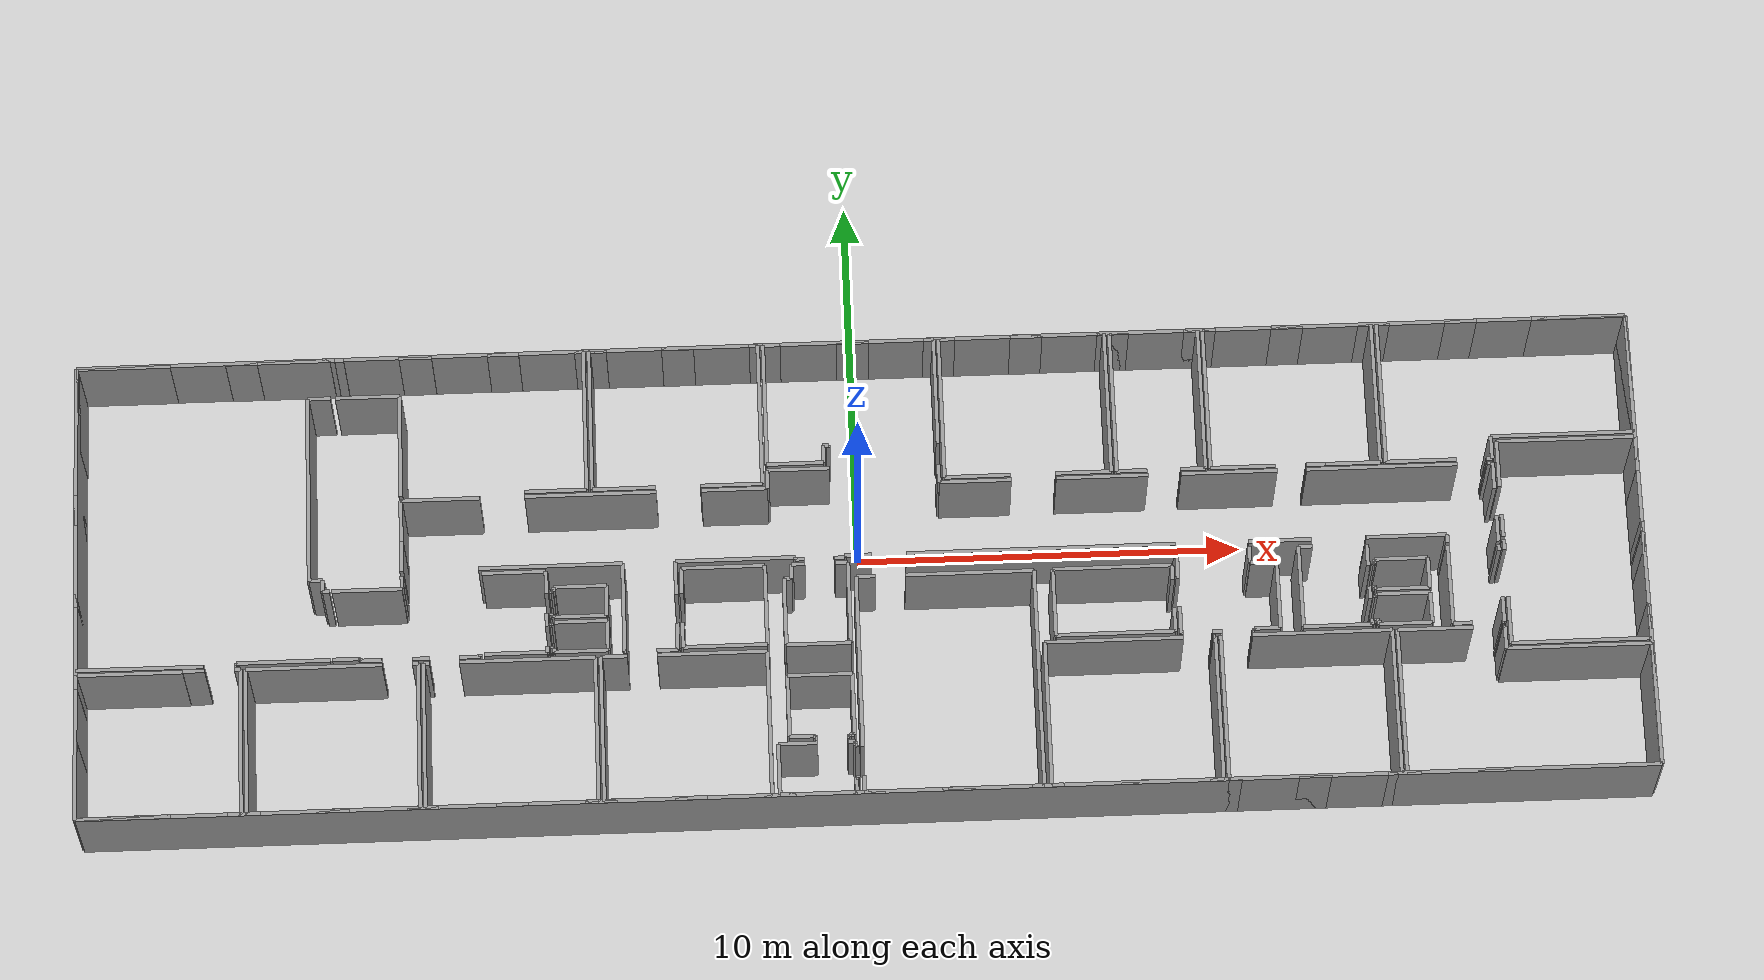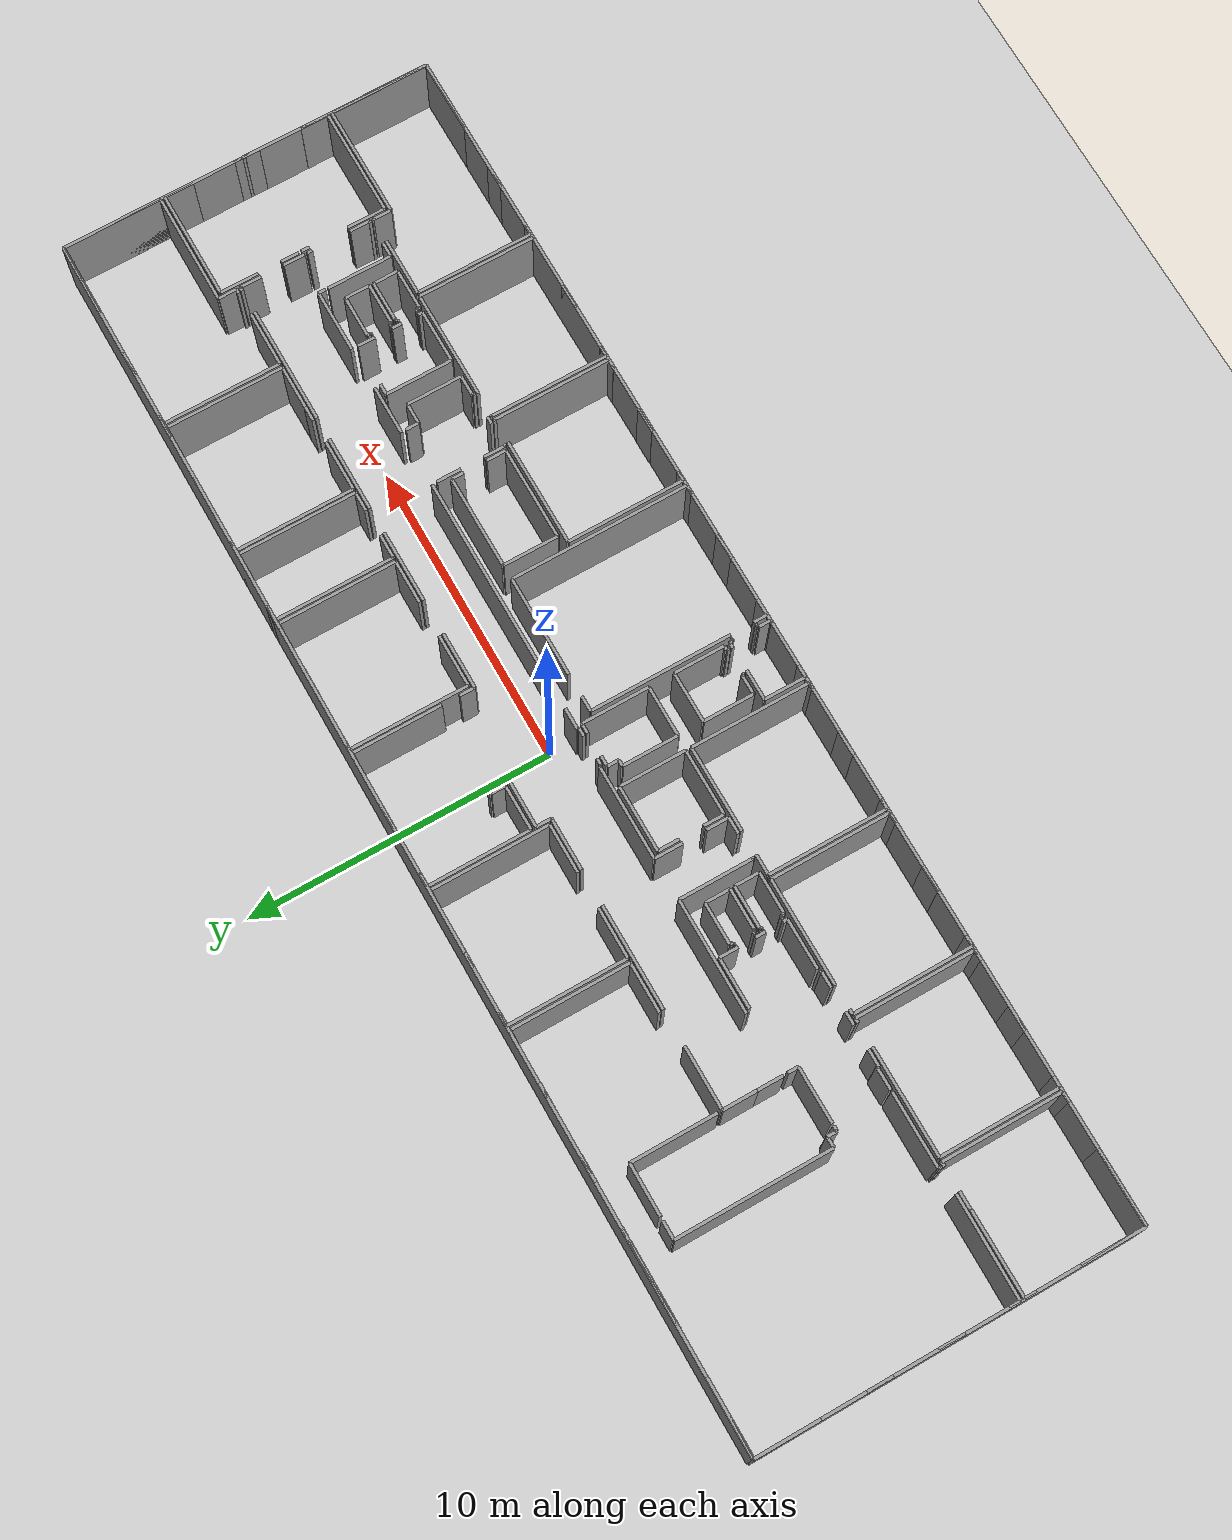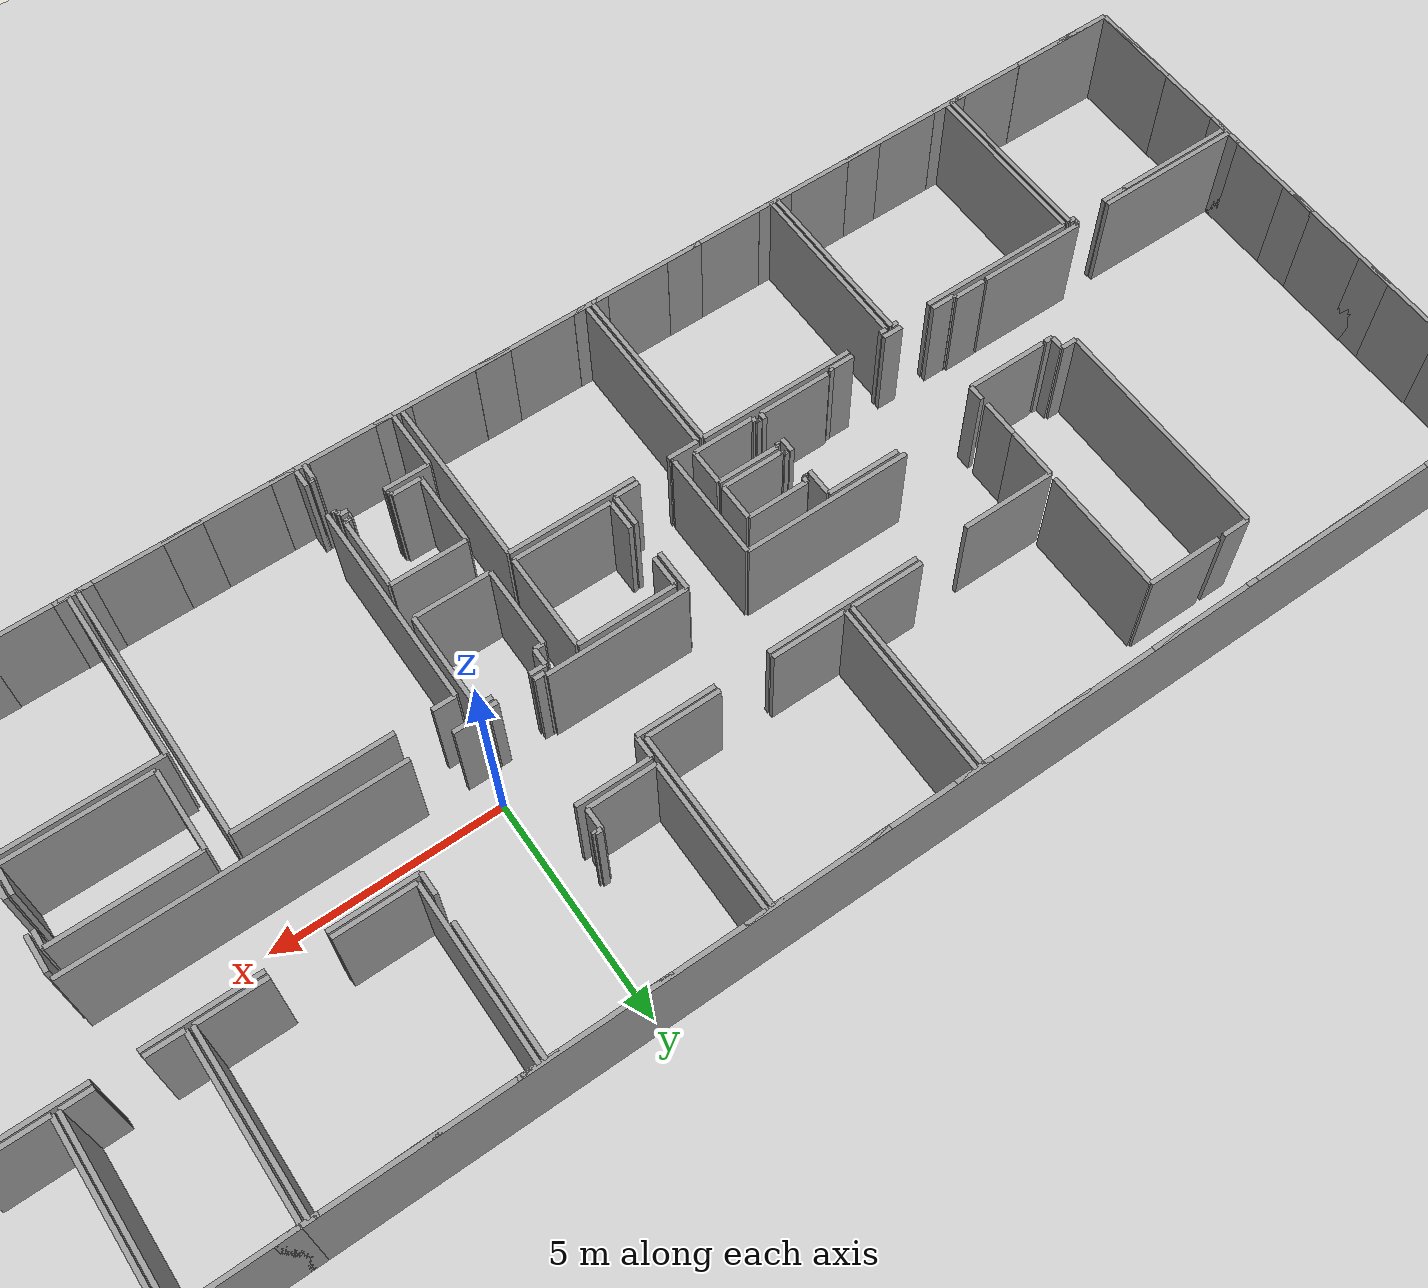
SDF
<sdf version="1.6">
  <world name="default">
    <light name="sun" type="directional">
      <cast_shadows>1</cast_shadows>
      <pose frame="">0 0 10 0 -0 0</pose>
      <diffuse>0.8 0.8 0.8 1</diffuse>
      <specular>0.1 0.1 0.1 1</specular>
      <attenuation>
        <range>1000</range>
        <constant>0.9</constant>
        <linear>0.01</linear>
        <quadratic>0.001</quadratic>
      </attenuation>
      <direction>-0.5 0.5 -1</direction>
    </light>
    <model name="ground_plane">
      <static>1</static>
      <link name="link">
        <collision name="collision">
          <geometry>
            <plane>
              <normal>0 0 1</normal>
              <size>100 100</size>
            </plane>
          </geometry>
          <surface>
            <friction>
              <ode>
                <mu>100</mu>
                <mu2>50</mu2>
              </ode>
              <torsional>
                <ode />
              </torsional>
            </friction>
            <contact>
              <ode />
            </contact>
            <bounce />
          </surface>
          <max_contacts>10</max_contacts>
        </collision>
        <visual name="visual">
          <cast_shadows>0</cast_shadows>
          <geometry>
            <plane>
              <normal>0 0 1</normal>
              <size>100 100</size>
            </plane>
          </geometry>
          <material>
            <script>
              <uri>file://media/materials/scripts/gazebo.material</uri>
              <name>Gazebo/Grey</name>
            </script>
          </material>
        </visual>
        <self_collide>0</self_collide>
        <kinematic>0</kinematic>
        <gravity>1</gravity>
      </link>
    </model>
    <gravity>0 0 -9.8</gravity>
    <magnetic_field>6e-06 2.3e-05 -4.2e-05</magnetic_field>
    <atmosphere type="adiabatic" />
    <physics default="0" name="default_physics" type="ode">
      <max_step_size>0.001</max_step_size>
      <real_time_factor>1</real_time_factor>
      <real_time_update_rate>1000</real_time_update_rate>
    </physics>
    <scene>
      <ambient>0.4 0.4 0.4 1</ambient>
      <background>0.7 0.7 0.7 1</background>
      <shadows>1</shadows>
    </scene>
    <spherical_coordinates>
      <surface_model>EARTH_WGS84</surface_model>
      <latitude_deg>0</latitude_deg>
      <longitude_deg>0</longitude_deg>
      <elevation>0</elevation>
      <heading_deg>0</heading_deg>
    </spherical_coordinates>
  <model name="0510025537_Layout1_PLAN2">
		<static>1</static>
		<link name="Wall_0">
			<collision name="Wall_0_Collision">
				<geometry>
					<box>
						<size>2.0953167694 0.1 2.5</size>
					</box>
				</geometry>
				<pose frame="">1.0476583847 0 1.25 0 0 0</pose>
			</collision>
			<visual name="Wall_0_Visual">
				<pose frame="">1.0476583847 0 1.25 0 0 0</pose>
				<geometry>
					<box>
						<size>2.0953167694 0.1 2.5</size>
					</box>
				</geometry>
				<material>
					<script>
						<uri>file://media/materials/scripts/gazebo.material</uri>
						<name>Gazebo/Grey</name>
					</script>
					<ambient>1 1 1 1</ambient>
				</material>
			</visual>
			<pose frame="">0.00184279087501 -12.3735464193 0 0 0 1.57079632679</pose>
		</link>
		<link name="Wall_1">
			<collision name="Wall_1_Collision">
				<geometry>
					<box>
						<size>0.37783567389 0.1 2.5</size>
					</box>
				</geometry>
				<pose frame="">0.188917836945 0 1.25 0 0 0</pose>
			</collision>
			<visual name="Wall_1_Visual">
				<pose frame="">0.188917836945 0 1.25 0 0 0</pose>
				<geometry>
					<box>
						<size>0.37783567389 0.1 2.5</size>
					</box>
				</geometry>
				<material>
					<script>
						<uri>file://media/materials/scripts/gazebo.material</uri>
						<name>Gazebo/Grey</name>
					</script>
					<ambient>1 1 1 1</ambient>
				</material>
			</visual>
			<pose frame="">0.00184279087501 -8.86036093283 0 0 0 1.57079632679</pose>
		</link>
		<link name="Wall_2">
			<collision name="Wall_2_Collision">
				<geometry>
					<box>
						<size>2.75509944716 0.1 2.5</size>
					</box>
				</geometry>
				<pose frame="">1.37754972358 0 1.25 0 0 0</pose>
			</collision>
			<visual name="Wall_2_Visual">
				<pose frame="">1.37754972358 0 1.25 0 0 0</pose>
				<geometry>
					<box>
						<size>2.75509944716 0.1 2.5</size>
					</box>
				</geometry>
				<material>
					<script>
						<uri>file://media/materials/scripts/gazebo.material</uri>
						<name>Gazebo/Grey</name>
					</script>
					<ambient>1 1 1 1</ambient>
				</material>
			</visual>
			<pose frame="">0.00184279087501 -8.48252525894 0 0 0 0.0</pose>
		</link>
		<link name="Wall_3">
			<collision name="Wall_3_Collision">
				<geometry>
					<box>
						<size>0.0133443477156 0.1 2.5</size>
					</box>
				</geometry>
				<pose frame="">0.00667217385779 0 1.25 0 0 0</pose>
			</collision>
			<visual name="Wall_3_Visual">
				<pose frame="">0.00667217385779 0 1.25 0 0 0</pose>
				<geometry>
					<box>
						<size>0.0133443477156 0.1 2.5</size>
					</box>
				</geometry>
				<material>
					<script>
						<uri>file://media/materials/scripts/gazebo.material</uri>
						<name>Gazebo/Grey</name>
					</script>
					<ambient>1 1 1 1</ambient>
				</material>
			</visual>
			<pose frame="">2.75694223804 -8.48252525894 0 0 0 1.57079632679</pose>
		</link>
		<link name="Wall_4">
			<collision name="Wall_4_Collision">
				<geometry>
					<box>
						<size>0.562368939442 0.1 2.5</size>
					</box>
				</geometry>
				<pose frame="">0.281184469721 0 1.25 0 0 0</pose>
			</collision>
			<visual name="Wall_4_Visual">
				<pose frame="">0.281184469721 0 1.25 0 0 0</pose>
				<geometry>
					<box>
						<size>0.562368939442 0.1 2.5</size>
					</box>
				</geometry>
				<material>
					<script>
						<uri>file://media/materials/scripts/gazebo.material</uri>
						<name>Gazebo/Grey</name>
					</script>
					<ambient>1 1 1 1</ambient>
				</material>
			</visual>
			<pose frame="">2.75694223804 -8.46918091123 0 0 0 0.0</pose>
		</link>
		<link name="Wall_5">
			<collision name="Wall_5_Collision">
				<geometry>
					<box>
						<size>0.150791129186 0.1 2.5</size>
					</box>
				</geometry>
				<pose frame="">0.075395564593 0 1.25 0 0 0</pose>
			</collision>
			<visual name="Wall_5_Visual">
				<pose frame="">0.075395564593 0 1.25 0 0 0</pose>
				<geometry>
					<box>
						<size>0.150791129186 0.1 2.5</size>
					</box>
				</geometry>
				<material>
					<script>
						<uri>file://media/materials/scripts/gazebo.material</uri>
						<name>Gazebo/Grey</name>
					</script>
					<ambient>1 1 1 1</ambient>
				</material>
			</visual>
			<pose frame="">4.08082862045 -8.46918091123 0 0 0 0.0</pose>
		</link>
		<link name="Wall_6">
			<collision name="Wall_6_Collision">
				<geometry>
					<box>
						<size>3.9007434708 0.1 2.5</size>
					</box>
				</geometry>
				<pose frame="">1.9503717354 0 1.25 0 0 0</pose>
			</collision>
			<visual name="Wall_6_Visual">
				<pose frame="">1.9503717354 0 1.25 0 0 0</pose>
				<geometry>
					<box>
						<size>3.9007434708 0.1 2.5</size>
					</box>
				</geometry>
				<material>
					<script>
						<uri>file://media/materials/scripts/gazebo.material</uri>
						<name>Gazebo/Grey</name>
					</script>
					<ambient>1 1 1 1</ambient>
				</material>
			</visual>
			<pose frame="">4.23161974963 -8.46918091123 0 0 0 -1.57079632679</pose>
		</link>
		<link name="Wall_7">
			<collision name="Wall_7_Collision">
				<geometry>
					<box>
						<size>0.335324394739 0.1 2.5</size>
					</box>
				</geometry>
				<pose frame="">0.167662197369 0 1.25 0 0 0</pose>
			</collision>
			<visual name="Wall_7_Visual">
				<pose frame="">0.167662197369 0 1.25 0 0 0</pose>
				<geometry>
					<box>
						<size>0.335324394739 0.1 2.5</size>
					</box>
				</geometry>
				<material>
					<script>
						<uri>file://media/materials/scripts/gazebo.material</uri>
						<name>Gazebo/Grey</name>
					</script>
					<ambient>1 1 1 1</ambient>
				</material>
			</visual>
			<pose frame="">4.23161974963 -12.369924382 0 0 0 3.14159265359</pose>
		</link>
		<link name="Wall_8">
			<collision name="Wall_8_Collision">
				<geometry>
					<box>
						<size>2.42187472982 0.1 2.5</size>
					</box>
				</geometry>
				<pose frame="">1.21093736491 0 1.25 0 0 0</pose>
			</collision>
			<visual name="Wall_8_Visual">
				<pose frame="">1.21093736491 0 1.25 0 0 0</pose>
				<geometry>
					<box>
						<size>2.42187472982 0.1 2.5</size>
					</box>
				</geometry>
				<material>
					<script>
						<uri>file://media/materials/scripts/gazebo.material</uri>
						<name>Gazebo/Grey</name>
					</script>
					<ambient>1 1 1 1</ambient>
				</material>
			</visual>
			<pose frame="">2.42371481223 -12.369924382 0 0 0 -3.14009710201</pose>
		</link>
		<link name="Wall_9">
			<collision name="Wall_9_Collision">
				<geometry>
					<box>
						<size>0.332337802631 0.1 2.5</size>
					</box>
				</geometry>
				<pose frame="">0.166168901315 0 1.25 0 0 0</pose>
			</collision>
			<visual name="Wall_9_Visual">
				<pose frame="">0.166168901315 0 1.25 0 0 0</pose>
				<geometry>
					<box>
						<size>0.332337802631 0.1 2.5</size>
					</box>
				</geometry>
				<material>
					<script>
						<uri>file://media/materials/scripts/gazebo.material</uri>
						<name>Gazebo/Grey</name>
					</script>
					<ambient>1 1 1 1</ambient>
				</material>
			</visual>
			<pose frame="">0.0 -8.34723899091 0 0 0 1.57079632679</pose>
		</link>
		<link name="Wall_10">
			<collision name="Wall_10_Collision">
				<geometry>
					<box>
						<size>0.832496663913 0.1 2.5</size>
					</box>
				</geometry>
				<pose frame="">0.416248331957 0 1.25 0 0 0</pose>
			</collision>
			<visual name="Wall_10_Visual">
				<pose frame="">0.416248331957 0 1.25 0 0 0</pose>
				<geometry>
					<box>
						<size>0.832496663913 0.1 2.5</size>
					</box>
				</geometry>
				<material>
					<script>
						<uri>file://media/materials/scripts/gazebo.material</uri>
						<name>Gazebo/Grey</name>
					</script>
					<ambient>1 1 1 1</ambient>
				</material>
			</visual>
			<pose frame="">0.0 -6.60815276101 0 0 0 1.57079632679</pose>
		</link>
		<link name="Wall_11">
			<collision name="Wall_11_Collision">
				<geometry>
					<box>
						<size>0.82658702421 0.1 2.5</size>
					</box>
				</geometry>
				<pose frame="">0.413293512105 0 1.25 0 0 0</pose>
			</collision>
			<visual name="Wall_11_Visual">
				<pose frame="">0.413293512105 0 1.25 0 0 0</pose>
				<geometry>
					<box>
						<size>0.82658702421 0.1 2.5</size>
					</box>
				</geometry>
				<material>
					<script>
						<uri>file://media/materials/scripts/gazebo.material</uri>
						<name>Gazebo/Grey</name>
					</script>
					<ambient>1 1 1 1</ambient>
				</material>
			</visual>
			<pose frame="">0.0 -4.35499142149 0 0 0 1.57079632679</pose>
		</link>
		<link name="Wall_12">
			<collision name="Wall_12_Collision">
				<geometry>
					<box>
						<size>2.08584863697 0.1 2.5</size>
					</box>
				</geometry>
				<pose frame="">1.04292431849 0 1.25 0 0 0</pose>
			</collision>
			<visual name="Wall_12_Visual">
				<pose frame="">1.04292431849 0 1.25 0 0 0</pose>
				<geometry>
					<box>
						<size>2.08584863697 0.1 2.5</size>
					</box>
				</geometry>
				<material>
					<script>
						<uri>file://media/materials/scripts/gazebo.material</uri>
						<name>Gazebo/Grey</name>
					</script>
					<ambient>1 1 1 1</ambient>
				</material>
			</visual>
			<pose frame="">0.0 -2.09510071805 0 0 0 1.57079632679</pose>
		</link>
		<link name="Wall_13">
			<collision name="Wall_13_Collision">
				<geometry>
					<box>
						<size>2.44697210396 0.1 2.5</size>
					</box>
				</geometry>
				<pose frame="">1.22348605198 0 1.25 0 0 0</pose>
			</collision>
			<visual name="Wall_13_Visual">
				<pose frame="">1.22348605198 0 1.25 0 0 0</pose>
				<geometry>
					<box>
						<size>2.44697210396 0.1 2.5</size>
					</box>
				</geometry>
				<material>
					<script>
						<uri>file://media/materials/scripts/gazebo.material</uri>
						<name>Gazebo/Grey</name>
					</script>
					<ambient>1 1 1 1</ambient>
				</material>
			</visual>
			<pose frame="">0.0 -0.0092520810828 0 0 0 0.0</pose>
		</link>
		<link name="Wall_14">
			<collision name="Wall_14_Collision">
				<geometry>
					<box>
						<size>0.828938171189 0.1 2.5</size>
					</box>
				</geometry>
				<pose frame="">0.414469085594 0 1.25 0 0 0</pose>
			</collision>
			<visual name="Wall_14_Visual">
				<pose frame="">0.414469085594 0 1.25 0 0 0</pose>
				<geometry>
					<box>
						<size>0.828938171189 0.1 2.5</size>
					</box>
				</geometry>
				<material>
					<script>
						<uri>file://media/materials/scripts/gazebo.material</uri>
						<name>Gazebo/Grey</name>
					</script>
					<ambient>1 1 1 1</ambient>
				</material>
			</visual>
			<pose frame="">3.88987735909 -0.0092520810828 0 0 0 0.0</pose>
		</link>
		<link name="Wall_15">
			<collision name="Wall_15_Collision">
				<geometry>
					<box>
						<size>1.89909131347 0.1 2.5</size>
					</box>
				</geometry>
				<pose frame="">0.949545656733 0 1.25 0 0 0</pose>
			</collision>
			<visual name="Wall_15_Visual">
				<pose frame="">0.949545656733 0 1.25 0 0 0</pose>
				<geometry>
					<box>
						<size>1.89909131347 0.1 2.5</size>
					</box>
				</geometry>
				<material>
					<script>
						<uri>file://media/materials/scripts/gazebo.material</uri>
						<name>Gazebo/Grey</name>
					</script>
					<ambient>1 1 1 1</ambient>
				</material>
			</visual>
			<pose frame="">4.71881553028 -0.0092520810828 0 0 0 0.0</pose>
		</link>
		<link name="Wall_16">
			<collision name="Wall_16_Collision">
				<geometry>
					<box>
						<size>0.601957170998 0.1 2.5</size>
					</box>
				</geometry>
				<pose frame="">0.300978585499 0 1.25 0 0 0</pose>
			</collision>
			<visual name="Wall_16_Visual">
				<pose frame="">0.300978585499 0 1.25 0 0 0</pose>
				<geometry>
					<box>
						<size>0.601957170998 0.1 2.5</size>
					</box>
				</geometry>
				<material>
					<script>
						<uri>file://media/materials/scripts/gazebo.material</uri>
						<name>Gazebo/Grey</name>
					</script>
					<ambient>1 1 1 1</ambient>
				</material>
			</visual>
			<pose frame="">6.61790684374 -1.06967655843 0 0 0 3.14159265359</pose>
		</link>
		<link name="Wall_17">
			<collision name="Wall_17_Collision">
				<geometry>
					<box>
						<size>5.04740420665 0.1 2.5</size>
					</box>
				</geometry>
				<pose frame="">2.52370210332 0 1.25 0 0 0</pose>
			</collision>
			<visual name="Wall_17_Visual">
				<pose frame="">2.52370210332 0 1.25 0 0 0</pose>
				<geometry>
					<box>
						<size>5.04740420665 0.1 2.5</size>
					</box>
				</geometry>
				<material>
					<script>
						<uri>file://media/materials/scripts/gazebo.material</uri>
						<name>Gazebo/Grey</name>
					</script>
					<ambient>1 1 1 1</ambient>
				</material>
			</visual>
			<pose frame="">6.01594967275 -1.06967655843 0 0 0 -1.57079632679</pose>
		</link>
		<link name="Wall_18">
			<collision name="Wall_18_Collision">
				<geometry>
					<box>
						<size>0.345872783885 0.1 2.5</size>
					</box>
				</geometry>
				<pose frame="">0.172936391943 0 1.25 0 0 0</pose>
			</collision>
			<visual name="Wall_18_Visual">
				<pose frame="">0.172936391943 0 1.25 0 0 0</pose>
				<geometry>
					<box>
						<size>0.345872783885 0.1 2.5</size>
					</box>
				</geometry>
				<material>
					<script>
						<uri>file://media/materials/scripts/gazebo.material</uri>
						<name>Gazebo/Grey</name>
					</script>
					<ambient>1 1 1 1</ambient>
				</material>
			</visual>
			<pose frame="">6.01594967275 -6.11708076508 0 0 0 0.0</pose>
		</link>
		<link name="Wall_19">
			<collision name="Wall_19_Collision">
				<geometry>
					<box>
						<size>0.308826332846 0.1 2.5</size>
					</box>
				</geometry>
				<pose frame="">0.154413166423 0 1.25 0 0 0</pose>
			</collision>
			<visual name="Wall_19_Visual">
				<pose frame="">0.154413166423 0 1.25 0 0 0</pose>
				<geometry>
					<box>
						<size>0.308826332846 0.1 2.5</size>
					</box>
				</geometry>
				<material>
					<script>
						<uri>file://media/materials/scripts/gazebo.material</uri>
						<name>Gazebo/Grey</name>
					</script>
					<ambient>1 1 1 1</ambient>
				</material>
			</visual>
			<pose frame="">6.36182245663 -6.11708076508 0 0 0 -1.57079632679</pose>
		</link>
		<link name="Wall_20">
			<collision name="Wall_20_Collision">
				<geometry>
					<box>
						<size>0.178051725234 0.1 2.5</size>
					</box>
				</geometry>
				<pose frame="">0.0890258626168 0 1.25 0 0 0</pose>
			</collision>
			<visual name="Wall_20_Visual">
				<pose frame="">0.0890258626168 0 1.25 0 0 0</pose>
				<geometry>
					<box>
						<size>0.178051725234 0.1 2.5</size>
					</box>
				</geometry>
				<material>
					<script>
						<uri>file://media/materials/scripts/gazebo.material</uri>
						<name>Gazebo/Grey</name>
					</script>
					<ambient>1 1 1 1</ambient>
				</material>
			</visual>
			<pose frame="">6.36182245663 -6.42590709792 0 0 0 0.0</pose>
		</link>
		<link name="Wall_21">
			<collision name="Wall_21_Collision">
				<geometry>
					<box>
						<size>2.39778865095 0.1 2.5</size>
					</box>
				</geometry>
				<pose frame="">1.19889432547 0 1.25 0 0 0</pose>
			</collision>
			<visual name="Wall_21_Visual">
				<pose frame="">1.19889432547 0 1.25 0 0 0</pose>
				<geometry>
					<box>
						<size>2.39778865095 0.1 2.5</size>
					</box>
				</geometry>
				<material>
					<script>
						<uri>file://media/materials/scripts/gazebo.material</uri>
						<name>Gazebo/Grey</name>
					</script>
					<ambient>1 1 1 1</ambient>
				</material>
			</visual>
			<pose frame="">6.53987418186 -8.30237656478 0 0 0 3.14159265359</pose>
		</link>
		<link name="Wall_22">
			<collision name="Wall_22_Collision">
				<geometry>
					<box>
						<size>0.0597318421554 0.1 2.5</size>
					</box>
				</geometry>
				<pose frame="">0.0298659210777 0 1.25 0 0 0</pose>
			</collision>
			<visual name="Wall_22_Visual">
				<pose frame="">0.0298659210777 0 1.25 0 0 0</pose>
				<geometry>
					<box>
						<size>0.0597318421554 0.1 2.5</size>
					</box>
				</geometry>
				<material>
					<script>
						<uri>file://media/materials/scripts/gazebo.material</uri>
						<name>Gazebo/Grey</name>
					</script>
					<ambient>1 1 1 1</ambient>
				</material>
			</visual>
			<pose frame="">4.14208553091 -8.30237656478 0 0 0 -1.57079632679</pose>
		</link>
		<link name="Wall_23">
			<collision name="Wall_23_Collision">
				<geometry>
					<box>
						<size>0.0581432293321 0.1 2.5</size>
					</box>
				</geometry>
				<pose frame="">0.0290716146661 0 1.25 0 0 0</pose>
			</collision>
			<visual name="Wall_23_Visual">
				<pose frame="">0.0290716146661 0 1.25 0 0 0</pose>
				<geometry>
					<box>
						<size>0.0581432293321 0.1 2.5</size>
					</box>
				</geometry>
				<material>
					<script>
						<uri>file://media/materials/scripts/gazebo.material</uri>
						<name>Gazebo/Grey</name>
					</script>
					<ambient>1 1 1 1</ambient>
				</material>
			</visual>
			<pose frame="">4.14208553091 -8.36210840694 0 0 0 3.14159265359</pose>
		</link>
		<link name="Wall_24">
			<collision name="Wall_24_Collision">
				<geometry>
					<box>
						<size>3.29913753122 0.1 2.5</size>
					</box>
				</geometry>
				<pose frame="">1.64956876561 0 1.25 0 0 0</pose>
			</collision>
			<visual name="Wall_24_Visual">
				<pose frame="">1.64956876561 0 1.25 0 0 0</pose>
				<geometry>
					<box>
						<size>3.29913753122 0.1 2.5</size>
					</box>
				</geometry>
				<material>
					<script>
						<uri>file://media/materials/scripts/gazebo.material</uri>
						<name>Gazebo/Grey</name>
					</script>
					<ambient>1 1 1 1</ambient>
				</material>
			</visual>
			<pose frame="">3.29910402237 -8.36210840694 0 0 0 3.13708557675</pose>
		</link>
		<link name="Wall_25">
			<collision name="Wall_25_Collision">
				<geometry>
					<box>
						<size>3.89686725551 0.1 2.5</size>
					</box>
				</geometry>
				<pose frame="">1.94843362776 0 1.25 0 0 0</pose>
			</collision>
			<visual name="Wall_25_Visual">
				<pose frame="">1.94843362776 0 1.25 0 0 0</pose>
				<geometry>
					<box>
						<size>3.89686725551 0.1 2.5</size>
					</box>
				</geometry>
				<material>
					<script>
						<uri>file://media/materials/scripts/gazebo.material</uri>
						<name>Gazebo/Grey</name>
					</script>
					<ambient>1 1 1 1</ambient>
				</material>
			</visual>
			<pose frame="">4.36671538413 -12.3752621211 0 0 0 1.57079632679</pose>
		</link>
		<link name="Wall_26">
			<collision name="Wall_26_Collision">
				<geometry>
					<box>
						<size>3.50651331258 0.1 2.5</size>
					</box>
				</geometry>
				<pose frame="">1.75325665629 0 1.25 0 0 0</pose>
			</collision>
			<visual name="Wall_26_Visual">
				<pose frame="">1.75325665629 0 1.25 0 0 0</pose>
				<geometry>
					<box>
						<size>3.50651331258 0.1 2.5</size>
					</box>
				</geometry>
				<material>
					<script>
						<uri>file://media/materials/scripts/gazebo.material</uri>
						<name>Gazebo/Grey</name>
					</script>
					<ambient>1 1 1 1</ambient>
				</material>
			</visual>
			<pose frame="">4.36671538413 -8.4783948656 0 0 0 0.0</pose>
		</link>
		<link name="Wall_27">
			<collision name="Wall_27_Collision">
				<geometry>
					<box>
						<size>0.146152379742 0.1 2.5</size>
					</box>
				</geometry>
				<pose frame="">0.073076189871 0 1.25 0 0 0</pose>
			</collision>
			<visual name="Wall_27_Visual">
				<pose frame="">0.073076189871 0 1.25 0 0 0</pose>
				<geometry>
					<box>
						<size>0.146152379742 0.1 2.5</size>
					</box>
				</geometry>
				<material>
					<script>
						<uri>file://media/materials/scripts/gazebo.material</uri>
						<name>Gazebo/Grey</name>
					</script>
					<ambient>1 1 1 1</ambient>
				</material>
			</visual>
			<pose frame="">8.64459553918 -8.4783948656 0 0 0 0.0</pose>
		</link>
		<link name="Wall_28">
			<collision name="Wall_28_Collision">
				<geometry>
					<box>
						<size>3.89413484146 0.1 2.5</size>
					</box>
				</geometry>
				<pose frame="">1.94706742073 0 1.25 0 0 0</pose>
			</collision>
			<visual name="Wall_28_Visual">
				<pose frame="">1.94706742073 0 1.25 0 0 0</pose>
				<geometry>
					<box>
						<size>3.89413484146 0.1 2.5</size>
					</box>
				</geometry>
				<material>
					<script>
						<uri>file://media/materials/scripts/gazebo.material</uri>
						<name>Gazebo/Grey</name>
					</script>
					<ambient>1 1 1 1</ambient>
				</material>
			</visual>
			<pose frame="">8.79074791892 -8.4783948656 0 0 0 -1.57079632679</pose>
		</link>
		<link name="Wall_29">
			<collision name="Wall_29_Collision">
				<geometry>
					<box>
						<size>0.338755798437 0.1 2.5</size>
					</box>
				</geometry>
				<pose frame="">0.169377899218 0 1.25 0 0 0</pose>
			</collision>
			<visual name="Wall_29_Visual">
				<pose frame="">0.169377899218 0 1.25 0 0 0</pose>
				<geometry>
					<box>
						<size>0.338755798437 0.1 2.5</size>
					</box>
				</geometry>
				<material>
					<script>
						<uri>file://media/materials/scripts/gazebo.material</uri>
						<name>Gazebo/Grey</name>
					</script>
					<ambient>1 1 1 1</ambient>
				</material>
			</visual>
			<pose frame="">8.79074791892 -12.3725297071 0 0 0 3.14159265359</pose>
		</link>
		<link name="Wall_30">
			<collision name="Wall_30_Collision">
				<geometry>
					<box>
						<size>0.831289318167 0.1 2.5</size>
					</box>
				</geometry>
				<pose frame="">0.415644659084 0 1.25 0 0 0</pose>
			</collision>
			<visual name="Wall_30_Visual">
				<pose frame="">0.415644659084 0 1.25 0 0 0</pose>
				<geometry>
					<box>
						<size>0.831289318167 0.1 2.5</size>
					</box>
				</geometry>
				<material>
					<script>
						<uri>file://media/materials/scripts/gazebo.material</uri>
						<name>Gazebo/Grey</name>
					</script>
					<ambient>1 1 1 1</ambient>
				</material>
			</visual>
			<pose frame="">6.99059541209 -12.3725297071 0 0 0 3.14159265359</pose>
		</link>
		<link name="Wall_31">
			<collision name="Wall_31_Collision">
				<geometry>
					<box>
						<size>0.347853395608 0.1 2.5</size>
					</box>
				</geometry>
				<pose frame="">0.173926697804 0 1.25 0 0 0</pose>
			</collision>
			<visual name="Wall_31_Visual">
				<pose frame="">0.173926697804 0 1.25 0 0 0</pose>
				<geometry>
					<box>
						<size>0.347853395608 0.1 2.5</size>
					</box>
				</geometry>
				<material>
					<script>
						<uri>file://media/materials/scripts/gazebo.material</uri>
						<name>Gazebo/Grey</name>
					</script>
					<ambient>1 1 1 1</ambient>
				</material>
			</visual>
			<pose frame="">4.71455804791 -12.3725297071 0 0 0 -3.13373749912</pose>
		</link>
		<link name="Wall_32">
			<collision name="Wall_32_Collision">
				<geometry>
					<box>
						<size>3.89813814577 0.1 2.5</size>
					</box>
				</geometry>
				<pose frame="">1.94906907289 0 1.25 0 0 0</pose>
			</collision>
			<visual name="Wall_32_Visual">
				<pose frame="">1.94906907289 0 1.25 0 0 0</pose>
				<geometry>
					<box>
						<size>3.89813814577 0.1 2.5</size>
					</box>
				</geometry>
				<material>
					<script>
						<uri>file://media/materials/scripts/gazebo.material</uri>
						<name>Gazebo/Grey</name>
					</script>
					<ambient>1 1 1 1</ambient>
				</material>
			</visual>
			<pose frame="">8.92323822838 -12.3739276863 0 0 0 1.57079632679</pose>
		</link>
		<link name="Wall_33">
			<collision name="Wall_33_Collision">
				<geometry>
					<box>
						<size>0.159814450022 0.1 2.5</size>
					</box>
				</geometry>
				<pose frame="">0.0799072250111 0 1.25 0 0 0</pose>
			</collision>
			<visual name="Wall_33_Visual">
				<pose frame="">0.0799072250111 0 1.25 0 0 0</pose>
				<geometry>
					<box>
						<size>0.159814450022 0.1 2.5</size>
					</box>
				</geometry>
				<material>
					<script>
						<uri>file://media/materials/scripts/gazebo.material</uri>
						<name>Gazebo/Grey</name>
					</script>
					<ambient>1 1 1 1</ambient>
				</material>
			</visual>
			<pose frame="">8.92323822838 -8.47578954057 0 0 0 0.0</pose>
		</link>
		<link name="Wall_34">
			<collision name="Wall_34_Collision">
				<geometry>
					<box>
						<size>3.48802185931 0.1 2.5</size>
					</box>
				</geometry>
				<pose frame="">1.74401092966 0 1.25 0 0 0</pose>
			</collision>
			<visual name="Wall_34_Visual">
				<pose frame="">1.74401092966 0 1.25 0 0 0</pose>
				<geometry>
					<box>
						<size>3.48802185931 0.1 2.5</size>
					</box>
				</geometry>
				<material>
					<script>
						<uri>file://media/materials/scripts/gazebo.material</uri>
						<name>Gazebo/Grey</name>
					</script>
					<ambient>1 1 1 1</ambient>
				</material>
			</visual>
			<pose frame="">9.85175065133 -8.47578954057 0 0 0 0.0</pose>
		</link>
		<link name="Wall_35">
			<collision name="Wall_35_Collision">
				<geometry>
					<box>
						<size>3.89750270064 0.1 2.5</size>
					</box>
				</geometry>
				<pose frame="">1.94875135032 0 1.25 0 0 0</pose>
			</collision>
			<visual name="Wall_35_Visual">
				<pose frame="">1.94875135032 0 1.25 0 0 0</pose>
				<geometry>
					<box>
						<size>3.89750270064 0.1 2.5</size>
					</box>
				</geometry>
				<material>
					<script>
						<uri>file://media/materials/scripts/gazebo.material</uri>
						<name>Gazebo/Grey</name>
					</script>
					<ambient>1 1 1 1</ambient>
				</material>
			</visual>
			<pose frame="">13.3397725106 -8.47578954057 0 0 0 -1.57079632679</pose>
		</link>
		<link name="Wall_36">
			<collision name="Wall_36_Collision">
				<geometry>
					<box>
						<size>0.350702166868 0.1 2.5</size>
					</box>
				</geometry>
				<pose frame="">0.175351083434 0 1.25 0 0 0</pose>
			</collision>
			<visual name="Wall_36_Visual">
				<pose frame="">0.175351083434 0 1.25 0 0 0</pose>
				<geometry>
					<box>
						<size>0.350702166868 0.1 2.5</size>
					</box>
				</geometry>
				<material>
					<script>
						<uri>file://media/materials/scripts/gazebo.material</uri>
						<name>Gazebo/Grey</name>
					</script>
					<ambient>1 1 1 1</ambient>
				</material>
			</visual>
			<pose frame="">13.3397725106 -12.3732922412 0 0 0 3.14159265359</pose>
		</link>
		<link name="Wall_37">
			<collision name="Wall_37_Collision">
				<geometry>
					<box>
						<size>0.827730825443 0.1 2.5</size>
					</box>
				</geometry>
				<pose frame="">0.413865412722 0 1.25 0 0 0</pose>
			</collision>
			<visual name="Wall_37_Visual">
				<pose frame="">0.413865412722 0 1.25 0 0 0</pose>
				<geometry>
					<box>
						<size>0.827730825443 0.1 2.5</size>
					</box>
				</geometry>
				<material>
					<script>
						<uri>file://media/materials/scripts/gazebo.material</uri>
						<name>Gazebo/Grey</name>
					</script>
					<ambient>1 1 1 1</ambient>
				</material>
			</visual>
			<pose frame="">11.5461015441 -12.3732922412 0 0 0 3.14159265359</pose>
		</link>
		<link name="Wall_38">
			<collision name="Wall_38_Collision">
				<geometry>
					<box>
						<size>0.341806525729 0.1 2.5</size>
					</box>
				</geometry>
				<pose frame="">0.170903262865 0 1.25 0 0 0</pose>
			</collision>
			<visual name="Wall_38_Visual">
				<pose frame="">0.170903262865 0 1.25 0 0 0</pose>
				<geometry>
					<box>
						<size>0.341806525729 0.1 2.5</size>
					</box>
				</geometry>
				<material>
					<script>
						<uri>file://media/materials/scripts/gazebo.material</uri>
						<name>Gazebo/Grey</name>
					</script>
					<ambient>1 1 1 1</ambient>
				</material>
			</visual>
			<pose frame="">9.26504416344 -12.3732922412 0 0 0 -3.13973357412</pose>
		</link>
		<link name="Wall_39">
			<collision name="Wall_39_Collision">
				<geometry>
					<box>
						<size>1.80618923556 0.1 2.5</size>
					</box>
				</geometry>
				<pose frame="">0.90309461778 0 1.25 0 0 0</pose>
			</collision>
			<visual name="Wall_39_Visual">
				<pose frame="">0.90309461778 0 1.25 0 0 0</pose>
				<geometry>
					<box>
						<size>1.80618923556 0.1 2.5</size>
					</box>
				</geometry>
				<material>
					<script>
						<uri>file://media/materials/scripts/gazebo.material</uri>
						<name>Gazebo/Grey</name>
					</script>
					<ambient>1 1 1 1</ambient>
				</material>
			</visual>
			<pose frame="">6.60214780454 -6.42317468387 0 0 0 0.0</pose>
		</link>
		<link name="Wall_40">
			<collision name="Wall_40_Collision">
				<geometry>
					<box>
						<size>0.347207218657 0.1 2.5</size>
					</box>
				</geometry>
				<pose frame="">0.173603609328 0 1.25 0 0 0</pose>
			</collision>
			<visual name="Wall_40_Visual">
				<pose frame="">0.173603609328 0 1.25 0 0 0</pose>
				<geometry>
					<box>
						<size>0.347207218657 0.1 2.5</size>
					</box>
				</geometry>
				<material>
					<script>
						<uri>file://media/materials/scripts/gazebo.material</uri>
						<name>Gazebo/Grey</name>
					</script>
					<ambient>1 1 1 1</ambient>
				</material>
			</visual>
			<pose frame="">8.4083370401 -6.42317468387 0 0 0 1.57079632679</pose>
		</link>
		<link name="Wall_41">
			<collision name="Wall_41_Collision">
				<geometry>
					<box>
						<size>0.0605579208235 0.1 2.5</size>
					</box>
				</geometry>
				<pose frame="">0.0302789604118 0 1.25 0 0 0</pose>
			</collision>
			<visual name="Wall_41_Visual">
				<pose frame="">0.0302789604118 0 1.25 0 0 0</pose>
				<geometry>
					<box>
						<size>0.0605579208235 0.1 2.5</size>
					</box>
				</geometry>
				<material>
					<script>
						<uri>file://media/materials/scripts/gazebo.material</uri>
						<name>Gazebo/Grey</name>
					</script>
					<ambient>1 1 1 1</ambient>
				</material>
			</visual>
			<pose frame="">10.3918154667 -8.28934993963 0 0 0 -1.57079632679</pose>
		</link>
		<link name="Wall_42">
			<collision name="Wall_42_Collision">
				<geometry>
					<box>
						<size>0.542543051408 0.1 2.5</size>
					</box>
				</geometry>
				<pose frame="">0.271271525704 0 1.25 0 0 0</pose>
			</collision>
			<visual name="Wall_42_Visual">
				<pose frame="">0.271271525704 0 1.25 0 0 0</pose>
				<geometry>
					<box>
						<size>0.542543051408 0.1 2.5</size>
					</box>
				</geometry>
				<material>
					<script>
						<uri>file://media/materials/scripts/gazebo.material</uri>
						<name>Gazebo/Grey</name>
					</script>
					<ambient>1 1 1 1</ambient>
				</material>
			</visual>
			<pose frame="">10.3918154667 -8.34990786046 0 0 0 3.14159265359</pose>
		</link>
		<link name="Wall_43">
			<collision name="Wall_43_Collision">
				<geometry>
					<box>
						<size>0.438711317278 0.1 2.5</size>
					</box>
				</geometry>
				<pose frame="">0.219355658639 0 1.25 0 0 0</pose>
			</collision>
			<visual name="Wall_43_Visual">
				<pose frame="">0.219355658639 0 1.25 0 0 0</pose>
				<geometry>
					<box>
						<size>0.438711317278 0.1 2.5</size>
					</box>
				</geometry>
				<material>
					<script>
						<uri>file://media/materials/scripts/gazebo.material</uri>
						<name>Gazebo/Grey</name>
					</script>
					<ambient>1 1 1 1</ambient>
				</material>
			</visual>
			<pose frame="">9.0805744424 -8.34990786046 0 0 0 3.14159265359</pose>
		</link>
		<link name="Wall_44">
			<collision name="Wall_44_Collision">
				<geometry>
					<box>
						<size>0.544258753257 0.1 2.5</size>
					</box>
				</geometry>
				<pose frame="">0.272129376628 0 1.25 0 0 0</pose>
			</collision>
			<visual name="Wall_44_Visual">
				<pose frame="">0.272129376628 0 1.25 0 0 0</pose>
				<geometry>
					<box>
						<size>0.544258753257 0.1 2.5</size>
					</box>
				</geometry>
				<material>
					<script>
						<uri>file://media/materials/scripts/gazebo.material</uri>
						<name>Gazebo/Grey</name>
					</script>
					<ambient>1 1 1 1</ambient>
				</material>
			</visual>
			<pose frame="">7.86649297833 -8.34990786046 0 0 0 3.14159265359</pose>
		</link>
		<link name="Wall_45">
			<collision name="Wall_45_Collision">
				<geometry>
					<box>
						<size>0.056427527483 0.1 2.5</size>
					</box>
				</geometry>
				<pose frame="">0.0282137637415 0 1.25 0 0 0</pose>
			</collision>
			<visual name="Wall_45_Visual">
				<pose frame="">0.0282137637415 0 1.25 0 0 0</pose>
				<geometry>
					<box>
						<size>0.056427527483 0.1 2.5</size>
					</box>
				</geometry>
				<material>
					<script>
						<uri>file://media/materials/scripts/gazebo.material</uri>
						<name>Gazebo/Grey</name>
					</script>
					<ambient>1 1 1 1</ambient>
				</material>
			</visual>
			<pose frame="">7.32223422507 -8.34990786046 0 0 0 1.57079632679</pose>
		</link>
		<link name="Wall_46">
			<collision name="Wall_46_Collision">
				<geometry>
					<box>
						<size>0.720094296268 0.1 2.5</size>
					</box>
				</geometry>
				<pose frame="">0.360047148134 0 1.25 0 0 0</pose>
			</collision>
			<visual name="Wall_46_Visual">
				<pose frame="">0.360047148134 0 1.25 0 0 0</pose>
				<geometry>
					<box>
						<size>0.720094296268 0.1 2.5</size>
					</box>
				</geometry>
				<material>
					<script>
						<uri>file://media/materials/scripts/gazebo.material</uri>
						<name>Gazebo/Grey</name>
					</script>
					<ambient>1 1 1 1</ambient>
				</material>
			</visual>
			<pose frame="">7.32223422507 -8.29348033297 0 0 0 -3.13691566687</pose>
		</link>
		<link name="Wall_47">
			<collision name="Wall_47_Collision">
				<geometry>
					<box>
						<size>1.36131410053 0.1 2.5</size>
					</box>
				</geometry>
				<pose frame="">0.680657050264 0 1.25 0 0 0</pose>
			</collision>
			<visual name="Wall_47_Visual">
				<pose frame="">0.680657050264 0 1.25 0 0 0</pose>
				<geometry>
					<box>
						<size>1.36131410053 0.1 2.5</size>
					</box>
				</geometry>
				<material>
					<script>
						<uri>file://media/materials/scripts/gazebo.material</uri>
						<name>Gazebo/Grey</name>
					</script>
					<ambient>1 1 1 1</ambient>
				</material>
			</visual>
			<pose frame="">12.3027896041 -6.52281248014 0 0 0 0.0</pose>
		</link>
		<link name="Wall_48">
			<collision name="Wall_48_Collision">
				<geometry>
					<box>
						<size>0.816483446654 0.1 2.5</size>
					</box>
				</geometry>
				<pose frame="">0.408241723327 0 1.25 0 0 0</pose>
			</collision>
			<visual name="Wall_48_Visual">
				<pose frame="">0.408241723327 0 1.25 0 0 0</pose>
				<geometry>
					<box>
						<size>0.816483446654 0.1 2.5</size>
					</box>
				</geometry>
				<material>
					<script>
						<uri>file://media/materials/scripts/gazebo.material</uri>
						<name>Gazebo/Grey</name>
					</script>
					<ambient>1 1 1 1</ambient>
				</material>
			</visual>
			<pose frame="">13.6641037046 -6.52281248014 0 0 0 -1.57079632679</pose>
		</link>
		<link name="Wall_49">
			<collision name="Wall_49_Collision">
				<geometry>
					<box>
						<size>1.35934422063 0.1 2.5</size>
					</box>
				</geometry>
				<pose frame="">0.679672110313 0 1.25 0 0 0</pose>
			</collision>
			<visual name="Wall_49_Visual">
				<pose frame="">0.679672110313 0 1.25 0 0 0</pose>
				<geometry>
					<box>
						<size>1.35934422063 0.1 2.5</size>
					</box>
				</geometry>
				<material>
					<script>
						<uri>file://media/materials/scripts/gazebo.material</uri>
						<name>Gazebo/Grey</name>
					</script>
					<ambient>1 1 1 1</ambient>
				</material>
			</visual>
			<pose frame="">13.6641037046 -7.3392959268 0 0 0 3.14159265359</pose>
		</link>
		<link name="Wall_50">
			<collision name="Wall_50_Collision">
				<geometry>
					<box>
						<size>0.0365380949355 0.1 2.5</size>
					</box>
				</geometry>
				<pose frame="">0.0182690474678 0 1.25 0 0 0</pose>
			</collision>
			<visual name="Wall_50_Visual">
				<pose frame="">0.0182690474678 0 1.25 0 0 0</pose>
				<geometry>
					<box>
						<size>0.0365380949355 0.1 2.5</size>
					</box>
				</geometry>
				<material>
					<script>
						<uri>file://media/materials/scripts/gazebo.material</uri>
						<name>Gazebo/Grey</name>
					</script>
					<ambient>1 1 1 1</ambient>
				</material>
			</visual>
			<pose frame="">12.304759484 -7.3392959268 0 0 0 1.57079632679</pose>
		</link>
		<link name="Wall_51">
			<collision name="Wall_51_Collision">
				<geometry>
					<box>
						<size>0.0599860202072 0.1 2.5</size>
					</box>
				</geometry>
				<pose frame="">0.0299930101036 0 1.25 0 0 0</pose>
			</collision>
			<visual name="Wall_51_Visual">
				<pose frame="">0.0299930101036 0 1.25 0 0 0</pose>
				<geometry>
					<box>
						<size>0.0599860202072 0.1 2.5</size>
					</box>
				</geometry>
				<material>
					<script>
						<uri>file://media/materials/scripts/gazebo.material</uri>
						<name>Gazebo/Grey</name>
					</script>
					<ambient>1 1 1 1</ambient>
				</material>
			</visual>
			<pose frame="">12.304759484 -7.30275783186 0 0 0 3.14159265359</pose>
		</link>
		<link name="Wall_52">
			<collision name="Wall_52_Collision">
				<geometry>
					<box>
						<size>0.0592870305649 0.1 2.5</size>
					</box>
				</geometry>
				<pose frame="">0.0296435152825 0 1.25 0 0 0</pose>
			</collision>
			<visual name="Wall_52_Visual">
				<pose frame="">0.0296435152825 0 1.25 0 0 0</pose>
				<geometry>
					<box>
						<size>0.0592870305649 0.1 2.5</size>
					</box>
				</geometry>
				<material>
					<script>
						<uri>file://media/materials/scripts/gazebo.material</uri>
						<name>Gazebo/Grey</name>
					</script>
					<ambient>1 1 1 1</ambient>
				</material>
			</visual>
			<pose frame="">12.2447734638 -7.30275783186 0 0 0 1.57079632679</pose>
		</link>
		<link name="Wall_53">
			<collision name="Wall_53_Collision">
				<geometry>
					<box>
						<size>0.0461333163881 0.1 2.5</size>
					</box>
				</geometry>
				<pose frame="">0.0230666581941 0 1.25 0 0 0</pose>
			</collision>
			<visual name="Wall_53_Visual">
				<pose frame="">0.0230666581941 0 1.25 0 0 0</pose>
				<geometry>
					<box>
						<size>0.0461333163881 0.1 2.5</size>
					</box>
				</geometry>
				<material>
					<script>
						<uri>file://media/materials/scripts/gazebo.material</uri>
						<name>Gazebo/Grey</name>
					</script>
					<ambient>1 1 1 1</ambient>
				</material>
			</visual>
			<pose frame="">12.2447734638 -6.67735273559 0 0 0 1.57079632679</pose>
		</link>
		<link name="Wall_54">
			<collision name="Wall_54_Collision">
				<geometry>
					<box>
						<size>0.0575713287158 0.1 2.5</size>
					</box>
				</geometry>
				<pose frame="">0.0287856643579 0 1.25 0 0 0</pose>
			</collision>
			<visual name="Wall_54_Visual">
				<pose frame="">0.0287856643579 0 1.25 0 0 0</pose>
				<geometry>
					<box>
						<size>0.0575713287158 0.1 2.5</size>
					</box>
				</geometry>
				<material>
					<script>
						<uri>file://media/materials/scripts/gazebo.material</uri>
						<name>Gazebo/Grey</name>
					</script>
					<ambient>1 1 1 1</ambient>
				</material>
			</visual>
			<pose frame="">12.2447734638 -6.6312194192 0 0 0 0.0</pose>
		</link>
		<link name="Wall_55">
			<collision name="Wall_55_Collision">
				<geometry>
					<box>
						<size>0.108407851625 0.1 2.5</size>
					</box>
				</geometry>
				<pose frame="">0.0542039258124 0 1.25 0 0 0</pose>
			</collision>
			<visual name="Wall_55_Visual">
				<pose frame="">0.0542039258124 0 1.25 0 0 0</pose>
				<geometry>
					<box>
						<size>0.108407851625 0.1 2.5</size>
					</box>
				</geometry>
				<material>
					<script>
						<uri>file://media/materials/scripts/gazebo.material</uri>
						<name>Gazebo/Grey</name>
					</script>
					<ambient>1 1 1 1</ambient>
				</material>
			</visual>
			<pose frame="">12.3023447925 -6.6312194192 0 0 0 1.56669318452</pose>
		</link>
		<link name="Wall_56">
			<collision name="Wall_56_Collision">
				<geometry>
					<box>
						<size>1.37014678782 0.1 2.5</size>
					</box>
				</geometry>
				<pose frame="">0.685073393912 0 1.25 0 0 0</pose>
			</collision>
			<visual name="Wall_56_Visual">
				<pose frame="">0.685073393912 0 1.25 0 0 0</pose>
				<geometry>
					<box>
						<size>1.37014678782 0.1 2.5</size>
					</box>
				</geometry>
				<material>
					<script>
						<uri>file://media/materials/scripts/gazebo.material</uri>
						<name>Gazebo/Grey</name>
					</script>
					<ambient>1 1 1 1</ambient>
				</material>
			</visual>
			<pose frame="">12.3019635254 -7.48246171443 0 0 0 0.0</pose>
		</link>
		<link name="Wall_57">
			<collision name="Wall_57_Collision">
				<geometry>
					<box>
						<size>0.8103196289 0.1 2.5</size>
					</box>
				</geometry>
				<pose frame="">0.40515981445 0 1.25 0 0 0</pose>
			</collision>
			<visual name="Wall_57_Visual">
				<pose frame="">0.40515981445 0 1.25 0 0 0</pose>
				<geometry>
					<box>
						<size>0.8103196289 0.1 2.5</size>
					</box>
				</geometry>
				<material>
					<script>
						<uri>file://media/materials/scripts/gazebo.material</uri>
						<name>Gazebo/Grey</name>
					</script>
					<ambient>1 1 1 1</ambient>
				</material>
			</visual>
			<pose frame="">13.6721103133 -7.48246171443 0 0 0 -1.57079632679</pose>
		</link>
		<link name="Wall_58">
			<collision name="Wall_58_Collision">
				<geometry>
					<box>
						<size>1.36538094936 0.1 2.5</size>
					</box>
				</geometry>
				<pose frame="">0.682690474678 0 1.25 0 0 0</pose>
			</collision>
			<visual name="Wall_58_Visual">
				<pose frame="">0.682690474678 0 1.25 0 0 0</pose>
				<geometry>
					<box>
						<size>1.36538094936 0.1 2.5</size>
					</box>
				</geometry>
				<material>
					<script>
						<uri>file://media/materials/scripts/gazebo.material</uri>
						<name>Gazebo/Grey</name>
					</script>
					<ambient>1 1 1 1</ambient>
				</material>
			</visual>
			<pose frame="">13.6721103133 -8.29278134333 0 0 0 3.14159265359</pose>
		</link>
		<link name="Wall_59">
			<collision name="Wall_59_Collision">
				<geometry>
					<box>
						<size>0.0972231047849 0.1 2.5</size>
					</box>
				</geometry>
				<pose frame="">0.0486115523925 0 1.25 0 0 0</pose>
			</collision>
			<visual name="Wall_59_Visual">
				<pose frame="">0.0486115523925 0 1.25 0 0 0</pose>
				<geometry>
					<box>
						<size>0.0972231047849 0.1 2.5</size>
					</box>
				</geometry>
				<material>
					<script>
						<uri>file://media/materials/scripts/gazebo.material</uri>
						<name>Gazebo/Grey</name>
					</script>
					<ambient>1 1 1 1</ambient>
				</material>
			</visual>
			<pose frame="">12.3067293639 -8.29278134333 0 0 0 1.57079632679</pose>
		</link>
		<link name="Wall_60">
			<collision name="Wall_60_Collision">
				<geometry>
					<box>
						<size>0.0660227489356 0.1 2.5</size>
					</box>
				</geometry>
				<pose frame="">0.0330113744678 0 1.25 0 0 0</pose>
			</collision>
			<visual name="Wall_60_Visual">
				<pose frame="">0.0330113744678 0 1.25 0 0 0</pose>
				<geometry>
					<box>
						<size>0.0660227489356 0.1 2.5</size>
					</box>
				</geometry>
				<material>
					<script>
						<uri>file://media/materials/scripts/gazebo.material</uri>
						<name>Gazebo/Grey</name>
					</script>
					<ambient>1 1 1 1</ambient>
				</material>
			</visual>
			<pose frame="">12.3067293639 -8.19555823855 0 0 0 3.14159265359</pose>
		</link>
		<link name="Wall_61">
			<collision name="Wall_61_Collision">
				<geometry>
					<box>
						<size>0.0533773908623 0.1 2.5</size>
					</box>
				</geometry>
				<pose frame="">0.0266886954312 0 1.25 0 0 0</pose>
			</collision>
			<visual name="Wall_61_Visual">
				<pose frame="">0.0266886954312 0 1.25 0 0 0</pose>
				<geometry>
					<box>
						<size>0.0533773908623 0.1 2.5</size>
					</box>
				</geometry>
				<material>
					<script>
						<uri>file://media/materials/scripts/gazebo.material</uri>
						<name>Gazebo/Grey</name>
					</script>
					<ambient>1 1 1 1</ambient>
				</material>
			</visual>
			<pose frame="">12.240706615 -8.19555823855 0 0 0 1.57079632679</pose>
		</link>
		<link name="Wall_62">
			<collision name="Wall_62_Collision">
				<geometry>
					<box>
						<size>0.0484844633666 0.1 2.5</size>
					</box>
				</geometry>
				<pose frame="">0.0242422316833 0 1.25 0 0 0</pose>
			</collision>
			<visual name="Wall_62_Visual">
				<pose frame="">0.0242422316833 0 1.25 0 0 0</pose>
				<geometry>
					<box>
						<size>0.0484844633666 0.1 2.5</size>
					</box>
				</geometry>
				<material>
					<script>
						<uri>file://media/materials/scripts/gazebo.material</uri>
						<name>Gazebo/Grey</name>
					</script>
					<ambient>1 1 1 1</ambient>
				</material>
			</visual>
			<pose frame="">12.240706615 -7.57104276546 0 0 0 1.57079632679</pose>
		</link>
		<link name="Wall_63">
			<collision name="Wall_63_Collision">
				<geometry>
					<box>
						<size>0.0575713287158 0.1 2.5</size>
					</box>
				</geometry>
				<pose frame="">0.0287856643579 0 1.25 0 0 0</pose>
			</collision>
			<visual name="Wall_63_Visual">
				<pose frame="">0.0287856643579 0 1.25 0 0 0</pose>
				<geometry>
					<box>
						<size>0.0575713287158 0.1 2.5</size>
					</box>
				</geometry>
				<material>
					<script>
						<uri>file://media/materials/scripts/gazebo.material</uri>
						<name>Gazebo/Grey</name>
					</script>
					<ambient>1 1 1 1</ambient>
				</material>
			</visual>
			<pose frame="">12.240706615 -7.52255830209 0 0 0 0.0</pose>
		</link>
		<link name="Wall_64">
			<collision name="Wall_64_Collision">
				<geometry>
					<box>
						<size>0.0402656162847 0.1 2.5</size>
					</box>
				</geometry>
				<pose frame="">0.0201328081423 0 1.25 0 0 0</pose>
			</collision>
			<visual name="Wall_64_Visual">
				<pose frame="">0.0201328081423 0 1.25 0 0 0</pose>
				<geometry>
					<box>
						<size>0.0402656162847 0.1 2.5</size>
					</box>
				</geometry>
				<material>
					<script>
						<uri>file://media/materials/scripts/gazebo.material</uri>
						<name>Gazebo/Grey</name>
					</script>
					<ambient>1 1 1 1</ambient>
				</material>
			</visual>
			<pose frame="">12.2982779437 -7.52255830209 0 0 0 1.47913629705</pose>
		</link>
		<link name="Wall_65">
			<collision name="Wall_65_Collision">
				<geometry>
					<box>
						<size>1.64732795323 0.1 2.5</size>
					</box>
				</geometry>
				<pose frame="">0.823663976616 0 1.25 0 0 0</pose>
			</collision>
			<visual name="Wall_65_Visual">
				<pose frame="">0.823663976616 0 1.25 0 0 0</pose>
				<geometry>
					<box>
						<size>1.64732795323 0.1 2.5</size>
					</box>
				</geometry>
				<material>
					<script>
						<uri>file://media/materials/scripts/gazebo.material</uri>
						<name>Gazebo/Grey</name>
					</script>
					<ambient>1 1 1 1</ambient>
				</material>
			</visual>
			<pose frame="">10.4731524433 -6.07666645485 0 0 0 0.0</pose>
		</link>
		<link name="Wall_66">
			<collision name="Wall_66_Collision">
				<geometry>
					<box>
						<size>0.606913643007 0.1 2.5</size>
					</box>
				</geometry>
				<pose frame="">0.303456821503 0 1.25 0 0 0</pose>
			</collision>
			<visual name="Wall_66_Visual">
				<pose frame="">0.303456821503 0 1.25 0 0 0</pose>
				<geometry>
					<box>
						<size>0.606913643007 0.1 2.5</size>
					</box>
				</geometry>
				<material>
					<script>
						<uri>file://media/materials/scripts/gazebo.material</uri>
						<name>Gazebo/Grey</name>
					</script>
					<ambient>1 1 1 1</ambient>
				</material>
			</visual>
			<pose frame="">12.1204803965 -6.07666645485 0 0 0 -1.57079632679</pose>
		</link>
		<link name="Wall_67">
			<collision name="Wall_67_Collision">
				<geometry>
					<box>
						<size>0.332337802631 0.1 2.5</size>
					</box>
				</geometry>
				<pose frame="">0.166168901315 0 1.25 0 0 0</pose>
			</collision>
			<visual name="Wall_67_Visual">
				<pose frame="">0.166168901315 0 1.25 0 0 0</pose>
				<geometry>
					<box>
						<size>0.332337802631 0.1 2.5</size>
					</box>
				</geometry>
				<material>
					<script>
						<uri>file://media/materials/scripts/gazebo.material</uri>
						<name>Gazebo/Grey</name>
					</script>
					<ambient>1 1 1 1</ambient>
				</material>
			</visual>
			<pose frame="">12.1204803965 -7.24493232509 0 0 0 -1.57079632679</pose>
		</link>
		<link name="Wall_68">
			<collision name="Wall_68_Collision">
				<geometry>
					<box>
						<size>0.147486814514 0.1 2.5</size>
					</box>
				</geometry>
				<pose frame="">0.0737434072568 0 1.25 0 0 0</pose>
			</collision>
			<visual name="Wall_68_Visual">
				<pose frame="">0.0737434072568 0 1.25 0 0 0</pose>
				<geometry>
					<box>
						<size>0.147486814514 0.1 2.5</size>
					</box>
				</geometry>
				<material>
					<script>
						<uri>file://media/materials/scripts/gazebo.material</uri>
						<name>Gazebo/Grey</name>
					</script>
					<ambient>1 1 1 1</ambient>
				</material>
			</visual>
			<pose frame="">12.1204803965 -8.14389654953 0 0 0 -1.57079632679</pose>
		</link>
		<link name="Wall_69">
			<collision name="Wall_69_Collision">
				<geometry>
					<box>
						<size>1.62642180848 0.1 2.5</size>
					</box>
				</geometry>
				<pose frame="">0.813210904238 0 1.25 0 0 0</pose>
			</collision>
			<visual name="Wall_69_Visual">
				<pose frame="">0.813210904238 0 1.25 0 0 0</pose>
				<geometry>
					<box>
						<size>1.62642180848 0.1 2.5</size>
					</box>
				</geometry>
				<material>
					<script>
						<uri>file://media/materials/scripts/gazebo.material</uri>
						<name>Gazebo/Grey</name>
					</script>
					<ambient>1 1 1 1</ambient>
				</material>
			</visual>
			<pose frame="">12.1204803965 -8.29138336405 0 0 0 3.14159265359</pose>
		</link>
		<link name="Wall_70">
			<collision name="Wall_70_Collision">
				<geometry>
					<box>
						<size>2.79083052678 0.1 2.5</size>
					</box>
				</geometry>
				<pose frame="">1.39541526339 0 1.25 0 0 0</pose>
			</collision>
			<visual name="Wall_70_Visual">
				<pose frame="">1.39541526339 0 1.25 0 0 0</pose>
				<geometry>
					<box>
						<size>2.79083052678 0.1 2.5</size>
					</box>
				</geometry>
				<material>
					<script>
						<uri>file://media/materials/scripts/gazebo.material</uri>
						<name>Gazebo/Grey</name>
					</script>
					<ambient>1 1 1 1</ambient>
				</material>
			</visual>
			<pose frame="">8.40973501938 -3.86036093283 0 0 0 1.57079632679</pose>
		</link>
		<link name="Wall_71">
			<collision name="Wall_71_Collision">
				<geometry>
					<box>
						<size>1.66969562178 0.1 2.5</size>
					</box>
				</geometry>
				<pose frame="">0.834847810892 0 1.25 0 0 0</pose>
			</collision>
			<visual name="Wall_71_Visual">
				<pose frame="">0.834847810892 0 1.25 0 0 0</pose>
				<geometry>
					<box>
						<size>1.66969562178 0.1 2.5</size>
					</box>
				</geometry>
				<material>
					<script>
						<uri>file://media/materials/scripts/gazebo.material</uri>
						<name>Gazebo/Grey</name>
					</script>
					<ambient>1 1 1 1</ambient>
				</material>
			</visual>
			<pose frame="">8.40973501938 -1.06953040605 0 0 0 3.14159265359</pose>
		</link>
		<link name="Wall_72">
			<collision name="Wall_72_Collision">
				<geometry>
					<box>
						<size>0.234225074665 0.1 2.5</size>
					</box>
				</geometry>
				<pose frame="">0.117112537332 0 1.25 0 0 0</pose>
			</collision>
			<visual name="Wall_72_Visual">
				<pose frame="">0.117112537332 0 1.25 0 0 0</pose>
				<geometry>
					<box>
						<size>0.234225074665 0.1 2.5</size>
					</box>
				</geometry>
				<material>
					<script>
						<uri>file://media/materials/scripts/gazebo.material</uri>
						<name>Gazebo/Grey</name>
					</script>
					<ambient>1 1 1 1</ambient>
				</material>
			</visual>
			<pose frame="">6.7400393976 -0.00805744423969 0 0 0 0.0</pose>
		</link>
		<link name="Wall_73">
			<collision name="Wall_73_Collision">
				<geometry>
					<box>
						<size>0.852894452564 0.1 2.5</size>
					</box>
				</geometry>
				<pose frame="">0.426447226282 0 1.25 0 0 0</pose>
			</collision>
			<visual name="Wall_73_Visual">
				<pose frame="">0.426447226282 0 1.25 0 0 0</pose>
				<geometry>
					<box>
						<size>0.852894452564 0.1 2.5</size>
					</box>
				</geometry>
				<material>
					<script>
						<uri>file://media/materials/scripts/gazebo.material</uri>
						<name>Gazebo/Grey</name>
					</script>
					<ambient>1 1 1 1</ambient>
				</material>
			</visual>
			<pose frame="">8.41291224503 -0.00805744423969 0 0 0 0.0</pose>
		</link>
		<link name="Wall_74">
			<collision name="Wall_74_Collision">
				<geometry>
					<box>
						<size>0.821884730254 0.1 2.5</size>
					</box>
				</geometry>
				<pose frame="">0.410942365127 0 1.25 0 0 0</pose>
			</collision>
			<visual name="Wall_74_Visual">
				<pose frame="">0.410942365127 0 1.25 0 0 0</pose>
				<geometry>
					<box>
						<size>0.821884730254 0.1 2.5</size>
					</box>
				</geometry>
				<material>
					<script>
						<uri>file://media/materials/scripts/gazebo.material</uri>
						<name>Gazebo/Grey</name>
					</script>
					<ambient>1 1 1 1</ambient>
				</material>
			</visual>
			<pose frame="">10.7187519858 -0.00805744423969 0 0 0 0.0</pose>
		</link>
		<link name="Wall_75">
			<collision name="Wall_75_Collision">
				<geometry>
					<box>
						<size>0.229395691682 0.1 2.5</size>
					</box>
				</geometry>
				<pose frame="">0.114697845841 0 1.25 0 0 0</pose>
			</collision>
			<visual name="Wall_75_Visual">
				<pose frame="">0.114697845841 0 1.25 0 0 0</pose>
				<geometry>
					<box>
						<size>0.229395691682 0.1 2.5</size>
					</box>
				</geometry>
				<material>
					<script>
						<uri>file://media/materials/scripts/gazebo.material</uri>
						<name>Gazebo/Grey</name>
					</script>
					<ambient>1 1 1 1</ambient>
				</material>
			</visual>
			<pose frame="">12.9947893499 -0.00805744423969 0 0 0 0.0</pose>
		</link>
		<link name="Wall_76">
			<collision name="Wall_76_Collision">
				<geometry>
					<box>
						<size>3.85548071424 0.1 2.5</size>
					</box>
				</geometry>
				<pose frame="">1.92774035712 0 1.25 0 0 0</pose>
			</collision>
			<visual name="Wall_76_Visual">
				<pose frame="">1.92774035712 0 1.25 0 0 0</pose>
				<geometry>
					<box>
						<size>3.85548071424 0.1 2.5</size>
					</box>
				</geometry>
				<material>
					<script>
						<uri>file://media/materials/scripts/gazebo.material</uri>
						<name>Gazebo/Grey</name>
					</script>
					<ambient>1 1 1 1</ambient>
				</material>
			</visual>
			<pose frame="">13.2241850416 -0.00805744423969 0 0 0 -1.57079632679</pose>
		</link>
		<link name="Wall_77">
			<collision name="Wall_77_Collision">
				<geometry>
					<box>
						<size>1.6211476139 0.1 2.5</size>
					</box>
				</geometry>
				<pose frame="">0.810573806952 0 1.25 0 0 0</pose>
			</collision>
			<visual name="Wall_77_Visual">
				<pose frame="">0.810573806952 0 1.25 0 0 0</pose>
				<geometry>
					<box>
						<size>1.6211476139 0.1 2.5</size>
					</box>
				</geometry>
				<material>
					<script>
						<uri>file://media/materials/scripts/gazebo.material</uri>
						<name>Gazebo/Grey</name>
					</script>
					<ambient>1 1 1 1</ambient>
				</material>
			</visual>
			<pose frame="">13.2241850416 -3.86353815848 0 0 0 3.14159265359</pose>
		</link>
		<link name="Wall_78">
			<collision name="Wall_78_Collision">
				<geometry>
					<box>
						<size>3.86142848065 0.1 2.5</size>
					</box>
				</geometry>
				<pose frame="">1.93071424033 0 1.25 0 0 0</pose>
			</collision>
			<visual name="Wall_78_Visual">
				<pose frame="">1.93071424033 0 1.25 0 0 0</pose>
				<geometry>
					<box>
						<size>3.86142848065 0.1 2.5</size>
					</box>
				</geometry>
				<material>
					<script>
						<uri>file://media/materials/scripts/gazebo.material</uri>
						<name>Gazebo/Grey</name>
					</script>
					<ambient>1 1 1 1</ambient>
				</material>
			</visual>
			<pose frame="">13.3675414628 -3.86760500731 0 0 0 1.57079632679</pose>
		</link>
		<link name="Wall_79">
			<collision name="Wall_79_Collision">
				<geometry>
					<box>
						<size>0.457711126644 0.1 2.5</size>
					</box>
				</geometry>
				<pose frame="">0.228855563322 0 1.25 0 0 0</pose>
			</collision>
			<visual name="Wall_79_Visual">
				<pose frame="">0.228855563322 0 1.25 0 0 0</pose>
				<geometry>
					<box>
						<size>0.457711126644 0.1 2.5</size>
					</box>
				</geometry>
				<material>
					<script>
						<uri>file://media/materials/scripts/gazebo.material</uri>
						<name>Gazebo/Grey</name>
					</script>
					<ambient>1 1 1 1</ambient>
				</material>
			</visual>
			<pose frame="">13.3675414628 -0.00617652665692 0 0 0 0.0</pose>
		</link>
		<link name="Wall_80">
			<collision name="Wall_80_Collision">
				<geometry>
					<box>
						<size>0.838596937154 0.1 2.5</size>
					</box>
				</geometry>
				<pose frame="">0.419298468577 0 1.25 0 0 0</pose>
			</collision>
			<visual name="Wall_80_Visual">
				<pose frame="">0.419298468577 0 1.25 0 0 0</pose>
				<geometry>
					<box>
						<size>0.838596937154 0.1 2.5</size>
					</box>
				</geometry>
				<material>
					<script>
						<uri>file://media/materials/scripts/gazebo.material</uri>
						<name>Gazebo/Grey</name>
					</script>
					<ambient>1 1 1 1</ambient>
				</material>
			</visual>
			<pose frame="">15.2684755671 -0.00617652665692 0 0 0 0.0</pose>
		</link>
		<link name="Wall_81">
			<collision name="Wall_81_Collision">
				<geometry>
					<box>
						<size>0.22761644532 0.1 2.5</size>
					</box>
				</geometry>
				<pose frame="">0.11380822266 0 1.25 0 0 0</pose>
			</collision>
			<visual name="Wall_81_Visual">
				<pose frame="">0.11380822266 0 1.25 0 0 0</pose>
				<geometry>
					<box>
						<size>0.22761644532 0.1 2.5</size>
					</box>
				</geometry>
				<material>
					<script>
						<uri>file://media/materials/scripts/gazebo.material</uri>
						<name>Gazebo/Grey</name>
					</script>
					<ambient>1 1 1 1</ambient>
				</material>
			</visual>
			<pose frame="">17.5539175192 -0.00617652665692 0 0 0 0.0</pose>
		</link>
		<link name="Wall_82">
			<collision name="Wall_82_Collision">
				<geometry>
					<box>
						<size>3.86238164834 0.1 2.5</size>
					</box>
				</geometry>
				<pose frame="">1.93119082417 0 1.25 0 0 0</pose>
			</collision>
			<visual name="Wall_82_Visual">
				<pose frame="">1.93119082417 0 1.25 0 0 0</pose>
				<geometry>
					<box>
						<size>3.86238164834 0.1 2.5</size>
					</box>
				</geometry>
				<material>
					<script>
						<uri>file://media/materials/scripts/gazebo.material</uri>
						<name>Gazebo/Grey</name>
					</script>
					<ambient>1 1 1 1</ambient>
				</material>
			</visual>
			<pose frame="">17.7815339645 -0.00617652665692 0 0 0 -1.57079632679</pose>
		</link>
		<link name="Wall_83">
			<collision name="Wall_83_Collision">
				<geometry>
					<box>
						<size>1.60773972168 0.1 2.5</size>
					</box>
				</geometry>
				<pose frame="">0.803869860838 0 1.25 0 0 0</pose>
			</collision>
			<visual name="Wall_83_Visual">
				<pose frame="">0.803869860838 0 1.25 0 0 0</pose>
				<geometry>
					<box>
						<size>1.60773972168 0.1 2.5</size>
					</box>
				</geometry>
				<material>
					<script>
						<uri>file://media/materials/scripts/gazebo.material</uri>
						<name>Gazebo/Grey</name>
					</script>
					<ambient>1 1 1 1</ambient>
				</material>
			</visual>
			<pose frame="">17.7815339645 -3.868558175 0 0 0 3.14159265359</pose>
		</link>
		<link name="Wall_84">
			<collision name="Wall_84_Collision">
				<geometry>
					<box>
						<size>1.64707405098 0.1 2.5</size>
					</box>
				</geometry>
				<pose frame="">0.82353702549 0 1.25 0 0 0</pose>
			</collision>
			<visual name="Wall_84_Visual">
				<pose frame="">0.82353702549 0 1.25 0 0 0</pose>
				<geometry>
					<box>
						<size>1.64707405098 0.1 2.5</size>
					</box>
				</geometry>
				<material>
					<script>
						<uri>file://media/materials/scripts/gazebo.material</uri>
						<name>Gazebo/Grey</name>
					</script>
					<ambient>1 1 1 1</ambient>
				</material>
			</visual>
			<pose frame="">15.014615238 -3.868558175 0 0 0 3.14101394995</pose>
		</link>
		<link name="Wall_85">
			<collision name="Wall_85_Collision">
				<geometry>
					<box>
						<size>3.89864650187 0.1 2.5</size>
					</box>
				</geometry>
				<pose frame="">1.94932325094 0 1.25 0 0 0</pose>
			</collision>
			<visual name="Wall_85_Visual">
				<pose frame="">1.94932325094 0 1.25 0 0 0</pose>
				<geometry>
					<box>
						<size>3.89864650187 0.1 2.5</size>
					</box>
				</geometry>
				<material>
					<script>
						<uri>file://media/materials/scripts/gazebo.material</uri>
						<name>Gazebo/Grey</name>
					</script>
					<ambient>1 1 1 1</ambient>
				</material>
			</visual>
			<pose frame="">13.4788079049 -12.372021351 0 0 0 1.57079632679</pose>
		</link>
		<link name="Wall_86">
			<collision name="Wall_86_Collision">
				<geometry>
					<box>
						<size>0.683230603037 0.1 2.5</size>
					</box>
				</geometry>
				<pose frame="">0.341615301519 0 1.25 0 0 0</pose>
			</collision>
			<visual name="Wall_86_Visual">
				<pose frame="">0.341615301519 0 1.25 0 0 0</pose>
				<geometry>
					<box>
						<size>0.683230603037 0.1 2.5</size>
					</box>
				</geometry>
				<material>
					<script>
						<uri>file://media/materials/scripts/gazebo.material</uri>
						<name>Gazebo/Grey</name>
					</script>
					<ambient>1 1 1 1</ambient>
				</material>
			</visual>
			<pose frame="">13.4788079049 -8.47337484908 0 0 0 0.0</pose>
		</link>
		<link name="Wall_87">
			<collision name="Wall_87_Collision">
				<geometry>
					<box>
						<size>2.82385461015 0.1 2.5</size>
					</box>
				</geometry>
				<pose frame="">1.41192730508 0 1.25 0 0 0</pose>
			</collision>
			<visual name="Wall_87_Visual">
				<pose frame="">1.41192730508 0 1.25 0 0 0</pose>
				<geometry>
					<box>
						<size>2.82385461015 0.1 2.5</size>
					</box>
				</geometry>
				<material>
					<script>
						<uri>file://media/materials/scripts/gazebo.material</uri>
						<name>Gazebo/Grey</name>
					</script>
					<ambient>1 1 1 1</ambient>
				</material>
			</visual>
			<pose frame="">14.9360106755 -8.47337484908 0 0 0 0.0</pose>
		</link>
		<link name="Wall_88">
			<collision name="Wall_88_Collision">
				<geometry>
					<box>
						<size>3.89654953295 0.1 2.5</size>
					</box>
				</geometry>
				<pose frame="">1.94827476647 0 1.25 0 0 0</pose>
			</collision>
			<visual name="Wall_88_Visual">
				<pose frame="">1.94827476647 0 1.25 0 0 0</pose>
				<geometry>
					<box>
						<size>3.89654953295 0.1 2.5</size>
					</box>
				</geometry>
				<material>
					<script>
						<uri>file://media/materials/scripts/gazebo.material</uri>
						<name>Gazebo/Grey</name>
					</script>
					<ambient>1 1 1 1</ambient>
				</material>
			</visual>
			<pose frame="">17.7598652856 -8.47337484908 0 0 0 -1.57079632679</pose>
		</link>
		<link name="Wall_89">
			<collision name="Wall_89_Collision">
				<geometry>
					<box>
						<size>0.20594776641 0.1 2.5</size>
					</box>
				</geometry>
				<pose frame="">0.102973883205 0 1.25 0 0 0</pose>
			</collision>
			<visual name="Wall_89_Visual">
				<pose frame="">0.102973883205 0 1.25 0 0 0</pose>
				<geometry>
					<box>
						<size>0.20594776641 0.1 2.5</size>
					</box>
				</geometry>
				<material>
					<script>
						<uri>file://media/materials/scripts/gazebo.material</uri>
						<name>Gazebo/Grey</name>
					</script>
					<ambient>1 1 1 1</ambient>
				</material>
			</visual>
			<pose frame="">17.7598652856 -12.369924382 0 0 0 3.14159265359</pose>
		</link>
		<link name="Wall_90">
			<collision name="Wall_90_Collision">
				<geometry>
					<box>
						<size>0.817627247887 0.1 2.5</size>
					</box>
				</geometry>
				<pose frame="">0.408813623944 0 1.25 0 0 0</pose>
			</collision>
			<visual name="Wall_90_Visual">
				<pose frame="">0.408813623944 0 1.25 0 0 0</pose>
				<geometry>
					<box>
						<size>0.817627247887 0.1 2.5</size>
					</box>
				</geometry>
				<material>
					<script>
						<uri>file://media/materials/scripts/gazebo.material</uri>
						<name>Gazebo/Grey</name>
					</script>
					<ambient>1 1 1 1</ambient>
				</material>
			</visual>
			<pose frame="">16.1016712207 -12.369924382 0 0 0 3.14159265359</pose>
		</link>
		<link name="Wall_91">
			<collision name="Wall_91_Collision">
				<geometry>
					<box>
						<size>0.324528602482 0.1 2.5</size>
					</box>
				</geometry>
				<pose frame="">0.162264301241 0 1.25 0 0 0</pose>
			</collision>
			<visual name="Wall_91_Visual">
				<pose frame="">0.162264301241 0 1.25 0 0 0</pose>
				<geometry>
					<box>
						<size>0.324528602482 0.1 2.5</size>
					</box>
				</geometry>
				<material>
					<script>
						<uri>file://media/materials/scripts/gazebo.material</uri>
						<name>Gazebo/Grey</name>
					</script>
					<ambient>1 1 1 1</ambient>
				</material>
			</visual>
			<pose frame="">13.8033297325 -12.369924382 0 0 0 -3.13513102431</pose>
		</link>
		<link name="Wall_92">
			<collision name="Wall_92_Collision">
				<geometry>
					<box>
						<size>2.16159369638 0.1 2.5</size>
					</box>
				</geometry>
				<pose frame="">1.08079684819 0 1.25 0 0 0</pose>
			</collision>
			<visual name="Wall_92_Visual">
				<pose frame="">1.08079684819 0 1.25 0 0 0</pose>
				<geometry>
					<box>
						<size>2.16159369638 0.1 2.5</size>
					</box>
				</geometry>
				<material>
					<script>
						<uri>file://media/materials/scripts/gazebo.material</uri>
						<name>Gazebo/Grey</name>
					</script>
					<ambient>1 1 1 1</ambient>
				</material>
			</visual>
			<pose frame="">15.6072949101 -6.12515091822 0 0 0 0.0</pose>
		</link>
		<link name="Wall_93">
			<collision name="Wall_93_Collision">
				<geometry>
					<box>
						<size>2.16426256593 0.1 2.5</size>
					</box>
				</geometry>
				<pose frame="">1.08213128296 0 1.25 0 0 0</pose>
			</collision>
			<visual name="Wall_93_Visual">
				<pose frame="">1.08213128296 0 1.25 0 0 0</pose>
				<geometry>
					<box>
						<size>2.16426256593 0.1 2.5</size>
					</box>
				</geometry>
				<material>
					<script>
						<uri>file://media/materials/scripts/gazebo.material</uri>
						<name>Gazebo/Grey</name>
					</script>
					<ambient>1 1 1 1</ambient>
				</material>
			</visual>
			<pose frame="">17.7688886065 -6.12515091822 0 0 0 -1.57079632679</pose>
		</link>
		<link name="Wall_94">
			<collision name="Wall_94_Collision">
				<geometry>
					<box>
						<size>2.16527927813 0.1 2.5</size>
					</box>
				</geometry>
				<pose frame="">1.08263963907 0 1.25 0 0 0</pose>
			</collision>
			<visual name="Wall_94_Visual">
				<pose frame="">1.08263963907 0 1.25 0 0 0</pose>
				<geometry>
					<box>
						<size>2.16527927813 0.1 2.5</size>
					</box>
				</geometry>
				<material>
					<script>
						<uri>file://media/materials/scripts/gazebo.material</uri>
						<name>Gazebo/Grey</name>
					</script>
					<ambient>1 1 1 1</ambient>
				</material>
			</visual>
			<pose frame="">17.7688886065 -8.28941348415 0 0 0 3.14159265359</pose>
		</link>
		<link name="Wall_95">
			<collision name="Wall_95_Collision">
				<geometry>
					<box>
						<size>0.684565037809 0.1 2.5</size>
					</box>
				</geometry>
				<pose frame="">0.342282518904 0 1.25 0 0 0</pose>
			</collision>
			<visual name="Wall_95_Visual">
				<pose frame="">0.342282518904 0 1.25 0 0 0</pose>
				<geometry>
					<box>
						<size>0.684565037809 0.1 2.5</size>
					</box>
				</geometry>
				<material>
					<script>
						<uri>file://media/materials/scripts/gazebo.material</uri>
						<name>Gazebo/Grey</name>
					</script>
					<ambient>1 1 1 1</ambient>
				</material>
			</visual>
			<pose frame="">15.6036093283 -8.28941348415 0 0 0 1.57079632679</pose>
		</link>
		<link name="Wall_96">
			<collision name="Wall_96_Collision">
				<geometry>
					<box>
						<size>0.697855573403 0.1 2.5</size>
					</box>
				</geometry>
				<pose frame="">0.348927786702 0 1.25 0 0 0</pose>
			</collision>
			<visual name="Wall_96_Visual">
				<pose frame="">0.348927786702 0 1.25 0 0 0</pose>
				<geometry>
					<box>
						<size>0.697855573403 0.1 2.5</size>
					</box>
				</geometry>
				<material>
					<script>
						<uri>file://media/materials/scripts/gazebo.material</uri>
						<name>Gazebo/Grey</name>
					</script>
					<ambient>1 1 1 1</ambient>
				</material>
			</visual>
			<pose frame="">15.6036093283 -6.82299675923 0 0 0 1.56551500638</pose>
		</link>
		<link name="Wall_97">
			<collision name="Wall_97_Collision">
				<geometry>
					<box>
						<size>1.82169409671 0.1 2.5</size>
					</box>
				</geometry>
				<pose frame="">0.910847048357 0 1.25 0 0 0</pose>
			</collision>
			<visual name="Wall_97_Visual">
				<pose frame="">0.910847048357 0 1.25 0 0 0</pose>
				<geometry>
					<box>
						<size>1.82169409671 0.1 2.5</size>
					</box>
				</geometry>
				<material>
					<script>
						<uri>file://media/materials/scripts/gazebo.material</uri>
						<name>Gazebo/Grey</name>
					</script>
					<ambient>1 1 1 1</ambient>
				</material>
			</visual>
			<pose frame="">18.2533519731 -8.32283789795 0 0 0 1.57079632679</pose>
		</link>
		<link name="Wall_98">
			<collision name="Wall_98_Collision">
				<geometry>
					<box>
						<size>0.203723708458 0.1 2.5</size>
					</box>
				</geometry>
				<pose frame="">0.101861854229 0 1.25 0 0 0</pose>
			</collision>
			<visual name="Wall_98_Visual">
				<pose frame="">0.101861854229 0 1.25 0 0 0</pose>
				<geometry>
					<box>
						<size>0.203723708458 0.1 2.5</size>
					</box>
				</geometry>
				<material>
					<script>
						<uri>file://media/materials/scripts/gazebo.material</uri>
						<name>Gazebo/Grey</name>
					</script>
					<ambient>1 1 1 1</ambient>
				</material>
			</visual>
			<pose frame="">18.2533519731 -6.50114380123 0 0 0 0.0</pose>
		</link>
		<link name="Wall_99">
			<collision name="Wall_99_Collision">
				<geometry>
					<box>
						<size>0.379297197687 0.1 2.5</size>
					</box>
				</geometry>
				<pose frame="">0.189648598843 0 1.25 0 0 0</pose>
			</collision>
			<visual name="Wall_99_Visual">
				<pose frame="">0.189648598843 0 1.25 0 0 0</pose>
				<geometry>
					<box>
						<size>0.379297197687 0.1 2.5</size>
					</box>
				</geometry>
				<material>
					<script>
						<uri>file://media/materials/scripts/gazebo.material</uri>
						<name>Gazebo/Grey</name>
					</script>
					<ambient>1 1 1 1</ambient>
				</material>
			</visual>
			<pose frame="">18.4570756815 -6.50114380123 0 0 0 1.57079632679</pose>
		</link>
		<link name="Wall_100">
			<collision name="Wall_100_Collision">
				<geometry>
					<box>
						<size>0.348668742454 0.1 2.5</size>
					</box>
				</geometry>
				<pose frame="">0.174334371227 0 1.25 0 0 0</pose>
			</collision>
			<visual name="Wall_100_Visual">
				<pose frame="">0.174334371227 0 1.25 0 0 0</pose>
				<geometry>
					<box>
						<size>0.348668742454 0.1 2.5</size>
					</box>
				</geometry>
				<material>
					<script>
						<uri>file://media/materials/scripts/gazebo.material</uri>
						<name>Gazebo/Grey</name>
					</script>
					<ambient>1 1 1 1</ambient>
				</material>
			</visual>
			<pose frame="">18.4570756815 -6.12184660355 0 0 0 0.0</pose>
		</link>
		<link name="Wall_101">
			<collision name="Wall_101_Collision">
				<geometry>
					<box>
						<size>0.326936519032 0.1 2.5</size>
					</box>
				</geometry>
				<pose frame="">0.163468259516 0 1.25 0 0 0</pose>
			</collision>
			<visual name="Wall_101_Visual">
				<pose frame="">0.163468259516 0 1.25 0 0 0</pose>
				<geometry>
					<box>
						<size>0.326936519032 0.1 2.5</size>
					</box>
				</geometry>
				<material>
					<script>
						<uri>file://media/materials/scripts/gazebo.material</uri>
						<name>Gazebo/Grey</name>
					</script>
					<ambient>1 1 1 1</ambient>
				</material>
			</visual>
			<pose frame="">19.5889305458 -6.12184660355 0 0 0 0.0</pose>
		</link>
		<link name="Wall_102">
			<collision name="Wall_102_Collision">
				<geometry>
					<box>
						<size>2.2009912944 0.1 2.5</size>
					</box>
				</geometry>
				<pose frame="">1.1004956472 0 1.25 0 0 0</pose>
			</collision>
			<visual name="Wall_102_Visual">
				<pose frame="">1.1004956472 0 1.25 0 0 0</pose>
				<geometry>
					<box>
						<size>2.2009912944 0.1 2.5</size>
					</box>
				</geometry>
				<material>
					<script>
						<uri>file://media/materials/scripts/gazebo.material</uri>
						<name>Gazebo/Grey</name>
					</script>
					<ambient>1 1 1 1</ambient>
				</material>
			</visual>
			<pose frame="">19.9158670649 -6.12184660355 0 0 0 -1.57079632679</pose>
		</link>
		<link name="Wall_103">
			<collision name="Wall_103_Collision">
				<geometry>
					<box>
						<size>1.66251509182 0.1 2.5</size>
					</box>
				</geometry>
				<pose frame="">0.831257545911 0 1.25 0 0 0</pose>
			</collision>
			<visual name="Wall_103_Visual">
				<pose frame="">0.831257545911 0 1.25 0 0 0</pose>
				<geometry>
					<box>
						<size>1.66251509182 0.1 2.5</size>
					</box>
				</geometry>
				<material>
					<script>
						<uri>file://media/materials/scripts/gazebo.material</uri>
						<name>Gazebo/Grey</name>
					</script>
					<ambient>1 1 1 1</ambient>
				</material>
			</visual>
			<pose frame="">19.9158670649 -8.32283789795 0 0 0 3.14159265359</pose>
		</link>
		<link name="Wall_104">
			<collision name="Wall_104_Collision">
				<geometry>
					<box>
						<size>1.66156192413 0.1 2.5</size>
					</box>
				</geometry>
				<pose frame="">0.830780962064 0 1.25 0 0 0</pose>
			</collision>
			<visual name="Wall_104_Visual">
				<pose frame="">0.830780962064 0 1.25 0 0 0</pose>
				<geometry>
					<box>
						<size>1.66156192413 0.1 2.5</size>
					</box>
				</geometry>
				<material>
					<script>
						<uri>file://media/materials/scripts/gazebo.material</uri>
						<name>Gazebo/Grey</name>
					</script>
					<ambient>1 1 1 1</ambient>
				</material>
			</visual>
			<pose frame="">18.2541780517 -10.8216623245 0 0 0 1.57079632679</pose>
		</link>
		<link name="Wall_105">
			<collision name="Wall_105_Collision">
				<geometry>
					<box>
						<size>1.66054521192 0.1 2.5</size>
					</box>
				</geometry>
				<pose frame="">0.83027260596 0 1.25 0 0 0</pose>
			</collision>
			<visual name="Wall_105_Visual">
				<pose frame="">0.83027260596 0 1.25 0 0 0</pose>
				<geometry>
					<box>
						<size>1.66054521192 0.1 2.5</size>
					</box>
				</geometry>
				<material>
					<script>
						<uri>file://media/materials/scripts/gazebo.material</uri>
						<name>Gazebo/Grey</name>
					</script>
					<ambient>1 1 1 1</ambient>
				</material>
			</visual>
			<pose frame="">18.2541780517 -9.16010040033 0 0 0 0.0</pose>
		</link>
		<link name="Wall_106">
			<collision name="Wall_106_Collision">
				<geometry>
					<box>
						<size>1.66327762598 0.1 2.5</size>
					</box>
				</geometry>
				<pose frame="">0.831638812988 0 1.25 0 0 0</pose>
			</collision>
			<visual name="Wall_106_Visual">
				<pose frame="">0.831638812988 0 1.25 0 0 0</pose>
				<geometry>
					<box>
						<size>1.66327762598 0.1 2.5</size>
					</box>
				</geometry>
				<material>
					<script>
						<uri>file://media/materials/scripts/gazebo.material</uri>
						<name>Gazebo/Grey</name>
					</script>
					<ambient>1 1 1 1</ambient>
				</material>
			</visual>
			<pose frame="">19.9147232636 -9.16010040033 0 0 0 -1.57079632679</pose>
		</link>
		<link name="Wall_107">
			<collision name="Wall_107_Collision">
				<geometry>
					<box>
						<size>0.129821439919 0.1 2.5</size>
					</box>
				</geometry>
				<pose frame="">0.0649107199593 0 1.25 0 0 0</pose>
			</collision>
			<visual name="Wall_107_Visual">
				<pose frame="">0.0649107199593 0 1.25 0 0 0</pose>
				<geometry>
					<box>
						<size>0.129821439919 0.1 2.5</size>
					</box>
				</geometry>
				<material>
					<script>
						<uri>file://media/materials/scripts/gazebo.material</uri>
						<name>Gazebo/Grey</name>
					</script>
					<ambient>1 1 1 1</ambient>
				</material>
			</visual>
			<pose frame="">19.9147232636 -10.8233780263 0 0 0 3.14159265359</pose>
		</link>
		<link name="Wall_108">
			<collision name="Wall_108_Collision">
				<geometry>
					<box>
						<size>0.0581432293321 0.1 2.5</size>
					</box>
				</geometry>
				<pose frame="">0.0290716146661 0 1.25 0 0 0</pose>
			</collision>
			<visual name="Wall_108_Visual">
				<pose frame="">0.0290716146661 0 1.25 0 0 0</pose>
				<geometry>
					<box>
						<size>0.0581432293321 0.1 2.5</size>
					</box>
				</geometry>
				<material>
					<script>
						<uri>file://media/materials/scripts/gazebo.material</uri>
						<name>Gazebo/Grey</name>
					</script>
					<ambient>1 1 1 1</ambient>
				</material>
			</visual>
			<pose frame="">19.7849018237 -10.8233780263 0 0 0 -1.57079632679</pose>
		</link>
		<link name="Wall_109">
			<collision name="Wall_109_Collision">
				<geometry>
					<box>
						<size>0.051788778039 0.1 2.5</size>
					</box>
				</geometry>
				<pose frame="">0.0258943890195 0 1.25 0 0 0</pose>
			</collision>
			<visual name="Wall_109_Visual">
				<pose frame="">0.0258943890195 0 1.25 0 0 0</pose>
				<geometry>
					<box>
						<size>0.051788778039 0.1 2.5</size>
					</box>
				</geometry>
				<material>
					<script>
						<uri>file://media/materials/scripts/gazebo.material</uri>
						<name>Gazebo/Grey</name>
					</script>
					<ambient>1 1 1 1</ambient>
				</material>
			</visual>
			<pose frame="">19.7849018237 -10.8815212556 0 0 0 3.14159265359</pose>
		</link>
		<link name="Wall_110">
			<collision name="Wall_110_Collision">
				<geometry>
					<box>
						<size>0.0477854737243 0.1 2.5</size>
					</box>
				</geometry>
				<pose frame="">0.0238927368622 0 1.25 0 0 0</pose>
			</collision>
			<visual name="Wall_110_Visual">
				<pose frame="">0.0238927368622 0 1.25 0 0 0</pose>
				<geometry>
					<box>
						<size>0.0477854737243 0.1 2.5</size>
					</box>
				</geometry>
				<material>
					<script>
						<uri>file://media/materials/scripts/gazebo.material</uri>
						<name>Gazebo/Grey</name>
					</script>
					<ambient>1 1 1 1</ambient>
				</material>
			</visual>
			<pose frame="">18.9508800915 -10.8815212556 0 0 0 3.14159265359</pose>
		</link>
		<link name="Wall_111">
			<collision name="Wall_111_Collision">
				<geometry>
					<box>
						<size>0.062019444621 0.1 2.5</size>
					</box>
				</geometry>
				<pose frame="">0.0310097223105 0 1.25 0 0 0</pose>
			</collision>
			<visual name="Wall_111_Visual">
				<pose frame="">0.0310097223105 0 1.25 0 0 0</pose>
				<geometry>
					<box>
						<size>0.062019444621 0.1 2.5</size>
					</box>
				</geometry>
				<material>
					<script>
						<uri>file://media/materials/scripts/gazebo.material</uri>
						<name>Gazebo/Grey</name>
					</script>
					<ambient>1 1 1 1</ambient>
				</material>
			</visual>
			<pose frame="">18.9030946178 -10.8815212556 0 0 0 1.57079632679</pose>
		</link>
		<link name="Wall_112">
			<collision name="Wall_112_Collision">
				<geometry>
					<box>
						<size>0.648920162669 0.1 2.5</size>
					</box>
				</geometry>
				<pose frame="">0.324460081334 0 1.25 0 0 0</pose>
			</collision>
			<visual name="Wall_112_Visual">
				<pose frame="">0.324460081334 0 1.25 0 0 0</pose>
				<geometry>
					<box>
						<size>0.648920162669 0.1 2.5</size>
					</box>
				</geometry>
				<material>
					<script>
						<uri>file://media/materials/scripts/gazebo.material</uri>
						<name>Gazebo/Grey</name>
					</script>
					<ambient>1 1 1 1</ambient>
				</material>
			</visual>
			<pose frame="">18.9030946178 -10.819501811 0 0 0 -3.13826324952</pose>
		</link>
		<link name="Wall_113">
			<collision name="Wall_113_Collision">
				<geometry>
					<box>
						<size>1.36385588104 0.1 2.5</size>
					</box>
				</geometry>
				<pose frame="">0.681927940522 0 1.25 0 0 0</pose>
			</collision>
			<visual name="Wall_113_Visual">
				<pose frame="">0.681927940522 0 1.25 0 0 0</pose>
				<geometry>
					<box>
						<size>1.36385588104 0.1 2.5</size>
					</box>
				</geometry>
				<material>
					<script>
						<uri>file://media/materials/scripts/gazebo.material</uri>
						<name>Gazebo/Grey</name>
					</script>
					<ambient>1 1 1 1</ambient>
				</material>
			</visual>
			<pose frame="">17.9581877105 -12.3705598272 0 0 0 1.57079632679</pose>
		</link>
		<link name="Wall_114">
			<collision name="Wall_114_Collision">
				<geometry>
					<box>
						<size>1.0054012836 0.1 2.5</size>
					</box>
				</geometry>
				<pose frame="">0.5027006418 0 1.25 0 0 0</pose>
			</collision>
			<visual name="Wall_114_Visual">
				<pose frame="">0.5027006418 0 1.25 0 0 0</pose>
				<geometry>
					<box>
						<size>1.0054012836 0.1 2.5</size>
					</box>
				</geometry>
				<material>
					<script>
						<uri>file://media/materials/scripts/gazebo.material</uri>
						<name>Gazebo/Grey</name>
					</script>
					<ambient>1 1 1 1</ambient>
				</material>
			</visual>
			<pose frame="">17.9581877105 -11.0067039461 0 0 0 0.0</pose>
		</link>
		<link name="Wall_115">
			<collision name="Wall_115_Collision">
				<geometry>
					<box>
						<size>0.181673762471 0.1 2.5</size>
					</box>
				</geometry>
				<pose frame="">0.0908368812353 0 1.25 0 0 0</pose>
			</collision>
			<visual name="Wall_115_Visual">
				<pose frame="">0.0908368812353 0 1.25 0 0 0</pose>
				<geometry>
					<box>
						<size>0.181673762471 0.1 2.5</size>
					</box>
				</geometry>
				<material>
					<script>
						<uri>file://media/materials/scripts/gazebo.material</uri>
						<name>Gazebo/Grey</name>
					</script>
					<ambient>1 1 1 1</ambient>
				</material>
			</visual>
			<pose frame="">19.7401664866 -11.0067039461 0 0 0 0.0</pose>
		</link>
		<link name="Wall_116">
			<collision name="Wall_116_Collision">
				<geometry>
					<box>
						<size>0.10059096397 0.1 2.5</size>
					</box>
				</geometry>
				<pose frame="">0.0502954819851 0 1.25 0 0 0</pose>
			</collision>
			<visual name="Wall_116_Visual">
				<pose frame="">0.0502954819851 0 1.25 0 0 0</pose>
				<geometry>
					<box>
						<size>0.10059096397 0.1 2.5</size>
					</box>
				</geometry>
				<material>
					<script>
						<uri>file://media/materials/scripts/gazebo.material</uri>
						<name>Gazebo/Grey</name>
					</script>
					<ambient>1 1 1 1</ambient>
				</material>
			</visual>
			<pose frame="">19.9218402491 -11.0067039461 0 0 0 -1.57079632679</pose>
		</link>
		<link name="Wall_117">
			<collision name="Wall_117_Collision">
				<geometry>
					<box>
						<size>0.0594141195908 0.1 2.5</size>
					</box>
				</geometry>
				<pose frame="">0.0297070597954 0 1.25 0 0 0</pose>
			</collision>
			<visual name="Wall_117_Visual">
				<pose frame="">0.0297070597954 0 1.25 0 0 0</pose>
				<geometry>
					<box>
						<size>0.0594141195908 0.1 2.5</size>
					</box>
				</geometry>
				<material>
					<script>
						<uri>file://media/materials/scripts/gazebo.material</uri>
						<name>Gazebo/Grey</name>
					</script>
					<ambient>1 1 1 1</ambient>
				</material>
			</visual>
			<pose frame="">19.9218402491 -11.1072949101 0 0 0 0.0</pose>
		</link>
		<link name="Wall_118">
			<collision name="Wall_118_Collision">
				<geometry>
					<box>
						<size>0.0510897883968 0.1 2.5</size>
					</box>
				</geometry>
				<pose frame="">0.0255448941984 0 1.25 0 0 0</pose>
			</collision>
			<visual name="Wall_118_Visual">
				<pose frame="">0.0255448941984 0 1.25 0 0 0</pose>
				<geometry>
					<box>
						<size>0.0510897883968 0.1 2.5</size>
					</box>
				</geometry>
				<material>
					<script>
						<uri>file://media/materials/scripts/gazebo.material</uri>
						<name>Gazebo/Grey</name>
					</script>
					<ambient>1 1 1 1</ambient>
				</material>
			</visual>
			<pose frame="">19.9812543687 -11.1072949101 0 0 0 -1.57079632679</pose>
		</link>
		<link name="Wall_119">
			<collision name="Wall_119_Collision">
				<geometry>
					<box>
						<size>0.0510897883968 0.1 2.5</size>
					</box>
				</geometry>
				<pose frame="">0.0255448941984 0 1.25 0 0 0</pose>
			</collision>
			<visual name="Wall_119_Visual">
				<pose frame="">0.0255448941984 0 1.25 0 0 0</pose>
				<geometry>
					<box>
						<size>0.0510897883968 0.1 2.5</size>
					</box>
				</geometry>
				<material>
					<script>
						<uri>file://media/materials/scripts/gazebo.material</uri>
						<name>Gazebo/Grey</name>
					</script>
					<ambient>1 1 1 1</ambient>
				</material>
			</visual>
			<pose frame="">19.9812543687 -11.9279722946 0 0 0 -1.57079632679</pose>
		</link>
		<link name="Wall_120">
			<collision name="Wall_120_Collision">
				<geometry>
					<box>
						<size>0.0582067738451 0.1 2.5</size>
					</box>
				</geometry>
				<pose frame="">0.0291033869225 0 1.25 0 0 0</pose>
			</collision>
			<visual name="Wall_120_Visual">
				<pose frame="">0.0291033869225 0 1.25 0 0 0</pose>
				<geometry>
					<box>
						<size>0.0582067738451 0.1 2.5</size>
					</box>
				</geometry>
				<material>
					<script>
						<uri>file://media/materials/scripts/gazebo.material</uri>
						<name>Gazebo/Grey</name>
					</script>
					<ambient>1 1 1 1</ambient>
				</material>
			</visual>
			<pose frame="">19.9812543687 -11.979062083 0 0 0 3.14159265359</pose>
		</link>
		<link name="Wall_121">
			<collision name="Wall_121_Collision">
				<geometry>
					<box>
						<size>0.392323822838 0.1 2.5</size>
					</box>
				</geometry>
				<pose frame="">0.196161911419 0 1.25 0 0 0</pose>
			</collision>
			<visual name="Wall_121_Visual">
				<pose frame="">0.196161911419 0 1.25 0 0 0</pose>
				<geometry>
					<box>
						<size>0.392323822838 0.1 2.5</size>
					</box>
				</geometry>
				<material>
					<script>
						<uri>file://media/materials/scripts/gazebo.material</uri>
						<name>Gazebo/Grey</name>
					</script>
					<ambient>1 1 1 1</ambient>
				</material>
			</visual>
			<pose frame="">19.9230475948 -11.979062083 0 0 0 -1.57079632679</pose>
		</link>
		<link name="Wall_122">
			<collision name="Wall_122_Collision">
				<geometry>
					<box>
						<size>0.0979220944271 0.1 2.5</size>
					</box>
				</geometry>
				<pose frame="">0.0489610472136 0 1.25 0 0 0</pose>
			</collision>
			<visual name="Wall_122_Visual">
				<pose frame="">0.0489610472136 0 1.25 0 0 0</pose>
				<geometry>
					<box>
						<size>0.0979220944271 0.1 2.5</size>
					</box>
				</geometry>
				<material>
					<script>
						<uri>file://media/materials/scripts/gazebo.material</uri>
						<name>Gazebo/Grey</name>
					</script>
					<ambient>1 1 1 1</ambient>
				</material>
			</visual>
			<pose frame="">19.9230475948 -12.3713859058 0 0 0 3.14159265359</pose>
		</link>
		<link name="Wall_123">
			<collision name="Wall_123_Collision">
				<geometry>
					<box>
						<size>0.402491792634 0.1 2.5</size>
					</box>
				</geometry>
				<pose frame="">0.201245896317 0 1.25 0 0 0</pose>
			</collision>
			<visual name="Wall_123_Visual">
				<pose frame="">0.201245896317 0 1.25 0 0 0</pose>
				<geometry>
					<box>
						<size>0.402491792634 0.1 2.5</size>
					</box>
				</geometry>
				<material>
					<script>
						<uri>file://media/materials/scripts/gazebo.material</uri>
						<name>Gazebo/Grey</name>
					</script>
					<ambient>1 1 1 1</ambient>
				</material>
			</visual>
			<pose frame="">18.3606786554 -12.3713859058 0 0 0 3.13954024094</pose>
		</link>
		<link name="Wall_124">
			<collision name="Wall_124_Collision">
				<geometry>
					<box>
						<size>0.452564021097 0.1 2.5</size>
					</box>
				</geometry>
				<pose frame="">0.226282010548 0 1.25 0 0 0</pose>
			</collision>
			<visual name="Wall_124_Visual">
				<pose frame="">0.226282010548 0 1.25 0 0 0</pose>
				<geometry>
					<box>
						<size>0.452564021097 0.1 2.5</size>
					</box>
				</geometry>
				<material>
					<script>
						<uri>file://media/materials/scripts/gazebo.material</uri>
						<name>Gazebo/Grey</name>
					</script>
					<ambient>1 1 1 1</ambient>
				</material>
			</visual>
			<pose frame="">20.1122196098 -12.3739276863 0 0 0 1.57079632679</pose>
		</link>
		<link name="Wall_125">
			<collision name="Wall_125_Collision">
				<geometry>
					<box>
						<size>4.62966257864 0.1 2.5</size>
					</box>
				</geometry>
				<pose frame="">2.31483128932 0 1.25 0 0 0</pose>
			</collision>
			<visual name="Wall_125_Visual">
				<pose frame="">2.31483128932 0 1.25 0 0 0</pose>
				<geometry>
					<box>
						<size>4.62966257864 0.1 2.5</size>
					</box>
				</geometry>
				<material>
					<script>
						<uri>file://media/materials/scripts/gazebo.material</uri>
						<name>Gazebo/Grey</name>
					</script>
					<ambient>1 1 1 1</ambient>
				</material>
			</visual>
			<pose frame="">20.1122196098 -11.1524750588 0 0 0 1.57079632679</pose>
		</link>
		<link name="Wall_126">
			<collision name="Wall_126_Collision">
				<geometry>
					<box>
						<size>0.505051788778 0.1 2.5</size>
					</box>
				</geometry>
				<pose frame="">0.252525894389 0 1.25 0 0 0</pose>
			</collision>
			<visual name="Wall_126_Visual">
				<pose frame="">0.252525894389 0 1.25 0 0 0</pose>
				<geometry>
					<box>
						<size>0.505051788778 0.1 2.5</size>
					</box>
				</geometry>
				<material>
					<script>
						<uri>file://media/materials/scripts/gazebo.material</uri>
						<name>Gazebo/Grey</name>
					</script>
					<ambient>1 1 1 1</ambient>
				</material>
			</visual>
			<pose frame="">20.1122196098 -6.52281248014 0 0 0 0.0</pose>
		</link>
		<link name="Wall_127">
			<collision name="Wall_127_Collision">
				<geometry>
					<box>
						<size>3.32051852323 0.1 2.5</size>
					</box>
				</geometry>
				<pose frame="">1.66025926161 0 1.25 0 0 0</pose>
			</collision>
			<visual name="Wall_127_Visual">
				<pose frame="">1.66025926161 0 1.25 0 0 0</pose>
				<geometry>
					<box>
						<size>3.32051852323 0.1 2.5</size>
					</box>
				</geometry>
				<material>
					<script>
						<uri>file://media/materials/scripts/gazebo.material</uri>
						<name>Gazebo/Grey</name>
					</script>
					<ambient>1 1 1 1</ambient>
				</material>
			</visual>
			<pose frame="">21.3836182246 -6.52281248014 0 0 0 0.0</pose>
		</link>
		<link name="Wall_128">
			<collision name="Wall_128_Collision">
				<geometry>
					<box>
						<size>5.85022558302 0.1 2.5</size>
					</box>
				</geometry>
				<pose frame="">2.92511279151 0 1.25 0 0 0</pose>
			</collision>
			<visual name="Wall_128_Visual">
				<pose frame="">2.92511279151 0 1.25 0 0 0</pose>
				<geometry>
					<box>
						<size>5.85022558302 0.1 2.5</size>
					</box>
				</geometry>
				<material>
					<script>
						<uri>file://media/materials/scripts/gazebo.material</uri>
						<name>Gazebo/Grey</name>
					</script>
					<ambient>1 1 1 1</ambient>
				</material>
			</visual>
			<pose frame="">24.7041367478 -6.52281248014 0 0 0 -1.57079632679</pose>
		</link>
		<link name="Wall_129">
			<collision name="Wall_129_Collision">
				<geometry>
					<box>
						<size>0.315498506704 0.1 2.5</size>
					</box>
				</geometry>
				<pose frame="">0.157749253352 0 1.25 0 0 0</pose>
			</collision>
			<visual name="Wall_129_Visual">
				<pose frame="">0.157749253352 0 1.25 0 0 0</pose>
				<geometry>
					<box>
						<size>0.315498506704 0.1 2.5</size>
					</box>
				</geometry>
				<material>
					<script>
						<uri>file://media/materials/scripts/gazebo.material</uri>
						<name>Gazebo/Grey</name>
					</script>
					<ambient>1 1 1 1</ambient>
				</material>
			</visual>
			<pose frame="">24.7041367478 -12.3730380632 0 0 0 3.14159265359</pose>
		</link>
		<link name="Wall_130">
			<collision name="Wall_130_Collision">
				<geometry>
					<box>
						<size>0.831416407193 0.1 2.5</size>
					</box>
				</geometry>
				<pose frame="">0.415708203597 0 1.25 0 0 0</pose>
			</collision>
			<visual name="Wall_130_Visual">
				<pose frame="">0.415708203597 0 1.25 0 0 0</pose>
				<geometry>
					<box>
						<size>0.831416407193 0.1 2.5</size>
					</box>
				</geometry>
				<material>
					<script>
						<uri>file://media/materials/scripts/gazebo.material</uri>
						<name>Gazebo/Grey</name>
					</script>
					<ambient>1 1 1 1</ambient>
				</material>
			</visual>
			<pose frame="">22.9405223359 -12.3730380632 0 0 0 3.14159265359</pose>
		</link>
		<link name="Wall_131">
			<collision name="Wall_131_Collision">
				<geometry>
					<box>
						<size>0.539112381721 0.1 2.5</size>
					</box>
				</geometry>
				<pose frame="">0.269556190861 0 1.25 0 0 0</pose>
			</collision>
			<visual name="Wall_131_Visual">
				<pose frame="">0.269556190861 0 1.25 0 0 0</pose>
				<geometry>
					<box>
						<size>0.539112381721 0.1 2.5</size>
					</box>
				</geometry>
				<material>
					<script>
						<uri>file://media/materials/scripts/gazebo.material</uri>
						<name>Gazebo/Grey</name>
					</script>
					<ambient>1 1 1 1</ambient>
				</material>
			</visual>
			<pose frame="">20.6513312575 -12.3730380632 0 0 0 -3.13994249007</pose>
		</link>
		<link name="Wall_132">
			<collision name="Wall_132_Collision">
				<geometry>
					<box>
						<size>3.87252970706 0.1 2.5</size>
					</box>
				</geometry>
				<pose frame="">1.93626485353 0 1.25 0 0 0</pose>
			</collision>
			<visual name="Wall_132_Visual">
				<pose frame="">1.93626485353 0 1.25 0 0 0</pose>
				<geometry>
					<box>
						<size>3.87252970706 0.1 2.5</size>
					</box>
				</geometry>
				<material>
					<script>
						<uri>file://media/materials/scripts/gazebo.material</uri>
						<name>Gazebo/Grey</name>
					</script>
					<ambient>1 1 1 1</ambient>
				</material>
			</visual>
			<pose frame="">24.8923555951 -12.3722119845 0 0 0 1.57079632679</pose>
		</link>
		<link name="Wall_133">
			<collision name="Wall_133_Collision">
				<geometry>
					<box>
						<size>3.57170998284 0.1 2.5</size>
					</box>
				</geometry>
				<pose frame="">1.78585499142 0 1.25 0 0 0</pose>
			</collision>
			<visual name="Wall_133_Visual">
				<pose frame="">1.78585499142 0 1.25 0 0 0</pose>
				<geometry>
					<box>
						<size>3.57170998284 0.1 2.5</size>
					</box>
				</geometry>
				<material>
					<script>
						<uri>file://media/materials/scripts/gazebo.material</uri>
						<name>Gazebo/Grey</name>
					</script>
					<ambient>1 1 1 1</ambient>
				</material>
			</visual>
			<pose frame="">24.8923555951 -8.49968227744 0 0 0 0.0</pose>
		</link>
		<link name="Wall_134">
			<collision name="Wall_134_Collision">
				<geometry>
					<box>
						<size>0.0534409353752 0.1 2.5</size>
					</box>
				</geometry>
				<pose frame="">0.0267204676876 0 1.25 0 0 0</pose>
			</collision>
			<visual name="Wall_134_Visual">
				<pose frame="">0.0267204676876 0 1.25 0 0 0</pose>
				<geometry>
					<box>
						<size>0.0534409353752 0.1 2.5</size>
					</box>
				</geometry>
				<material>
					<script>
						<uri>file://media/materials/scripts/gazebo.material</uri>
						<name>Gazebo/Grey</name>
					</script>
					<ambient>1 1 1 1</ambient>
				</material>
			</visual>
			<pose frame="">29.2297769588 -8.49968227744 0 0 0 0.0</pose>
		</link>
		<link name="Wall_135">
			<collision name="Wall_135_Collision">
				<geometry>
					<box>
						<size>3.86757323505 0.1 2.5</size>
					</box>
				</geometry>
				<pose frame="">1.93378661753 0 1.25 0 0 0</pose>
			</collision>
			<visual name="Wall_135_Visual">
				<pose frame="">1.93378661753 0 1.25 0 0 0</pose>
				<geometry>
					<box>
						<size>3.86757323505 0.1 2.5</size>
					</box>
				</geometry>
				<material>
					<script>
						<uri>file://media/materials/scripts/gazebo.material</uri>
						<name>Gazebo/Grey</name>
					</script>
					<ambient>1 1 1 1</ambient>
				</material>
			</visual>
			<pose frame="">29.2832178941 -8.49968227744 0 0 0 -1.57079632679</pose>
		</link>
		<link name="Wall_136">
			<collision name="Wall_136_Collision">
				<geometry>
					<box>
						<size>0.350003177226 0.1 2.5</size>
					</box>
				</geometry>
				<pose frame="">0.175001588613 0 1.25 0 0 0</pose>
			</collision>
			<visual name="Wall_136_Visual">
				<pose frame="">0.175001588613 0 1.25 0 0 0</pose>
				<geometry>
					<box>
						<size>0.350003177226 0.1 2.5</size>
					</box>
				</geometry>
				<material>
					<script>
						<uri>file://media/materials/scripts/gazebo.material</uri>
						<name>Gazebo/Grey</name>
					</script>
					<ambient>1 1 1 1</ambient>
				</material>
			</visual>
			<pose frame="">29.2832178941 -12.3672555125 0 0 0 3.14159265359</pose>
		</link>
		<link name="Wall_137">
			<collision name="Wall_137_Collision">
				<geometry>
					<box>
						<size>0.824235877232 0.1 2.5</size>
					</box>
				</geometry>
				<pose frame="">0.412117938616 0 1.25 0 0 0</pose>
			</collision>
			<visual name="Wall_137_Visual">
				<pose frame="">0.412117938616 0 1.25 0 0 0</pose>
				<geometry>
					<box>
						<size>0.824235877232 0.1 2.5</size>
					</box>
				</geometry>
				<material>
					<script>
						<uri>file://media/materials/scripts/gazebo.material</uri>
						<name>Gazebo/Grey</name>
					</script>
					<ambient>1 1 1 1</ambient>
				</material>
			</visual>
			<pose frame="">27.4814767745 -12.3672555125 0 0 0 3.14159265359</pose>
		</link>
		<link name="Wall_138">
			<collision name="Wall_138_Collision">
				<geometry>
					<box>
						<size>0.307404769736 0.1 2.5</size>
					</box>
				</geometry>
				<pose frame="">0.153702384868 0 1.25 0 0 0</pose>
			</collision>
			<visual name="Wall_138_Visual">
				<pose frame="">0.153702384868 0 1.25 0 0 0</pose>
				<geometry>
					<box>
						<size>0.307404769736 0.1 2.5</size>
					</box>
				</geometry>
				<material>
					<script>
						<uri>file://media/materials/scripts/gazebo.material</uri>
						<name>Gazebo/Grey</name>
					</script>
					<ambient>1 1 1 1</ambient>
				</material>
			</visual>
			<pose frame="">25.1997204041 -12.3672555125 0 0 0 -3.12546835339</pose>
		</link>
		<link name="Wall_139">
			<collision name="Wall_139_Collision">
				<geometry>
					<box>
						<size>3.88136239436 0.1 2.5</size>
					</box>
				</geometry>
				<pose frame="">1.94068119718 0 1.25 0 0 0</pose>
			</collision>
			<visual name="Wall_139_Visual">
				<pose frame="">1.94068119718 0 1.25 0 0 0</pose>
				<geometry>
					<box>
						<size>3.88136239436 0.1 2.5</size>
					</box>
				</geometry>
				<material>
					<script>
						<uri>file://media/materials/scripts/gazebo.material</uri>
						<name>Gazebo/Grey</name>
					</script>
					<ambient>1 1 1 1</ambient>
				</material>
			</visual>
			<pose frame="">29.4162165597 -12.3753892101 0 0 0 1.57079632679</pose>
		</link>
		<link name="Wall_140">
			<collision name="Wall_140_Collision">
				<geometry>
					<box>
						<size>0.0537586579399 0.1 2.5</size>
					</box>
				</geometry>
				<pose frame="">0.0268793289699 0 1.25 0 0 0</pose>
			</collision>
			<visual name="Wall_140_Visual">
				<pose frame="">0.0268793289699 0 1.25 0 0 0</pose>
				<geometry>
					<box>
						<size>0.0537586579399 0.1 2.5</size>
					</box>
				</geometry>
				<material>
					<script>
						<uri>file://media/materials/scripts/gazebo.material</uri>
						<name>Gazebo/Grey</name>
					</script>
					<ambient>1 1 1 1</ambient>
				</material>
			</visual>
			<pose frame="">29.4162165597 -8.49402681578 0 0 0 0.0</pose>
		</link>
		<link name="Wall_141">
			<collision name="Wall_141_Collision">
				<geometry>
					<box>
						<size>3.59331511724 0.1 2.5</size>
					</box>
				</geometry>
				<pose frame="">1.79665755862 0 1.25 0 0 0</pose>
			</collision>
			<visual name="Wall_141_Visual">
				<pose frame="">1.79665755862 0 1.25 0 0 0</pose>
				<geometry>
					<box>
						<size>3.59331511724 0.1 2.5</size>
					</box>
				</geometry>
				<material>
					<script>
						<uri>file://media/materials/scripts/gazebo.material</uri>
						<name>Gazebo/Grey</name>
					</script>
					<ambient>1 1 1 1</ambient>
				</material>
			</visual>
			<pose frame="">30.243439029 -8.49402681578 0 0 0 0.0</pose>
		</link>
		<link name="Wall_142">
			<collision name="Wall_142_Collision">
				<geometry>
					<box>
						<size>3.88136239436 0.1 2.5</size>
					</box>
				</geometry>
				<pose frame="">1.94068119718 0 1.25 0 0 0</pose>
			</collision>
			<visual name="Wall_142_Visual">
				<pose frame="">1.94068119718 0 1.25 0 0 0</pose>
				<geometry>
					<box>
						<size>3.88136239436 0.1 2.5</size>
					</box>
				</geometry>
				<material>
					<script>
						<uri>file://media/materials/scripts/gazebo.material</uri>
						<name>Gazebo/Grey</name>
					</script>
					<ambient>1 1 1 1</ambient>
				</material>
			</visual>
			<pose frame="">33.8367541463 -8.49402681578 0 0 0 -1.57079632679</pose>
		</link>
		<link name="Wall_143">
			<collision name="Wall_143_Collision">
				<geometry>
					<box>
						<size>0.347334307683 0.1 2.5</size>
					</box>
				</geometry>
				<pose frame="">0.173667153841 0 1.25 0 0 0</pose>
			</collision>
			<visual name="Wall_143_Visual">
				<pose frame="">0.173667153841 0 1.25 0 0 0</pose>
				<geometry>
					<box>
						<size>0.347334307683 0.1 2.5</size>
					</box>
				</geometry>
				<material>
					<script>
						<uri>file://media/materials/scripts/gazebo.material</uri>
						<name>Gazebo/Grey</name>
					</script>
					<ambient>1 1 1 1</ambient>
				</material>
			</visual>
			<pose frame="">33.8367541463 -12.3753892101 0 0 0 3.14159265359</pose>
		</link>
		<link name="Wall_144">
			<collision name="Wall_144_Collision">
				<geometry>
					<box>
						<size>0.825633856516 0.1 2.5</size>
					</box>
				</geometry>
				<pose frame="">0.412816928258 0 1.25 0 0 0</pose>
			</collision>
			<visual name="Wall_144_Visual">
				<pose frame="">0.412816928258 0 1.25 0 0 0</pose>
				<geometry>
					<box>
						<size>0.825633856516 0.1 2.5</size>
					</box>
				</geometry>
				<material>
					<script>
						<uri>file://media/materials/scripts/gazebo.material</uri>
						<name>Gazebo/Grey</name>
					</script>
					<ambient>1 1 1 1</ambient>
				</material>
			</visual>
			<pose frame="">32.0388892419 -12.3753892101 0 0 0 3.14159265359</pose>
		</link>
		<link name="Wall_145">
			<collision name="Wall_145_Collision">
				<geometry>
					<box>
						<size>0.333799326428 0.1 2.5</size>
					</box>
				</geometry>
				<pose frame="">0.166899663214 0 1.25 0 0 0</pose>
			</collision>
			<visual name="Wall_145_Visual">
				<pose frame="">0.166899663214 0 1.25 0 0 0</pose>
				<geometry>
					<box>
						<size>0.333799326428 0.1 2.5</size>
					</box>
				</geometry>
				<material>
					<script>
						<uri>file://media/materials/scripts/gazebo.material</uri>
						<name>Gazebo/Grey</name>
					</script>
					<ambient>1 1 1 1</ambient>
				</material>
			</visual>
			<pose frame="">29.7500158861 -12.3753892101 0 0 0 3.14159265359</pose>
		</link>
		<link name="Wall_146">
			<collision name="Wall_146_Collision">
				<geometry>
					<box>
						<size>1.81248014234 0.1 2.5</size>
					</box>
				</geometry>
				<pose frame="">0.90624007117 0 1.25 0 0 0</pose>
			</collision>
			<visual name="Wall_146_Visual">
				<pose frame="">0.90624007117 0 1.25 0 0 0</pose>
				<geometry>
					<box>
						<size>1.81248014234 0.1 2.5</size>
					</box>
				</geometry>
				<material>
					<script>
						<uri>file://media/materials/scripts/gazebo.material</uri>
						<name>Gazebo/Grey</name>
					</script>
					<ambient>1 1 1 1</ambient>
				</material>
			</visual>
			<pose frame="">25.189299104 -8.32194827477 0 0 0 1.57079632679</pose>
		</link>
		<link name="Wall_147">
			<collision name="Wall_147_Collision">
				<geometry>
					<box>
						<size>3.07885874055 0.1 2.5</size>
					</box>
				</geometry>
				<pose frame="">1.53942937027 0 1.25 0 0 0</pose>
			</collision>
			<visual name="Wall_147_Visual">
				<pose frame="">1.53942937027 0 1.25 0 0 0</pose>
				<geometry>
					<box>
						<size>3.07885874055 0.1 2.5</size>
					</box>
				</geometry>
				<material>
					<script>
						<uri>file://media/materials/scripts/gazebo.material</uri>
						<name>Gazebo/Grey</name>
					</script>
					<ambient>1 1 1 1</ambient>
				</material>
			</visual>
			<pose frame="">25.189299104 -6.50946813243 0 0 0 0.0</pose>
		</link>
		<link name="Wall_148">
			<collision name="Wall_148_Collision">
				<geometry>
					<box>
						<size>0.395246870433 0.1 2.5</size>
					</box>
				</geometry>
				<pose frame="">0.197623435216 0 1.25 0 0 0</pose>
			</collision>
			<visual name="Wall_148_Visual">
				<pose frame="">0.197623435216 0 1.25 0 0 0</pose>
				<geometry>
					<box>
						<size>0.395246870433 0.1 2.5</size>
					</box>
				</geometry>
				<material>
					<script>
						<uri>file://media/materials/scripts/gazebo.material</uri>
						<name>Gazebo/Grey</name>
					</script>
					<ambient>1 1 1 1</ambient>
				</material>
			</visual>
			<pose frame="">28.2681578446 -6.50946813243 0 0 0 -1.57079632679</pose>
		</link>
		<link name="Wall_149">
			<collision name="Wall_149_Collision">
				<geometry>
					<box>
						<size>0.652030247188 0.1 2.5</size>
					</box>
				</geometry>
				<pose frame="">0.326015123594 0 1.25 0 0 0</pose>
			</collision>
			<visual name="Wall_149_Visual">
				<pose frame="">0.326015123594 0 1.25 0 0 0</pose>
				<geometry>
					<box>
						<size>0.652030247188 0.1 2.5</size>
					</box>
				</geometry>
				<material>
					<script>
						<uri>file://media/materials/scripts/gazebo.material</uri>
						<name>Gazebo/Grey</name>
					</script>
					<ambient>1 1 1 1</ambient>
				</material>
			</visual>
			<pose frame="">28.2681578446 -7.66845650378 0 0 0 -1.57079632679</pose>
		</link>
		<link name="Wall_150">
			<collision name="Wall_150_Collision">
				<geometry>
					<box>
						<size>3.07885908744 0.1 2.5</size>
					</box>
				</geometry>
				<pose frame="">1.53942954372 0 1.25 0 0 0</pose>
			</collision>
			<visual name="Wall_150_Visual">
				<pose frame="">1.53942954372 0 1.25 0 0 0</pose>
				<geometry>
					<box>
						<size>3.07885908744 0.1 2.5</size>
					</box>
				</geometry>
				<material>
					<script>
						<uri>file://media/materials/scripts/gazebo.material</uri>
						<name>Gazebo/Grey</name>
					</script>
					<ambient>1 1 1 1</ambient>
				</material>
			</visual>
			<pose frame="">28.2681578446 -8.32048675097 0 0 0 -3.14111795702</pose>
		</link>
		<link name="Wall_151">
			<collision name="Wall_151_Collision">
				<geometry>
					<box>
						<size>0.71862489674 0.1 2.5</size>
					</box>
				</geometry>
				<pose frame="">0.35931244837 0 1.25 0 0 0</pose>
			</collision>
			<visual name="Wall_151_Visual">
				<pose frame="">0.35931244837 0 1.25 0 0 0</pose>
				<geometry>
					<box>
						<size>0.71862489674 0.1 2.5</size>
					</box>
				</geometry>
				<material>
					<script>
						<uri>file://media/materials/scripts/gazebo.material</uri>
						<name>Gazebo/Grey</name>
					</script>
					<ambient>1 1 1 1</ambient>
				</material>
			</visual>
			<pose frame="">28.4045879138 -8.37977378153 0 0 0 1.57079632679</pose>
		</link>
		<link name="Wall_152">
			<collision name="Wall_152_Collision">
				<geometry>
					<box>
						<size>0.802694287348 0.1 2.5</size>
					</box>
				</geometry>
				<pose frame="">0.401347143674 0 1.25 0 0 0</pose>
			</collision>
			<visual name="Wall_152_Visual">
				<pose frame="">0.401347143674 0 1.25 0 0 0</pose>
				<geometry>
					<box>
						<size>0.802694287348 0.1 2.5</size>
					</box>
				</geometry>
				<material>
					<script>
						<uri>file://media/materials/scripts/gazebo.material</uri>
						<name>Gazebo/Grey</name>
					</script>
					<ambient>1 1 1 1</ambient>
				</material>
			</visual>
			<pose frame="">28.4045879138 -6.88959140878 0 0 0 1.57079632679</pose>
		</link>
		<link name="Wall_153">
			<collision name="Wall_153_Collision">
				<geometry>
					<box>
						<size>0.428671284235 0.1 2.5</size>
					</box>
				</geometry>
				<pose frame="">0.214335642117 0 1.25 0 0 0</pose>
			</collision>
			<visual name="Wall_153_Visual">
				<pose frame="">0.214335642117 0 1.25 0 0 0</pose>
				<geometry>
					<box>
						<size>0.428671284235 0.1 2.5</size>
					</box>
				</geometry>
				<material>
					<script>
						<uri>file://media/materials/scripts/gazebo.material</uri>
						<name>Gazebo/Grey</name>
					</script>
					<ambient>1 1 1 1</ambient>
				</material>
			</visual>
			<pose frame="">30.2877930991 -6.08689712143 0 0 0 -1.57079632679</pose>
		</link>
		<link name="Wall_154">
			<collision name="Wall_154_Collision">
				<geometry>
					<box>
						<size>0.683167058524 0.1 2.5</size>
					</box>
				</geometry>
				<pose frame="">0.341583529262 0 1.25 0 0 0</pose>
			</collision>
			<visual name="Wall_154_Visual">
				<pose frame="">0.341583529262 0 1.25 0 0 0</pose>
				<geometry>
					<box>
						<size>0.683167058524 0.1 2.5</size>
					</box>
				</geometry>
				<material>
					<script>
						<uri>file://media/materials/scripts/gazebo.material</uri>
						<name>Gazebo/Grey</name>
					</script>
					<ambient>1 1 1 1</ambient>
				</material>
			</visual>
			<pose frame="">30.2877930991 -6.51556840567 0 0 0 0.0</pose>
		</link>
		<link name="Wall_155">
			<collision name="Wall_155_Collision">
				<geometry>
					<box>
						<size>1.80733303679 0.1 2.5</size>
					</box>
				</geometry>
				<pose frame="">0.903666518396 0 1.25 0 0 0</pose>
			</collision>
			<visual name="Wall_155_Visual">
				<pose frame="">0.903666518396 0 1.25 0 0 0</pose>
				<geometry>
					<box>
						<size>1.80733303679 0.1 2.5</size>
					</box>
				</geometry>
				<material>
					<script>
						<uri>file://media/materials/scripts/gazebo.material</uri>
						<name>Gazebo/Grey</name>
					</script>
					<ambient>1 1 1 1</ambient>
				</material>
			</visual>
			<pose frame="">30.9709601576 -6.51556840567 0 0 0 -1.57079632679</pose>
		</link>
		<link name="Wall_156">
			<collision name="Wall_156_Collision">
				<geometry>
					<box>
						<size>0.674525004766 0.1 2.5</size>
					</box>
				</geometry>
				<pose frame="">0.337262502383 0 1.25 0 0 0</pose>
			</collision>
			<visual name="Wall_156_Visual">
				<pose frame="">0.337262502383 0 1.25 0 0 0</pose>
				<geometry>
					<box>
						<size>0.674525004766 0.1 2.5</size>
					</box>
				</geometry>
				<material>
					<script>
						<uri>file://media/materials/scripts/gazebo.material</uri>
						<name>Gazebo/Grey</name>
					</script>
					<ambient>1 1 1 1</ambient>
				</material>
			</visual>
			<pose frame="">30.9709601576 -8.32290144246 0 0 0 3.14159265359</pose>
		</link>
		<link name="Wall_157">
			<collision name="Wall_157_Collision">
				<geometry>
					<box>
						<size>0.0485480078795 0.1 2.5</size>
					</box>
				</geometry>
				<pose frame="">0.0242740039398 0 1.25 0 0 0</pose>
			</collision>
			<visual name="Wall_157_Visual">
				<pose frame="">0.0242740039398 0 1.25 0 0 0</pose>
				<geometry>
					<box>
						<size>0.0485480078795 0.1 2.5</size>
					</box>
				</geometry>
				<material>
					<script>
						<uri>file://media/materials/scripts/gazebo.material</uri>
						<name>Gazebo/Grey</name>
					</script>
					<ambient>1 1 1 1</ambient>
				</material>
			</visual>
			<pose frame="">30.2964351528 -8.32290144246 0 0 0 -1.57079632679</pose>
		</link>
		<link name="Wall_158">
			<collision name="Wall_158_Collision">
				<geometry>
					<box>
						<size>0.0578255067675 0.1 2.5</size>
					</box>
				</geometry>
				<pose frame="">0.0289127533837 0 1.25 0 0 0</pose>
			</collision>
			<visual name="Wall_158_Visual">
				<pose frame="">0.0289127533837 0 1.25 0 0 0</pose>
				<geometry>
					<box>
						<size>0.0578255067675 0.1 2.5</size>
					</box>
				</geometry>
				<material>
					<script>
						<uri>file://media/materials/scripts/gazebo.material</uri>
						<name>Gazebo/Grey</name>
					</script>
					<ambient>1 1 1 1</ambient>
				</material>
			</visual>
			<pose frame="">30.2964351528 -8.37144945034 0 0 0 3.14159265359</pose>
		</link>
		<link name="Wall_159">
			<collision name="Wall_159_Collision">
				<geometry>
					<box>
						<size>0.249984113872 0.1 2.5</size>
					</box>
				</geometry>
				<pose frame="">0.124992056936 0 1.25 0 0 0</pose>
			</collision>
			<visual name="Wall_159_Visual">
				<pose frame="">0.124992056936 0 1.25 0 0 0</pose>
				<geometry>
					<box>
						<size>0.249984113872 0.1 2.5</size>
					</box>
				</geometry>
				<material>
					<script>
						<uri>file://media/materials/scripts/gazebo.material</uri>
						<name>Gazebo/Grey</name>
					</script>
					<ambient>1 1 1 1</ambient>
				</material>
			</visual>
			<pose frame="">29.4651458347 -8.37144945034 0 0 0 3.14159265359</pose>
		</link>
		<link name="Wall_160">
			<collision name="Wall_160_Collision">
				<geometry>
					<box>
						<size>0.0549645711606 0.1 2.5</size>
					</box>
				</geometry>
				<pose frame="">0.0274822855803 0 1.25 0 0 0</pose>
			</collision>
			<visual name="Wall_160_Visual">
				<pose frame="">0.0274822855803 0 1.25 0 0 0</pose>
				<geometry>
					<box>
						<size>0.0549645711606 0.1 2.5</size>
					</box>
				</geometry>
				<material>
					<script>
						<uri>file://media/materials/scripts/gazebo.material</uri>
						<name>Gazebo/Grey</name>
					</script>
					<ambient>1 1 1 1</ambient>
				</material>
			</visual>
			<pose frame="">28.4589184724 -8.37144945034 0 0 0 -2.98955860155</pose>
		</link>
		<link name="Wall_161">
			<collision name="Wall_161_Collision">
				<geometry>
					<box>
						<size>1.37306983542 0.1 2.5</size>
					</box>
				</geometry>
				<pose frame="">0.68653491771 0 1.25 0 0 0</pose>
			</collision>
			<visual name="Wall_161_Visual">
				<pose frame="">0.68653491771 0 1.25 0 0 0</pose>
				<geometry>
					<box>
						<size>1.37306983542 0.1 2.5</size>
					</box>
				</geometry>
				<material>
					<script>
						<uri>file://media/materials/scripts/gazebo.material</uri>
						<name>Gazebo/Grey</name>
					</script>
					<ambient>1 1 1 1</ambient>
				</material>
			</visual>
			<pose frame="">33.5063862235 -6.54861155239 0 0 0 0.0</pose>
		</link>
		<link name="Wall_162">
			<collision name="Wall_162_Collision">
				<geometry>
					<box>
						<size>0.816356357629 0.1 2.5</size>
					</box>
				</geometry>
				<pose frame="">0.408178178814 0 1.25 0 0 0</pose>
			</collision>
			<visual name="Wall_162_Visual">
				<pose frame="">0.408178178814 0 1.25 0 0 0</pose>
				<geometry>
					<box>
						<size>0.816356357629 0.1 2.5</size>
					</box>
				</geometry>
				<material>
					<script>
						<uri>file://media/materials/scripts/gazebo.material</uri>
						<name>Gazebo/Grey</name>
					</script>
					<ambient>1 1 1 1</ambient>
				</material>
			</visual>
			<pose frame="">34.879456059 -6.54861155239 0 0 0 -1.57079632679</pose>
		</link>
		<link name="Wall_163">
			<collision name="Wall_163_Collision">
				<geometry>
					<box>
						<size>1.37472199276 0.1 2.5</size>
					</box>
				</geometry>
				<pose frame="">0.687360996378 0 1.25 0 0 0</pose>
			</collision>
			<visual name="Wall_163_Visual">
				<pose frame="">0.687360996378 0 1.25 0 0 0</pose>
				<geometry>
					<box>
						<size>1.37472199276 0.1 2.5</size>
					</box>
				</geometry>
				<material>
					<script>
						<uri>file://media/materials/scripts/gazebo.material</uri>
						<name>Gazebo/Grey</name>
					</script>
					<ambient>1 1 1 1</ambient>
				</material>
			</visual>
			<pose frame="">34.879456059 -7.36496791002 0 0 0 3.14159265359</pose>
		</link>
		<link name="Wall_164">
			<collision name="Wall_164_Collision">
				<geometry>
					<box>
						<size>0.0310732668234 0.1 2.5</size>
					</box>
				</geometry>
				<pose frame="">0.0155366334117 0 1.25 0 0 0</pose>
			</collision>
			<visual name="Wall_164_Visual">
				<pose frame="">0.0155366334117 0 1.25 0 0 0</pose>
				<geometry>
					<box>
						<size>0.0310732668234 0.1 2.5</size>
					</box>
				</geometry>
				<material>
					<script>
						<uri>file://media/materials/scripts/gazebo.material</uri>
						<name>Gazebo/Grey</name>
					</script>
					<ambient>1 1 1 1</ambient>
				</material>
			</visual>
			<pose frame="">33.5047340662 -7.36496791002 0 0 0 1.57079632679</pose>
		</link>
		<link name="Wall_165">
			<collision name="Wall_165_Collision">
				<geometry>
					<box>
						<size>0.0454343267459 0.1 2.5</size>
					</box>
				</geometry>
				<pose frame="">0.0227171633729 0 1.25 0 0 0</pose>
			</collision>
			<visual name="Wall_165_Visual">
				<pose frame="">0.0227171633729 0 1.25 0 0 0</pose>
				<geometry>
					<box>
						<size>0.0454343267459 0.1 2.5</size>
					</box>
				</geometry>
				<material>
					<script>
						<uri>file://media/materials/scripts/gazebo.material</uri>
						<name>Gazebo/Grey</name>
					</script>
					<ambient>1 1 1 1</ambient>
				</material>
			</visual>
			<pose frame="">33.5047340662 -7.3338946432 0 0 0 3.14159265359</pose>
		</link>
		<link name="Wall_166">
			<collision name="Wall_166_Collision">
				<geometry>
					<box>
						<size>0.0644976806253 0.1 2.5</size>
					</box>
				</geometry>
				<pose frame="">0.0322488403126 0 1.25 0 0 0</pose>
			</collision>
			<visual name="Wall_166_Visual">
				<pose frame="">0.0322488403126 0 1.25 0 0 0</pose>
				<geometry>
					<box>
						<size>0.0644976806253 0.1 2.5</size>
					</box>
				</geometry>
				<material>
					<script>
						<uri>file://media/materials/scripts/gazebo.material</uri>
						<name>Gazebo/Grey</name>
					</script>
					<ambient>1 1 1 1</ambient>
				</material>
			</visual>
			<pose frame="">33.4592997395 -7.3338946432 0 0 0 1.57079632679</pose>
		</link>
		<link name="Wall_167">
			<collision name="Wall_167_Collision">
				<geometry>
					<box>
						<size>0.0415581114571 0.1 2.5</size>
					</box>
				</geometry>
				<pose frame="">0.0207790557285 0 1.25 0 0 0</pose>
			</collision>
			<visual name="Wall_167_Visual">
				<pose frame="">0.0207790557285 0 1.25 0 0 0</pose>
				<geometry>
					<box>
						<size>0.0415581114571 0.1 2.5</size>
					</box>
				</geometry>
				<material>
					<script>
						<uri>file://media/materials/scripts/gazebo.material</uri>
						<name>Gazebo/Grey</name>
					</script>
					<ambient>1 1 1 1</ambient>
				</material>
			</visual>
			<pose frame="">33.4592997395 -6.69857660291 0 0 0 1.57079632679</pose>
		</link>
		<link name="Wall_168">
			<collision name="Wall_168_Collision">
				<geometry>
					<box>
						<size>0.0426383681769 0.1 2.5</size>
					</box>
				</geometry>
				<pose frame="">0.0213191840885 0 1.25 0 0 0</pose>
			</collision>
			<visual name="Wall_168_Visual">
				<pose frame="">0.0213191840885 0 1.25 0 0 0</pose>
				<geometry>
					<box>
						<size>0.0426383681769 0.1 2.5</size>
					</box>
				</geometry>
				<material>
					<script>
						<uri>file://media/materials/scripts/gazebo.material</uri>
						<name>Gazebo/Grey</name>
					</script>
					<ambient>1 1 1 1</ambient>
				</material>
			</visual>
			<pose frame="">33.4592997395 -6.65701849145 0 0 0 0.0</pose>
		</link>
		<link name="Wall_169">
			<collision name="Wall_169_Collision">
				<geometry>
					<box>
						<size>0.108498157457 0.1 2.5</size>
					</box>
				</geometry>
				<pose frame="">0.0542490787287 0 1.25 0 0 0</pose>
			</collision>
			<visual name="Wall_169_Visual">
				<pose frame="">0.0542490787287 0 1.25 0 0 0</pose>
				<geometry>
					<box>
						<size>0.108498157457 0.1 2.5</size>
					</box>
				</geometry>
				<material>
					<script>
						<uri>file://media/materials/scripts/gazebo.material</uri>
						<name>Gazebo/Grey</name>
					</script>
					<ambient>1 1 1 1</ambient>
				</material>
			</visual>
			<pose frame="">33.5019381076 -6.65701849145 0 0 0 1.52978767749</pose>
		</link>
		<link name="Wall_170">
			<collision name="Wall_170_Collision">
				<geometry>
					<box>
						<size>1.36449132617 0.1 2.5</size>
					</box>
				</geometry>
				<pose frame="">0.682245663087 0 1.25 0 0 0</pose>
			</collision>
			<visual name="Wall_170_Visual">
				<pose frame="">0.682245663087 0 1.25 0 0 0</pose>
				<geometry>
					<box>
						<size>1.36449132617 0.1 2.5</size>
					</box>
				</geometry>
				<material>
					<script>
						<uri>file://media/materials/scripts/gazebo.material</uri>
						<name>Gazebo/Grey</name>
					</script>
					<ambient>1 1 1 1</ambient>
				</material>
			</visual>
			<pose frame="">33.5139480206 -7.5019698799 0 0 0 0.0</pose>
		</link>
		<link name="Wall_171">
			<collision name="Wall_171_Collision">
				<geometry>
					<box>
						<size>0.822011819279 0.1 2.5</size>
					</box>
				</geometry>
				<pose frame="">0.41100590964 0 1.25 0 0 0</pose>
			</collision>
			<visual name="Wall_171_Visual">
				<pose frame="">0.41100590964 0 1.25 0 0 0</pose>
				<geometry>
					<box>
						<size>0.822011819279 0.1 2.5</size>
					</box>
				</geometry>
				<material>
					<script>
						<uri>file://media/materials/scripts/gazebo.material</uri>
						<name>Gazebo/Grey</name>
					</script>
					<ambient>1 1 1 1</ambient>
				</material>
			</visual>
			<pose frame="">34.8784393468 -7.5019698799 0 0 0 -1.57079632679</pose>
		</link>
		<link name="Wall_172">
			<collision name="Wall_172_Collision">
				<geometry>
					<box>
						<size>1.36487259325 0.1 2.5</size>
					</box>
				</geometry>
				<pose frame="">0.682436296626 0 1.25 0 0 0</pose>
			</collision>
			<visual name="Wall_172_Visual">
				<pose frame="">0.682436296626 0 1.25 0 0 0</pose>
				<geometry>
					<box>
						<size>1.36487259325 0.1 2.5</size>
					</box>
				</geometry>
				<material>
					<script>
						<uri>file://media/materials/scripts/gazebo.material</uri>
						<name>Gazebo/Grey</name>
					</script>
					<ambient>1 1 1 1</ambient>
				</material>
			</visual>
			<pose frame="">34.8784393468 -8.32398169918 0 0 0 3.14159265359</pose>
		</link>
		<link name="Wall_173">
			<collision name="Wall_173_Collision">
				<geometry>
					<box>
						<size>0.106373514647 0.1 2.5</size>
					</box>
				</geometry>
				<pose frame="">0.0531867573235 0 1.25 0 0 0</pose>
			</collision>
			<visual name="Wall_173_Visual">
				<pose frame="">0.0531867573235 0 1.25 0 0 0</pose>
				<geometry>
					<box>
						<size>0.106373514647 0.1 2.5</size>
					</box>
				</geometry>
				<material>
					<script>
						<uri>file://media/materials/scripts/gazebo.material</uri>
						<name>Gazebo/Grey</name>
					</script>
					<ambient>1 1 1 1</ambient>
				</material>
			</visual>
			<pose frame="">33.5135667535 -8.32398169918 0 0 0 1.57079632679</pose>
		</link>
		<link name="Wall_174">
			<collision name="Wall_174_Collision">
				<geometry>
					<box>
						<size>0.0630361568279 0.1 2.5</size>
					</box>
				</geometry>
				<pose frame="">0.0315180784139 0 1.25 0 0 0</pose>
			</collision>
			<visual name="Wall_174_Visual">
				<pose frame="">0.0315180784139 0 1.25 0 0 0</pose>
				<geometry>
					<box>
						<size>0.0630361568279 0.1 2.5</size>
					</box>
				</geometry>
				<material>
					<script>
						<uri>file://media/materials/scripts/gazebo.material</uri>
						<name>Gazebo/Grey</name>
					</script>
					<ambient>1 1 1 1</ambient>
				</material>
			</visual>
			<pose frame="">33.5135667535 -8.21760818453 0 0 0 3.14159265359</pose>
		</link>
		<link name="Wall_175">
			<collision name="Wall_175_Collision">
				<geometry>
					<box>
						<size>0.0568087945606 0.1 2.5</size>
					</box>
				</geometry>
				<pose frame="">0.0284043972803 0 1.25 0 0 0</pose>
			</collision>
			<visual name="Wall_175_Visual">
				<pose frame="">0.0284043972803 0 1.25 0 0 0</pose>
				<geometry>
					<box>
						<size>0.0568087945606 0.1 2.5</size>
					</box>
				</geometry>
				<material>
					<script>
						<uri>file://media/materials/scripts/gazebo.material</uri>
						<name>Gazebo/Grey</name>
					</script>
					<ambient>1 1 1 1</ambient>
				</material>
			</visual>
			<pose frame="">33.4505305967 -8.21760818453 0 0 0 1.57079632679</pose>
		</link>
		<link name="Wall_176">
			<collision name="Wall_176_Collision">
				<geometry>
					<box>
						<size>0.0498824426511 0.1 2.5</size>
					</box>
				</geometry>
				<pose frame="">0.0249412213255 0 1.25 0 0 0</pose>
			</collision>
			<visual name="Wall_176_Visual">
				<pose frame="">0.0249412213255 0 1.25 0 0 0</pose>
				<geometry>
					<box>
						<size>0.0498824426511 0.1 2.5</size>
					</box>
				</geometry>
				<material>
					<script>
						<uri>file://media/materials/scripts/gazebo.material</uri>
						<name>Gazebo/Grey</name>
					</script>
					<ambient>1 1 1 1</ambient>
				</material>
			</visual>
			<pose frame="">33.4505305967 -7.5953167694 0 0 0 1.57079632679</pose>
		</link>
		<link name="Wall_177">
			<collision name="Wall_177_Collision">
				<geometry>
					<box>
						<size>0.0585244964097 0.1 2.5</size>
					</box>
				</geometry>
				<pose frame="">0.0292622482049 0 1.25 0 0 0</pose>
			</collision>
			<visual name="Wall_177_Visual">
				<pose frame="">0.0292622482049 0 1.25 0 0 0</pose>
				<geometry>
					<box>
						<size>0.0585244964097 0.1 2.5</size>
					</box>
				</geometry>
				<material>
					<script>
						<uri>file://media/materials/scripts/gazebo.material</uri>
						<name>Gazebo/Grey</name>
					</script>
					<ambient>1 1 1 1</ambient>
				</material>
			</visual>
			<pose frame="">33.4505305967 -7.54543432675 0 0 0 0.0</pose>
		</link>
		<link name="Wall_178">
			<collision name="Wall_178_Collision">
				<geometry>
					<box>
						<size>0.0437389858024 0.1 2.5</size>
					</box>
				</geometry>
				<pose frame="">0.0218694929012 0 1.25 0 0 0</pose>
			</collision>
			<visual name="Wall_178_Visual">
				<pose frame="">0.0218694929012 0 1.25 0 0 0</pose>
				<geometry>
					<box>
						<size>0.0437389858024 0.1 2.5</size>
					</box>
				</geometry>
				<material>
					<script>
						<uri>file://media/materials/scripts/gazebo.material</uri>
						<name>Gazebo/Grey</name>
					</script>
					<ambient>1 1 1 1</ambient>
				</material>
			</visual>
			<pose frame="">33.5090550931 -7.54543432675 0 0 0 1.45869517914</pose>
		</link>
		<link name="Wall_179">
			<collision name="Wall_179_Collision">
				<geometry>
					<box>
						<size>2.20156319502 0.1 2.5</size>
					</box>
				</geometry>
				<pose frame="">1.10078159751 0 1.25 0 0 0</pose>
			</collision>
			<visual name="Wall_179_Visual">
				<pose frame="">1.10078159751 0 1.25 0 0 0</pose>
				<geometry>
					<box>
						<size>2.20156319502 0.1 2.5</size>
					</box>
				</geometry>
				<material>
					<script>
						<uri>file://media/materials/scripts/gazebo.material</uri>
						<name>Gazebo/Grey</name>
					</script>
					<ambient>1 1 1 1</ambient>
				</material>
			</visual>
			<pose frame="">31.559954248 -8.32671411324 0 0 0 1.57079632679</pose>
		</link>
		<link name="Wall_180">
			<collision name="Wall_180_Collision">
				<geometry>
					<box>
						<size>0.363347524941 0.1 2.5</size>
					</box>
				</geometry>
				<pose frame="">0.181673762471 0 1.25 0 0 0</pose>
			</collision>
			<visual name="Wall_180_Visual">
				<pose frame="">0.181673762471 0 1.25 0 0 0</pose>
				<geometry>
					<box>
						<size>0.363347524941 0.1 2.5</size>
					</box>
				</geometry>
				<material>
					<script>
						<uri>file://media/materials/scripts/gazebo.material</uri>
						<name>Gazebo/Grey</name>
					</script>
					<ambient>1 1 1 1</ambient>
				</material>
			</visual>
			<pose frame="">31.559954248 -6.12515091822 0 0 0 0.0</pose>
		</link>
		<link name="Wall_181">
			<collision name="Wall_181_Collision">
				<geometry>
					<box>
						<size>0.585435597636 0.1 2.5</size>
					</box>
				</geometry>
				<pose frame="">0.292717798818 0 1.25 0 0 0</pose>
			</collision>
			<visual name="Wall_181_Visual">
				<pose frame="">0.292717798818 0 1.25 0 0 0</pose>
				<geometry>
					<box>
						<size>0.585435597636 0.1 2.5</size>
					</box>
				</geometry>
				<material>
					<script>
						<uri>file://media/materials/scripts/gazebo.material</uri>
						<name>Gazebo/Grey</name>
					</script>
					<ambient>1 1 1 1</ambient>
				</material>
			</visual>
			<pose frame="">33.3286522209 -6.12515091822 0 0 0 -1.57079632679</pose>
		</link>
		<link name="Wall_182">
			<collision name="Wall_182_Collision">
				<geometry>
					<box>
						<size>0.33297324776 0.1 2.5</size>
					</box>
				</geometry>
				<pose frame="">0.16648662388 0 1.25 0 0 0</pose>
			</collision>
			<visual name="Wall_182_Visual">
				<pose frame="">0.16648662388 0 1.25 0 0 0</pose>
				<geometry>
					<box>
						<size>0.33297324776 0.1 2.5</size>
					</box>
				</geometry>
				<material>
					<script>
						<uri>file://media/materials/scripts/gazebo.material</uri>
						<name>Gazebo/Grey</name>
					</script>
					<ambient>1 1 1 1</ambient>
				</material>
			</visual>
			<pose frame="">33.3286522209 -7.27562432484 0 0 0 -1.57079632679</pose>
		</link>
		<link name="Wall_183">
			<collision name="Wall_183_Collision">
				<geometry>
					<box>
						<size>0.154667344475 0.1 2.5</size>
					</box>
				</geometry>
				<pose frame="">0.0773336722374 0 1.25 0 0 0</pose>
			</collision>
			<visual name="Wall_183_Visual">
				<pose frame="">0.0773336722374 0 1.25 0 0 0</pose>
				<geometry>
					<box>
						<size>0.154667344475 0.1 2.5</size>
					</box>
				</geometry>
				<material>
					<script>
						<uri>file://media/materials/scripts/gazebo.material</uri>
						<name>Gazebo/Grey</name>
					</script>
					<ambient>1 1 1 1</ambient>
				</material>
			</visual>
			<pose frame="">33.3286522209 -8.16728093029 0 0 0 -1.57079632679</pose>
		</link>
		<link name="Wall_184">
			<collision name="Wall_184_Collision">
				<geometry>
					<box>
						<size>1.7687043938 0.1 2.5</size>
					</box>
				</geometry>
				<pose frame="">0.884352196902 0 1.25 0 0 0</pose>
			</collision>
			<visual name="Wall_184_Visual">
				<pose frame="">0.884352196902 0 1.25 0 0 0</pose>
				<geometry>
					<box>
						<size>1.7687043938 0.1 2.5</size>
					</box>
				</geometry>
				<material>
					<script>
						<uri>file://media/materials/scripts/gazebo.material</uri>
						<name>Gazebo/Grey</name>
					</script>
					<ambient>1 1 1 1</ambient>
				</material>
			</visual>
			<pose frame="">33.3286522209 -8.32194827477 0 0 0 -3.13889811387</pose>
		</link>
		<link name="Wall_185">
			<collision name="Wall_185_Collision">
				<geometry>
					<box>
						<size>3.87157653937 0.1 2.5</size>
					</box>
				</geometry>
				<pose frame="">1.93578826968 0 1.25 0 0 0</pose>
			</collision>
			<visual name="Wall_185_Visual">
				<pose frame="">1.93578826968 0 1.25 0 0 0</pose>
				<geometry>
					<box>
						<size>3.87157653937 0.1 2.5</size>
					</box>
				</geometry>
				<material>
					<script>
						<uri>file://media/materials/scripts/gazebo.material</uri>
						<name>Gazebo/Grey</name>
					</script>
					<ambient>1 1 1 1</ambient>
				</material>
			</visual>
			<pose frame="">33.9689902777 -12.3734828748 0 0 0 1.57079632679</pose>
		</link>
		<link name="Wall_186">
			<collision name="Wall_186_Collision">
				<geometry>
					<box>
						<size>1.94725805427 0.1 2.5</size>
					</box>
				</geometry>
				<pose frame="">0.973629027134 0 1.25 0 0 0</pose>
			</collision>
			<visual name="Wall_186_Visual">
				<pose frame="">0.973629027134 0 1.25 0 0 0</pose>
				<geometry>
					<box>
						<size>1.94725805427 0.1 2.5</size>
					</box>
				</geometry>
				<material>
					<script>
						<uri>file://media/materials/scripts/gazebo.material</uri>
						<name>Gazebo/Grey</name>
					</script>
					<ambient>1 1 1 1</ambient>
				</material>
			</visual>
			<pose frame="">33.9689902777 -8.50190633539 0 0 0 0.0</pose>
		</link>
		<link name="Wall_187">
			<collision name="Wall_187_Collision">
				<geometry>
					<box>
						<size>0.0495647200864 0.1 2.5</size>
					</box>
				</geometry>
				<pose frame="">0.0247823600432 0 1.25 0 0 0</pose>
			</collision>
			<visual name="Wall_187_Visual">
				<pose frame="">0.0247823600432 0 1.25 0 0 0</pose>
				<geometry>
					<box>
						<size>0.0495647200864 0.1 2.5</size>
					</box>
				</geometry>
				<material>
					<script>
						<uri>file://media/materials/scripts/gazebo.material</uri>
						<name>Gazebo/Grey</name>
					</script>
					<ambient>1 1 1 1</ambient>
				</material>
			</visual>
			<pose frame="">36.6872974519 -8.50190633539 0 0 0 0.0</pose>
		</link>
		<link name="Wall_188">
			<collision name="Wall_188_Collision">
				<geometry>
					<box>
						<size>0.600559191714 0.1 2.5</size>
					</box>
				</geometry>
				<pose frame="">0.300279595857 0 1.25 0 0 0</pose>
			</collision>
			<visual name="Wall_188_Visual">
				<pose frame="">0.300279595857 0 1.25 0 0 0</pose>
				<geometry>
					<box>
						<size>0.600559191714 0.1 2.5</size>
					</box>
				</geometry>
				<material>
					<script>
						<uri>file://media/materials/scripts/gazebo.material</uri>
						<name>Gazebo/Grey</name>
					</script>
					<ambient>1 1 1 1</ambient>
				</material>
			</visual>
			<pose frame="">36.736862172 -8.50190633539 0 0 0 -1.57079632679</pose>
		</link>
		<link name="Wall_189">
			<collision name="Wall_189_Collision">
				<geometry>
					<box>
						<size>3.74016648662 0.1 2.5</size>
					</box>
				</geometry>
				<pose frame="">1.87008324331 0 1.25 0 0 0</pose>
			</collision>
			<visual name="Wall_189_Visual">
				<pose frame="">1.87008324331 0 1.25 0 0 0</pose>
				<geometry>
					<box>
						<size>3.74016648662 0.1 2.5</size>
					</box>
				</geometry>
				<material>
					<script>
						<uri>file://media/materials/scripts/gazebo.material</uri>
						<name>Gazebo/Grey</name>
					</script>
					<ambient>1 1 1 1</ambient>
				</material>
			</visual>
			<pose frame="">36.736862172 -9.1024655271 0 0 0 0.0</pose>
		</link>
		<link name="Wall_190">
			<collision name="Wall_190_Collision">
				<geometry>
					<box>
						<size>3.27279659401 0.1 2.5</size>
					</box>
				</geometry>
				<pose frame="">1.63639829701 0 1.25 0 0 0</pose>
			</collision>
			<visual name="Wall_190_Visual">
				<pose frame="">1.63639829701 0 1.25 0 0 0</pose>
				<geometry>
					<box>
						<size>3.27279659401 0.1 2.5</size>
					</box>
				</geometry>
				<material>
					<script>
						<uri>file://media/materials/scripts/gazebo.material</uri>
						<name>Gazebo/Grey</name>
					</script>
					<ambient>1 1 1 1</ambient>
				</material>
			</visual>
			<pose frame="">40.4770286586 -9.1024655271 0 0 0 -1.57079632679</pose>
		</link>
		<link name="Wall_191">
			<collision name="Wall_191_Collision">
				<geometry>
					<box>
						<size>2.4663531804 0.1 2.5</size>
					</box>
				</geometry>
				<pose frame="">1.2331765902 0 1.25 0 0 0</pose>
			</collision>
			<visual name="Wall_191_Visual">
				<pose frame="">1.2331765902 0 1.25 0 0 0</pose>
				<geometry>
					<box>
						<size>2.4663531804 0.1 2.5</size>
					</box>
				</geometry>
				<material>
					<script>
						<uri>file://media/materials/scripts/gazebo.material</uri>
						<name>Gazebo/Grey</name>
					</script>
					<ambient>1 1 1 1</ambient>
				</material>
			</visual>
			<pose frame="">40.4770286586 -12.3752621211 0 0 0 3.14159265359</pose>
		</link>
		<link name="Wall_192">
			<collision name="Wall_192_Collision">
				<geometry>
					<box>
						<size>0.820550295482 0.1 2.5</size>
					</box>
				</geometry>
				<pose frame="">0.410275147741 0 1.25 0 0 0</pose>
			</collision>
			<visual name="Wall_192_Visual">
				<pose frame="">0.410275147741 0 1.25 0 0 0</pose>
				<geometry>
					<box>
						<size>0.820550295482 0.1 2.5</size>
					</box>
				</geometry>
				<material>
					<script>
						<uri>file://media/materials/scripts/gazebo.material</uri>
						<name>Gazebo/Grey</name>
					</script>
					<ambient>1 1 1 1</ambient>
				</material>
			</visual>
			<pose frame="">36.5932515727 -12.3752621211 0 0 0 3.14159265359</pose>
		</link>
		<link name="Wall_193">
			<collision name="Wall_193_Collision">
				<geometry>
					<box>
						<size>0.347720126896 0.1 2.5</size>
					</box>
				</geometry>
				<pose frame="">0.173860063448 0 1.25 0 0 0</pose>
			</collision>
			<visual name="Wall_193_Visual">
				<pose frame="">0.173860063448 0 1.25 0 0 0</pose>
				<geometry>
					<box>
						<size>0.347720126896 0.1 2.5</size>
					</box>
				</geometry>
				<material>
					<script>
						<uri>file://media/materials/scripts/gazebo.material</uri>
						<name>Gazebo/Grey</name>
					</script>
					<ambient>1 1 1 1</ambient>
				</material>
			</visual>
			<pose frame="">34.3167058524 -12.3752621211 0 0 0 3.13647573918</pose>
		</link>
		<link name="Wall_194">
			<collision name="Wall_194_Collision">
				<geometry>
					<box>
						<size>1.26872974519 0.1 2.5</size>
					</box>
				</geometry>
				<pose frame="">0.634364872593 0 1.25 0 0 0</pose>
			</collision>
			<visual name="Wall_194_Visual">
				<pose frame="">0.634364872593 0 1.25 0 0 0</pose>
				<geometry>
					<box>
						<size>1.26872974519 0.1 2.5</size>
					</box>
				</geometry>
				<material>
					<script>
						<uri>file://media/materials/scripts/gazebo.material</uri>
						<name>Gazebo/Grey</name>
					</script>
					<ambient>1 1 1 1</ambient>
				</material>
			</visual>
			<pose frame="">36.8726567961 -8.97219927559 0 0 0 1.57079632679</pose>
		</link>
		<link name="Wall_195">
			<collision name="Wall_195_Collision">
				<geometry>
					<box>
						<size>0.274702929402 0.1 2.5</size>
					</box>
				</geometry>
				<pose frame="">0.137351464701 0 1.25 0 0 0</pose>
			</collision>
			<visual name="Wall_195_Visual">
				<pose frame="">0.137351464701 0 1.25 0 0 0</pose>
				<geometry>
					<box>
						<size>0.274702929402 0.1 2.5</size>
					</box>
				</geometry>
				<material>
					<script>
						<uri>file://media/materials/scripts/gazebo.material</uri>
						<name>Gazebo/Grey</name>
					</script>
					<ambient>1 1 1 1</ambient>
				</material>
			</visual>
			<pose frame="">36.8726567961 -6.40474677512 0 0 0 1.57079632679</pose>
		</link>
		<link name="Wall_196">
			<collision name="Wall_196_Collision">
				<geometry>
					<box>
						<size>0.477981826269 0.1 2.5</size>
					</box>
				</geometry>
				<pose frame="">0.238990913135 0 1.25 0 0 0</pose>
			</collision>
			<visual name="Wall_196_Visual">
				<pose frame="">0.238990913135 0 1.25 0 0 0</pose>
				<geometry>
					<box>
						<size>0.477981826269 0.1 2.5</size>
					</box>
				</geometry>
				<material>
					<script>
						<uri>file://media/materials/scripts/gazebo.material</uri>
						<name>Gazebo/Grey</name>
					</script>
					<ambient>1 1 1 1</ambient>
				</material>
			</visual>
			<pose frame="">40.4802058842 -6.13004384571 0 0 0 -1.57079632679</pose>
		</link>
		<link name="Wall_197">
			<collision name="Wall_197_Collision">
				<geometry>
					<box>
						<size>0.944335006672 0.1 2.5</size>
					</box>
				</geometry>
				<pose frame="">0.472167503336 0 1.25 0 0 0</pose>
			</collision>
			<visual name="Wall_197_Visual">
				<pose frame="">0.472167503336 0 1.25 0 0 0</pose>
				<geometry>
					<box>
						<size>0.944335006672 0.1 2.5</size>
					</box>
				</geometry>
				<material>
					<script>
						<uri>file://media/materials/scripts/gazebo.material</uri>
						<name>Gazebo/Grey</name>
					</script>
					<ambient>1 1 1 1</ambient>
				</material>
			</visual>
			<pose frame="">40.4802058842 -8.02354324204 0 0 0 -1.57079632679</pose>
		</link>
		<link name="Wall_198">
			<collision name="Wall_198_Collision">
				<geometry>
					<box>
						<size>3.60755167594 0.1 2.5</size>
					</box>
				</geometry>
				<pose frame="">1.80377583797 0 1.25 0 0 0</pose>
			</collision>
			<visual name="Wall_198_Visual">
				<pose frame="">1.80377583797 0 1.25 0 0 0</pose>
				<geometry>
					<box>
						<size>3.60755167594 0.1 2.5</size>
					</box>
				</geometry>
				<material>
					<script>
						<uri>file://media/materials/scripts/gazebo.material</uri>
						<name>Gazebo/Grey</name>
					</script>
					<ambient>1 1 1 1</ambient>
				</material>
			</visual>
			<pose frame="">40.4802058842 -8.96787824871 0 0 0 -3.14039488061</pose>
		</link>
		<link name="Wall_199">
			<collision name="Wall_199_Collision">
				<geometry>
					<box>
						<size>2.13204549787 0.1 2.5</size>
					</box>
				</geometry>
				<pose frame="">1.06602274894 0 1.25 0 0 0</pose>
			</collision>
			<visual name="Wall_199_Visual">
				<pose frame="">1.06602274894 0 1.25 0 0 0</pose>
				<geometry>
					<box>
						<size>2.13204549787 0.1 2.5</size>
					</box>
				</geometry>
				<material>
					<script>
						<uri>file://media/materials/scripts/gazebo.material</uri>
						<name>Gazebo/Grey</name>
					</script>
					<ambient>1 1 1 1</ambient>
				</material>
			</visual>
			<pose frame="">35.4100527419 -8.38276037364 0 0 0 1.57079632679</pose>
		</link>
		<link name="Wall_200">
			<collision name="Wall_200_Collision">
				<geometry>
					<box>
						<size>0.173222342251 0.1 2.5</size>
					</box>
				</geometry>
				<pose frame="">0.0866111711254 0 1.25 0 0 0</pose>
			</collision>
			<visual name="Wall_200_Visual">
				<pose frame="">0.0866111711254 0 1.25 0 0 0</pose>
				<geometry>
					<box>
						<size>0.173222342251 0.1 2.5</size>
					</box>
				</geometry>
				<material>
					<script>
						<uri>file://media/materials/scripts/gazebo.material</uri>
						<name>Gazebo/Grey</name>
					</script>
					<ambient>1 1 1 1</ambient>
				</material>
			</visual>
			<pose frame="">36.7344474805 -6.25071487577 0 0 0 -1.57079632679</pose>
		</link>
		<link name="Wall_201">
			<collision name="Wall_201_Collision">
				<geometry>
					<box>
						<size>0.674969816356 0.1 2.5</size>
					</box>
				</geometry>
				<pose frame="">0.337484908178 0 1.25 0 0 0</pose>
			</collision>
			<visual name="Wall_201_Visual">
				<pose frame="">0.337484908178 0 1.25 0 0 0</pose>
				<geometry>
					<box>
						<size>0.674969816356 0.1 2.5</size>
					</box>
				</geometry>
				<material>
					<script>
						<uri>file://media/materials/scripts/gazebo.material</uri>
						<name>Gazebo/Grey</name>
					</script>
					<ambient>1 1 1 1</ambient>
				</material>
			</visual>
			<pose frame="">36.7344474805 -7.70416852005 0 0 0 -1.57079632679</pose>
		</link>
		<link name="Wall_202">
			<collision name="Wall_202_Collision">
				<geometry>
					<box>
						<size>0.0625913452373 0.1 2.5</size>
					</box>
				</geometry>
				<pose frame="">0.0312956726187 0 1.25 0 0 0</pose>
			</collision>
			<visual name="Wall_202_Visual">
				<pose frame="">0.0312956726187 0 1.25 0 0 0</pose>
				<geometry>
					<box>
						<size>0.0625913452373 0.1 2.5</size>
					</box>
				</geometry>
				<material>
					<script>
						<uri>file://media/materials/scripts/gazebo.material</uri>
						<name>Gazebo/Grey</name>
					</script>
					<ambient>1 1 1 1</ambient>
				</material>
			</visual>
			<pose frame="">36.7344474805 -8.3791383364 0 0 0 3.14159265359</pose>
		</link>
		<link name="Wall_203">
			<collision name="Wall_203_Collision">
				<geometry>
					<box>
						<size>0.494135407589 0.1 2.5</size>
					</box>
				</geometry>
				<pose frame="">0.247067703795 0 1.25 0 0 0</pose>
			</collision>
			<visual name="Wall_203_Visual">
				<pose frame="">0.247067703795 0 1.25 0 0 0</pose>
				<geometry>
					<box>
						<size>0.494135407589 0.1 2.5</size>
					</box>
				</geometry>
				<material>
					<script>
						<uri>file://media/materials/scripts/gazebo.material</uri>
						<name>Gazebo/Grey</name>
					</script>
					<ambient>1 1 1 1</ambient>
				</material>
			</visual>
			<pose frame="">35.9041748745 -8.3791383364 0 0 0 -3.13426253796</pose>
		</link>
		<link name="Wall_204">
			<collision name="Wall_204_Collision">
				<geometry>
					<box>
						<size>3.60697718752 0.1 2.5</size>
					</box>
				</geometry>
				<pose frame="">1.80348859376 0 1.25 0 0 0</pose>
			</collision>
			<visual name="Wall_204_Visual">
				<pose frame="">1.80348859376 0 1.25 0 0 0</pose>
				<geometry>
					<box>
						<size>3.60697718752 0.1 2.5</size>
					</box>
				</geometry>
				<material>
					<script>
						<uri>file://media/materials/scripts/gazebo.material</uri>
						<name>Gazebo/Grey</name>
					</script>
					<ambient>1 1 1 1</ambient>
				</material>
			</visual>
			<pose frame="">36.8744360424 -3.40150600496 0 0 0 0.0</pose>
		</link>
		<link name="Wall_205">
			<collision name="Wall_205_Collision">
				<geometry>
					<box>
						<size>0.955518840948 0.1 2.5</size>
					</box>
				</geometry>
				<pose frame="">0.477759420474 0 1.25 0 0 0</pose>
			</collision>
			<visual name="Wall_205_Visual">
				<pose frame="">0.477759420474 0 1.25 0 0 0</pose>
				<geometry>
					<box>
						<size>0.955518840948 0.1 2.5</size>
					</box>
				</geometry>
				<material>
					<script>
						<uri>file://media/materials/scripts/gazebo.material</uri>
						<name>Gazebo/Grey</name>
					</script>
					<ambient>1 1 1 1</ambient>
				</material>
			</visual>
			<pose frame="">40.48141323 -3.40150600496 0 0 0 -1.57079632679</pose>
		</link>
		<link name="Wall_206">
			<collision name="Wall_206_Collision">
				<geometry>
					<box>
						<size>0.268094300057 0.1 2.5</size>
					</box>
				</geometry>
				<pose frame="">0.134047150029 0 1.25 0 0 0</pose>
			</collision>
			<visual name="Wall_206_Visual">
				<pose frame="">0.134047150029 0 1.25 0 0 0</pose>
				<geometry>
					<box>
						<size>0.268094300057 0.1 2.5</size>
					</box>
				</geometry>
				<material>
					<script>
						<uri>file://media/materials/scripts/gazebo.material</uri>
						<name>Gazebo/Grey</name>
					</script>
					<ambient>1 1 1 1</ambient>
				</material>
			</visual>
			<pose frame="">40.48141323 -5.76542543051 0 0 0 -1.57079632679</pose>
		</link>
		<link name="Wall_207">
			<collision name="Wall_207_Collision">
				<geometry>
					<box>
						<size>0.59267967211 0.1 2.5</size>
					</box>
				</geometry>
				<pose frame="">0.296339836055 0 1.25 0 0 0</pose>
			</collision>
			<visual name="Wall_207_Visual">
				<pose frame="">0.296339836055 0 1.25 0 0 0</pose>
				<geometry>
					<box>
						<size>0.59267967211 0.1 2.5</size>
					</box>
				</geometry>
				<material>
					<script>
						<uri>file://media/materials/scripts/gazebo.material</uri>
						<name>Gazebo/Grey</name>
					</script>
					<ambient>1 1 1 1</ambient>
				</material>
			</visual>
			<pose frame="">36.8672555125 -6.03351973057 0 0 0 1.57079632679</pose>
		</link>
		<link name="Wall_208">
			<collision name="Wall_208_Collision">
				<geometry>
					<box>
						<size>1.26716147721 0.1 2.5</size>
					</box>
				</geometry>
				<pose frame="">0.633580738607 0 1.25 0 0 0</pose>
			</collision>
			<visual name="Wall_208_Visual">
				<pose frame="">0.633580738607 0 1.25 0 0 0</pose>
				<geometry>
					<box>
						<size>1.26716147721 0.1 2.5</size>
					</box>
				</geometry>
				<material>
					<script>
						<uri>file://media/materials/scripts/gazebo.material</uri>
						<name>Gazebo/Grey</name>
					</script>
					<ambient>1 1 1 1</ambient>
				</material>
			</visual>
			<pose frame="">36.8672555125 -4.66864713732 0 0 0 1.56512967064</pose>
		</link>
		<link name="Wall_209">
			<collision name="Wall_209_Collision">
				<geometry>
					<box>
						<size>3.86784647646 0.1 2.5</size>
					</box>
				</geometry>
				<pose frame="">1.93392323823 0 1.25 0 0 0</pose>
			</collision>
			<visual name="Wall_209_Visual">
				<pose frame="">1.93392323823 0 1.25 0 0 0</pose>
				<geometry>
					<box>
						<size>3.86784647646 0.1 2.5</size>
					</box>
				</geometry>
				<material>
					<script>
						<uri>file://media/materials/scripts/gazebo.material</uri>
						<name>Gazebo/Grey</name>
					</script>
					<ambient>1 1 1 1</ambient>
				</material>
			</visual>
			<pose frame="">33.9658765966 -3.868558175 0 0 0 1.57079632679</pose>
		</link>
		<link name="Wall_210">
			<collision name="Wall_210_Collision">
				<geometry>
					<box>
						<size>0.340217322234 0.1 2.5</size>
					</box>
				</geometry>
				<pose frame="">0.170108661117 0 1.25 0 0 0</pose>
			</collision>
			<visual name="Wall_210_Visual">
				<pose frame="">0.170108661117 0 1.25 0 0 0</pose>
				<geometry>
					<box>
						<size>0.340217322234 0.1 2.5</size>
					</box>
				</geometry>
				<material>
					<script>
						<uri>file://media/materials/scripts/gazebo.material</uri>
						<name>Gazebo/Grey</name>
					</script>
					<ambient>1 1 1 1</ambient>
				</material>
			</visual>
			<pose frame="">33.9658765966 -0.000711698544831 0 0 0 0.0</pose>
		</link>
		<link name="Wall_211">
			<collision name="Wall_211_Collision">
				<geometry>
					<box>
						<size>0.828938171189 0.1 2.5</size>
					</box>
				</geometry>
				<pose frame="">0.414469085594 0 1.25 0 0 0</pose>
			</collision>
			<visual name="Wall_211_Visual">
				<pose frame="">0.414469085594 0 1.25 0 0 0</pose>
				<geometry>
					<box>
						<size>0.828938171189 0.1 2.5</size>
					</box>
				</geometry>
				<material>
					<script>
						<uri>file://media/materials/scripts/gazebo.material</uri>
						<name>Gazebo/Grey</name>
					</script>
					<ambient>1 1 1 1</ambient>
				</material>
			</visual>
			<pose frame="">35.7606278198 -0.000711698544831 0 0 0 0.0</pose>
		</link>
		<link name="Wall_212">
			<collision name="Wall_212_Collision">
				<geometry>
					<box>
						<size>2.45205566499 0.1 2.5</size>
					</box>
				</geometry>
				<pose frame="">1.2260278325 0 1.25 0 0 0</pose>
			</collision>
			<visual name="Wall_212_Visual">
				<pose frame="">1.2260278325 0 1.25 0 0 0</pose>
				<geometry>
					<box>
						<size>2.45205566499 0.1 2.5</size>
					</box>
				</geometry>
				<material>
					<script>
						<uri>file://media/materials/scripts/gazebo.material</uri>
						<name>Gazebo/Grey</name>
					</script>
					<ambient>1 1 1 1</ambient>
				</material>
			</visual>
			<pose frame="">38.031835801 -0.000711698544831 0 0 0 0.0</pose>
		</link>
		<link name="Wall_213">
			<collision name="Wall_213_Collision">
				<geometry>
					<box>
						<size>3.26187964669 0.1 2.5</size>
					</box>
				</geometry>
				<pose frame="">1.63093982335 0 1.25 0 0 0</pose>
			</collision>
			<visual name="Wall_213_Visual">
				<pose frame="">1.63093982335 0 1.25 0 0 0</pose>
				<geometry>
					<box>
						<size>3.26187964669 0.1 2.5</size>
					</box>
				</geometry>
				<material>
					<script>
						<uri>file://media/materials/scripts/gazebo.material</uri>
						<name>Gazebo/Grey</name>
					</script>
					<ambient>1 1 1 1</ambient>
				</material>
			</visual>
			<pose frame="">40.483891466 -0.000711698544831 0 0 0 -1.57079632679</pose>
		</link>
		<link name="Wall_214">
			<collision name="Wall_214_Collision">
				<geometry>
					<box>
						<size>3.7508419648 0.1 2.5</size>
					</box>
				</geometry>
				<pose frame="">1.8754209824 0 1.25 0 0 0</pose>
			</collision>
			<visual name="Wall_214_Visual">
				<pose frame="">1.8754209824 0 1.25 0 0 0</pose>
				<geometry>
					<box>
						<size>3.7508419648 0.1 2.5</size>
					</box>
				</geometry>
				<material>
					<script>
						<uri>file://media/materials/scripts/gazebo.material</uri>
						<name>Gazebo/Grey</name>
					</script>
					<ambient>1 1 1 1</ambient>
				</material>
			</visual>
			<pose frame="">40.483891466 -3.26259134524 0 0 0 3.14159265359</pose>
		</link>
		<link name="Wall_215">
			<collision name="Wall_215_Collision">
				<geometry>
					<box>
						<size>0.606157463303 0.1 2.5</size>
					</box>
				</geometry>
				<pose frame="">0.303078731652 0 1.25 0 0 0</pose>
			</collision>
			<visual name="Wall_215_Visual">
				<pose frame="">0.303078731652 0 1.25 0 0 0</pose>
				<geometry>
					<box>
						<size>0.606157463303 0.1 2.5</size>
					</box>
				</geometry>
				<material>
					<script>
						<uri>file://media/materials/scripts/gazebo.material</uri>
						<name>Gazebo/Grey</name>
					</script>
					<ambient>1 1 1 1</ambient>
				</material>
			</visual>
			<pose frame="">36.7330495012 -3.26259134524 0 0 0 -1.57079632679</pose>
		</link>
		<link name="Wall_216">
			<collision name="Wall_216_Collision">
				<geometry>
					<box>
						<size>0.149456694414 0.1 2.5</size>
					</box>
				</geometry>
				<pose frame="">0.0747283472072 0 1.25 0 0 0</pose>
			</collision>
			<visual name="Wall_216_Visual">
				<pose frame="">0.0747283472072 0 1.25 0 0 0</pose>
				<geometry>
					<box>
						<size>0.149456694414 0.1 2.5</size>
					</box>
				</geometry>
				<material>
					<script>
						<uri>file://media/materials/scripts/gazebo.material</uri>
						<name>Gazebo/Grey</name>
					</script>
					<ambient>1 1 1 1</ambient>
				</material>
			</visual>
			<pose frame="">36.7330495012 -3.86874880854 0 0 0 3.14159265359</pose>
		</link>
		<link name="Wall_217">
			<collision name="Wall_217_Collision">
				<geometry>
					<box>
						<size>1.83859694704 0.1 2.5</size>
					</box>
				</geometry>
				<pose frame="">0.919298473519 0 1.25 0 0 0</pose>
			</collision>
			<visual name="Wall_217_Visual">
				<pose frame="">0.919298473519 0 1.25 0 0 0</pose>
				<geometry>
					<box>
						<size>1.83859694704 0.1 2.5</size>
					</box>
				</geometry>
				<material>
					<script>
						<uri>file://media/materials/scripts/gazebo.material</uri>
						<name>Gazebo/Grey</name>
					</script>
					<ambient>1 1 1 1</ambient>
				</material>
			</visual>
			<pose frame="">35.8044735337 -3.86874880854 0 0 0 3.14148896934</pose>
		</link>
		<link name="Wall_218">
			<collision name="Wall_218_Collision">
				<geometry>
					<box>
						<size>3.86858359281 0.1 2.5</size>
					</box>
				</geometry>
				<pose frame="">1.9342917964 0 1.25 0 0 0</pose>
			</collision>
			<visual name="Wall_218_Visual">
				<pose frame="">1.9342917964 0 1.25 0 0 0</pose>
				<geometry>
					<box>
						<size>3.86858359281 0.1 2.5</size>
					</box>
				</geometry>
				<material>
					<script>
						<uri>file://media/materials/scripts/gazebo.material</uri>
						<name>Gazebo/Grey</name>
					</script>
					<ambient>1 1 1 1</ambient>
				</material>
			</visual>
			<pose frame="">29.41030692 -3.86957488721 0 0 0 1.57079632679</pose>
		</link>
		<link name="Wall_219">
			<collision name="Wall_219_Collision">
				<geometry>
					<box>
						<size>0.34034441126 0.1 2.5</size>
					</box>
				</geometry>
				<pose frame="">0.17017220563 0 1.25 0 0 0</pose>
			</collision>
			<visual name="Wall_219_Visual">
				<pose frame="">0.17017220563 0 1.25 0 0 0</pose>
				<geometry>
					<box>
						<size>0.34034441126 0.1 2.5</size>
					</box>
				</geometry>
				<material>
					<script>
						<uri>file://media/materials/scripts/gazebo.material</uri>
						<name>Gazebo/Grey</name>
					</script>
					<ambient>1 1 1 1</ambient>
				</material>
			</visual>
			<pose frame="">29.41030692 -0.000991294401728 0 0 0 0.0</pose>
		</link>
		<link name="Wall_220">
			<collision name="Wall_220_Collision">
				<geometry>
					<box>
						<size>0.83090805109 0.1 2.5</size>
					</box>
				</geometry>
				<pose frame="">0.415454025545 0 1.25 0 0 0</pose>
			</collision>
			<visual name="Wall_220_Visual">
				<pose frame="">0.415454025545 0 1.25 0 0 0</pose>
				<geometry>
					<box>
						<size>0.83090805109 0.1 2.5</size>
					</box>
				</geometry>
				<material>
					<script>
						<uri>file://media/materials/scripts/gazebo.material</uri>
						<name>Gazebo/Grey</name>
					</script>
					<ambient>1 1 1 1</ambient>
				</material>
			</visual>
			<pose frame="">31.2103323378 -0.000991294401728 0 0 0 0.0</pose>
		</link>
		<link name="Wall_221">
			<collision name="Wall_221_Collision">
				<geometry>
					<box>
						<size>0.342377835674 0.1 2.5</size>
					</box>
				</geometry>
				<pose frame="">0.171188917837 0 1.25 0 0 0</pose>
			</collision>
			<visual name="Wall_221_Visual">
				<pose frame="">0.171188917837 0 1.25 0 0 0</pose>
				<geometry>
					<box>
						<size>0.342377835674 0.1 2.5</size>
					</box>
				</geometry>
				<material>
					<script>
						<uri>file://media/materials/scripts/gazebo.material</uri>
						<name>Gazebo/Grey</name>
					</script>
					<ambient>1 1 1 1</ambient>
				</material>
			</visual>
			<pose frame="">33.4800787952 -0.000991294401728 0 0 0 0.0</pose>
		</link>
		<link name="Wall_222">
			<collision name="Wall_222_Collision">
				<geometry>
					<box>
						<size>3.86915549342 0.1 2.5</size>
					</box>
				</geometry>
				<pose frame="">1.93457774671 0 1.25 0 0 0</pose>
			</collision>
			<visual name="Wall_222_Visual">
				<pose frame="">1.93457774671 0 1.25 0 0 0</pose>
				<geometry>
					<box>
						<size>3.86915549342 0.1 2.5</size>
					</box>
				</geometry>
				<material>
					<script>
						<uri>file://media/materials/scripts/gazebo.material</uri>
						<name>Gazebo/Grey</name>
					</script>
					<ambient>1 1 1 1</ambient>
				</material>
			</visual>
			<pose frame="">33.8224566309 -0.000991294401728 0 0 0 -1.57079632679</pose>
		</link>
		<link name="Wall_223">
			<collision name="Wall_223_Collision">
				<geometry>
					<box>
						<size>1.43458092394 0.1 2.5</size>
					</box>
				</geometry>
				<pose frame="">0.717290461969 0 1.25 0 0 0</pose>
			</collision>
			<visual name="Wall_223_Visual">
				<pose frame="">0.717290461969 0 1.25 0 0 0</pose>
				<geometry>
					<box>
						<size>1.43458092394 0.1 2.5</size>
					</box>
				</geometry>
				<material>
					<script>
						<uri>file://media/materials/scripts/gazebo.material</uri>
						<name>Gazebo/Grey</name>
					</script>
					<ambient>1 1 1 1</ambient>
				</material>
			</visual>
			<pose frame="">33.8224566309 -3.87014678782 0 0 0 3.14159265359</pose>
		</link>
		<link name="Wall_224">
			<collision name="Wall_224_Collision">
				<geometry>
					<box>
						<size>0.493740865476 0.1 2.5</size>
					</box>
				</geometry>
				<pose frame="">0.246870432738 0 1.25 0 0 0</pose>
			</collision>
			<visual name="Wall_224_Visual">
				<pose frame="">0.246870432738 0 1.25 0 0 0</pose>
				<geometry>
					<box>
						<size>0.493740865476 0.1 2.5</size>
					</box>
				</geometry>
				<material>
					<script>
						<uri>file://media/materials/scripts/gazebo.material</uri>
						<name>Gazebo/Grey</name>
					</script>
					<ambient>1 1 1 1</ambient>
				</material>
			</visual>
			<pose frame="">32.3878757069 -3.87014678782 0 0 0 3.14159265359</pose>
		</link>
		<link name="Wall_225">
			<collision name="Wall_225_Collision">
				<geometry>
					<box>
						<size>1.69358845521 0.1 2.5</size>
					</box>
				</geometry>
				<pose frame="">0.846794227603 0 1.25 0 0 0</pose>
			</collision>
			<visual name="Wall_225_Visual">
				<pose frame="">0.846794227603 0 1.25 0 0 0</pose>
				<geometry>
					<box>
						<size>1.69358845521 0.1 2.5</size>
					</box>
				</geometry>
				<material>
					<script>
						<uri>file://media/materials/scripts/gazebo.material</uri>
						<name>Gazebo/Grey</name>
					</script>
					<ambient>1 1 1 1</ambient>
				</material>
			</visual>
			<pose frame="">31.1038952786 -3.87014678782 0 0 0 3.14125496788</pose>
		</link>
		<link name="Wall_226">
			<collision name="Wall_226_Collision">
				<geometry>
					<box>
						<size>3.86280104213 0.1 2.5</size>
					</box>
				</geometry>
				<pose frame="">1.93140052107 0 1.25 0 0 0</pose>
			</collision>
			<visual name="Wall_226_Visual">
				<pose frame="">1.93140052107 0 1.25 0 0 0</pose>
				<geometry>
					<box>
						<size>3.86280104213 0.1 2.5</size>
					</box>
				</geometry>
				<material>
					<script>
						<uri>file://media/materials/scripts/gazebo.material</uri>
						<name>Gazebo/Grey</name>
					</script>
					<ambient>1 1 1 1</ambient>
				</material>
			</visual>
			<pose frame="">22.503463176 -3.86874880854 0 0 0 1.57079632679</pose>
		</link>
		<link name="Wall_227">
			<collision name="Wall_227_Collision">
				<geometry>
					<box>
						<size>0.426510770795 0.1 2.5</size>
					</box>
				</geometry>
				<pose frame="">0.213255385397 0 1.25 0 0 0</pose>
			</collision>
			<visual name="Wall_227_Visual">
				<pose frame="">0.213255385397 0 1.25 0 0 0</pose>
				<geometry>
					<box>
						<size>0.426510770795 0.1 2.5</size>
					</box>
				</geometry>
				<material>
					<script>
						<uri>file://media/materials/scripts/gazebo.material</uri>
						<name>Gazebo/Grey</name>
					</script>
					<ambient>1 1 1 1</ambient>
				</material>
			</visual>
			<pose frame="">22.503463176 -0.00594776641037 0 0 0 0.0</pose>
		</link>
		<link name="Wall_228">
			<collision name="Wall_228_Collision">
				<geometry>
					<box>
						<size>0.835864523098 0.1 2.5</size>
					</box>
				</geometry>
				<pose frame="">0.417932261549 0 1.25 0 0 0</pose>
			</collision>
			<visual name="Wall_228_Visual">
				<pose frame="">0.417932261549 0 1.25 0 0 0</pose>
				<geometry>
					<box>
						<size>0.835864523098 0.1 2.5</size>
					</box>
				</geometry>
				<material>
					<script>
						<uri>file://media/materials/scripts/gazebo.material</uri>
						<name>Gazebo/Grey</name>
					</script>
					<ambient>1 1 1 1</ambient>
				</material>
			</visual>
			<pose frame="">24.3791701087 -0.00594776641037 0 0 0 0.0</pose>
		</link>
		<link name="Wall_229">
			<collision name="Wall_229_Collision">
				<geometry>
					<box>
						<size>0.181737306984 0.1 2.5</size>
					</box>
				</geometry>
				<pose frame="">0.0908686534918 0 1.25 0 0 0</pose>
			</collision>
			<visual name="Wall_229_Visual">
				<pose frame="">0.0908686534918 0 1.25 0 0 0</pose>
				<geometry>
					<box>
						<size>0.181737306984 0.1 2.5</size>
					</box>
				</geometry>
				<material>
					<script>
						<uri>file://media/materials/scripts/gazebo.material</uri>
						<name>Gazebo/Grey</name>
					</script>
					<ambient>1 1 1 1</ambient>
				</material>
			</visual>
			<pose frame="">26.6548897503 -0.00594776641037 0 0 0 0.0</pose>
		</link>
		<link name="Wall_230">
			<collision name="Wall_230_Collision">
				<geometry>
					<box>
						<size>3.8587341933 0.1 2.5</size>
					</box>
				</geometry>
				<pose frame="">1.92936709665 0 1.25 0 0 0</pose>
			</collision>
			<visual name="Wall_230_Visual">
				<pose frame="">1.92936709665 0 1.25 0 0 0</pose>
				<geometry>
					<box>
						<size>3.8587341933 0.1 2.5</size>
					</box>
				</geometry>
				<material>
					<script>
						<uri>file://media/materials/scripts/gazebo.material</uri>
						<name>Gazebo/Grey</name>
					</script>
					<ambient>1 1 1 1</ambient>
				</material>
			</visual>
			<pose frame="">26.8366270573 -0.00594776641037 0 0 0 -1.57079632679</pose>
		</link>
		<link name="Wall_231">
			<collision name="Wall_231_Collision">
				<geometry>
					<box>
						<size>1.44678147042 0.1 2.5</size>
					</box>
				</geometry>
				<pose frame="">0.72339073521 0 1.25 0 0 0</pose>
			</collision>
			<visual name="Wall_231_Visual">
				<pose frame="">0.72339073521 0 1.25 0 0 0</pose>
				<geometry>
					<box>
						<size>1.44678147042 0.1 2.5</size>
					</box>
				</geometry>
				<material>
					<script>
						<uri>file://media/materials/scripts/gazebo.material</uri>
						<name>Gazebo/Grey</name>
					</script>
					<ambient>1 1 1 1</ambient>
				</material>
			</visual>
			<pose frame="">26.8366270573 -3.86468195971 0 0 0 3.14159265359</pose>
		</link>
		<link name="Wall_232">
			<collision name="Wall_232_Collision">
				<geometry>
					<box>
						<size>1.71538894744 0.1 2.5</size>
					</box>
				</geometry>
				<pose frame="">0.857694473718 0 1.25 0 0 0</pose>
			</collision>
			<visual name="Wall_232_Visual">
				<pose frame="">0.857694473718 0 1.25 0 0 0</pose>
				<geometry>
					<box>
						<size>1.71538894744 0.1 2.5</size>
					</box>
				</geometry>
				<material>
					<script>
						<uri>file://media/materials/scripts/gazebo.material</uri>
						<name>Gazebo/Grey</name>
					</script>
					<ambient>1 1 1 1</ambient>
				</material>
			</visual>
			<pose frame="">24.2188473025 -3.86468195971 0 0 0 -3.13922184862</pose>
		</link>
		<link name="Wall_233">
			<collision name="Wall_233_Collision">
				<geometry>
					<box>
						<size>3.33567388956 0.1 2.5</size>
					</box>
				</geometry>
				<pose frame="">1.66783694478 0 1.25 0 0 0</pose>
			</collision>
			<visual name="Wall_233_Visual">
				<pose frame="">1.66783694478 0 1.25 0 0 0</pose>
				<geometry>
					<box>
						<size>3.33567388956 0.1 2.5</size>
					</box>
				</geometry>
				<material>
					<script>
						<uri>file://media/materials/scripts/gazebo.material</uri>
						<name>Gazebo/Grey</name>
					</script>
					<ambient>1 1 1 1</ambient>
				</material>
			</visual>
			<pose frame="">17.9144690856 -3.34082099511 0 0 0 1.57079632679</pose>
		</link>
		<link name="Wall_234">
			<collision name="Wall_234_Collision">
				<geometry>
					<box>
						<size>0.450594141196 0.1 2.5</size>
					</box>
				</geometry>
				<pose frame="">0.225297070598 0 1.25 0 0 0</pose>
			</collision>
			<visual name="Wall_234_Visual">
				<pose frame="">0.225297070598 0 1.25 0 0 0</pose>
				<geometry>
					<box>
						<size>0.450594141196 0.1 2.5</size>
					</box>
				</geometry>
				<material>
					<script>
						<uri>file://media/materials/scripts/gazebo.material</uri>
						<name>Gazebo/Grey</name>
					</script>
					<ambient>1 1 1 1</ambient>
				</material>
			</visual>
			<pose frame="">17.9144690856 -0.00514710554744 0 0 0 0.0</pose>
		</link>
		<link name="Wall_235">
			<collision name="Wall_235_Collision">
				<geometry>
					<box>
						<size>0.83719895787 0.1 2.5</size>
					</box>
				</geometry>
				<pose frame="">0.418599478935 0 1.25 0 0 0</pose>
			</collision>
			<visual name="Wall_235_Visual">
				<pose frame="">0.418599478935 0 1.25 0 0 0</pose>
				<geometry>
					<box>
						<size>0.83719895787 0.1 2.5</size>
					</box>
				</geometry>
				<material>
					<script>
						<uri>file://media/materials/scripts/gazebo.material</uri>
						<name>Gazebo/Grey</name>
					</script>
					<ambient>1 1 1 1</ambient>
				</material>
			</visual>
			<pose frame="">19.8316070407 -0.00514710554744 0 0 0 0.0</pose>
		</link>
		<link name="Wall_236">
			<collision name="Wall_236_Collision">
				<geometry>
					<box>
						<size>0.267331765902 0.1 2.5</size>
					</box>
				</geometry>
				<pose frame="">0.133665882951 0 1.25 0 0 0</pose>
			</collision>
			<visual name="Wall_236_Visual">
				<pose frame="">0.133665882951 0 1.25 0 0 0</pose>
				<geometry>
					<box>
						<size>0.267331765902 0.1 2.5</size>
					</box>
				</geometry>
				<material>
					<script>
						<uri>file://media/materials/scripts/gazebo.material</uri>
						<name>Gazebo/Grey</name>
					</script>
					<ambient>1 1 1 1</ambient>
				</material>
			</visual>
			<pose frame="">22.1077079494 -0.00514710554744 0 0 0 0.0</pose>
		</link>
		<link name="Wall_237">
			<collision name="Wall_237_Collision">
				<geometry>
					<box>
						<size>2.91889178369 0.1 2.5</size>
					</box>
				</geometry>
				<pose frame="">1.45944589185 0 1.25 0 0 0</pose>
			</collision>
			<visual name="Wall_237_Visual">
				<pose frame="">1.45944589185 0 1.25 0 0 0</pose>
				<geometry>
					<box>
						<size>2.91889178369 0.1 2.5</size>
					</box>
				</geometry>
				<material>
					<script>
						<uri>file://media/materials/scripts/gazebo.material</uri>
						<name>Gazebo/Grey</name>
					</script>
					<ambient>1 1 1 1</ambient>
				</material>
			</visual>
			<pose frame="">22.3750397153 -0.00514710554744 0 0 0 -1.57079632679</pose>
		</link>
		<link name="Wall_238">
			<collision name="Wall_238_Collision">
				<geometry>
					<box>
						<size>0.0547753701468 0.1 2.5</size>
					</box>
				</geometry>
				<pose frame="">0.0273876850734 0 1.25 0 0 0</pose>
			</collision>
			<visual name="Wall_238_Visual">
				<pose frame="">0.0273876850734 0 1.25 0 0 0</pose>
				<geometry>
					<box>
						<size>0.0547753701468 0.1 2.5</size>
					</box>
				</geometry>
				<material>
					<script>
						<uri>file://media/materials/scripts/gazebo.material</uri>
						<name>Gazebo/Grey</name>
					</script>
					<ambient>1 1 1 1</ambient>
				</material>
			</visual>
			<pose frame="">19.5288809811 -2.92403888924 0 0 0 1.57079632679</pose>
		</link>
		<link name="Wall_239">
			<collision name="Wall_239_Collision">
				<geometry>
					<box>
						<size>0.141386541272 0.1 2.5</size>
					</box>
				</geometry>
				<pose frame="">0.0706932706361 0 1.25 0 0 0</pose>
			</collision>
			<visual name="Wall_239_Visual">
				<pose frame="">0.0706932706361 0 1.25 0 0 0</pose>
				<geometry>
					<box>
						<size>0.141386541272 0.1 2.5</size>
					</box>
				</geometry>
				<material>
					<script>
						<uri>file://media/materials/scripts/gazebo.material</uri>
						<name>Gazebo/Grey</name>
					</script>
					<ambient>1 1 1 1</ambient>
				</material>
			</visual>
			<pose frame="">19.5288809811 -2.8692635191 0 0 0 3.14159265359</pose>
		</link>
		<link name="Wall_240">
			<collision name="Wall_240_Collision">
				<geometry>
					<box>
						<size>0.466505687234 0.1 2.5</size>
					</box>
				</geometry>
				<pose frame="">0.233252843617 0 1.25 0 0 0</pose>
			</collision>
			<visual name="Wall_240_Visual">
				<pose frame="">0.233252843617 0 1.25 0 0 0</pose>
				<geometry>
					<box>
						<size>0.466505687234 0.1 2.5</size>
					</box>
				</geometry>
				<material>
					<script>
						<uri>file://media/materials/scripts/gazebo.material</uri>
						<name>Gazebo/Grey</name>
					</script>
					<ambient>1 1 1 1</ambient>
				</material>
			</visual>
			<pose frame="">19.3874944399 -2.8692635191 0 0 0 -1.57079632679</pose>
		</link>
		<link name="Wall_241">
			<collision name="Wall_241_Collision">
				<geometry>
					<box>
						<size>1.47303401687 0.1 2.5</size>
					</box>
				</geometry>
				<pose frame="">0.736517008436 0 1.25 0 0 0</pose>
			</collision>
			<visual name="Wall_241_Visual">
				<pose frame="">0.736517008436 0 1.25 0 0 0</pose>
				<geometry>
					<box>
						<size>1.47303401687 0.1 2.5</size>
					</box>
				</geometry>
				<material>
					<script>
						<uri>file://media/materials/scripts/gazebo.material</uri>
						<name>Gazebo/Grey</name>
					</script>
					<ambient>1 1 1 1</ambient>
				</material>
			</visual>
			<pose frame="">19.3874944399 -3.33576920633 0 0 0 -3.13816313423</pose>
		</link>
		<link name="Wall_242">
			<collision name="Wall_242_Collision">
				<geometry>
					<box>
						<size>1.11482493487 0.1 2.5</size>
					</box>
				</geometry>
				<pose frame="">0.557412467433 0 1.25 0 0 0</pose>
			</collision>
			<visual name="Wall_242_Visual">
				<pose frame="">0.557412467433 0 1.25 0 0 0</pose>
				<geometry>
					<box>
						<size>1.11482493487 0.1 2.5</size>
					</box>
				</geometry>
				<material>
					<script>
						<uri>file://media/materials/scripts/gazebo.material</uri>
						<name>Gazebo/Grey</name>
					</script>
					<ambient>1 1 1 1</ambient>
				</material>
			</visual>
			<pose frame="">8.40573171507 -5.10754908814 0 0 0 1.57079632679</pose>
		</link>
		<link name="Wall_243">
			<collision name="Wall_243_Collision">
				<geometry>
					<box>
						<size>2.0535680244 0.1 2.5</size>
					</box>
				</geometry>
				<pose frame="">1.0267840122 0 1.25 0 0 0</pose>
			</collision>
			<visual name="Wall_243_Visual">
				<pose frame="">1.0267840122 0 1.25 0 0 0</pose>
				<geometry>
					<box>
						<size>2.0535680244 0.1 2.5</size>
					</box>
				</geometry>
				<material>
					<script>
						<uri>file://media/materials/scripts/gazebo.material</uri>
						<name>Gazebo/Grey</name>
					</script>
					<ambient>1 1 1 1</ambient>
				</material>
			</visual>
			<pose frame="">8.40573171507 -3.99272415327 0 0 0 0.0</pose>
		</link>
		<link name="Wall_244">
			<collision name="Wall_244_Collision">
				<geometry>
					<box>
						<size>3.40979856389 0.1 2.5</size>
					</box>
				</geometry>
				<pose frame="">1.70489928195 0 1.25 0 0 0</pose>
			</collision>
			<visual name="Wall_244_Visual">
				<pose frame="">1.70489928195 0 1.25 0 0 0</pose>
				<geometry>
					<box>
						<size>3.40979856389 0.1 2.5</size>
					</box>
				</geometry>
				<material>
					<script>
						<uri>file://media/materials/scripts/gazebo.material</uri>
						<name>Gazebo/Grey</name>
					</script>
					<ambient>1 1 1 1</ambient>
				</material>
			</visual>
			<pose frame="">11.6160005084 -3.99272415327 0 0 0 0.0</pose>
		</link>
		<link name="Wall_245">
			<collision name="Wall_245_Collision">
				<geometry>
					<box>
						<size>1.71703628392 0.1 2.5</size>
					</box>
				</geometry>
				<pose frame="">0.858518141958 0 1.25 0 0 0</pose>
			</collision>
			<visual name="Wall_245_Visual">
				<pose frame="">0.858518141958 0 1.25 0 0 0</pose>
				<geometry>
					<box>
						<size>1.71703628392 0.1 2.5</size>
					</box>
				</geometry>
				<material>
					<script>
						<uri>file://media/materials/scripts/gazebo.material</uri>
						<name>Gazebo/Grey</name>
					</script>
					<ambient>1 1 1 1</ambient>
				</material>
			</visual>
			<pose frame="">16.1933659528 -3.99272415327 0 0 0 0.0</pose>
		</link>
		<link name="Wall_246">
			<collision name="Wall_246_Collision">
				<geometry>
					<box>
						<size>0.494503399631 0.1 2.5</size>
					</box>
				</geometry>
				<pose frame="">0.247251699816 0 1.25 0 0 0</pose>
			</collision>
			<visual name="Wall_246_Visual">
				<pose frame="">0.247251699816 0 1.25 0 0 0</pose>
				<geometry>
					<box>
						<size>0.494503399631 0.1 2.5</size>
					</box>
				</geometry>
				<material>
					<script>
						<uri>file://media/materials/scripts/gazebo.material</uri>
						<name>Gazebo/Grey</name>
					</script>
					<ambient>1 1 1 1</ambient>
				</material>
			</visual>
			<pose frame="">17.9104022368 -3.99272415327 0 0 0 1.57079632679</pose>
		</link>
		<link name="Wall_247">
			<collision name="Wall_247_Collision">
				<geometry>
					<box>
						<size>1.62356230539 0.1 2.5</size>
					</box>
				</geometry>
				<pose frame="">0.811781152697 0 1.25 0 0 0</pose>
			</collision>
			<visual name="Wall_247_Visual">
				<pose frame="">0.811781152697 0 1.25 0 0 0</pose>
				<geometry>
					<box>
						<size>1.62356230539 0.1 2.5</size>
					</box>
				</geometry>
				<material>
					<script>
						<uri>file://media/materials/scripts/gazebo.material</uri>
						<name>Gazebo/Grey</name>
					</script>
					<ambient>1 1 1 1</ambient>
				</material>
			</visual>
			<pose frame="">17.9104022368 -3.49822075364 0 0 0 0.0</pose>
		</link>
		<link name="Wall_248">
			<collision name="Wall_248_Collision">
				<geometry>
					<box>
						<size>0.497235813687 0.1 2.5</size>
					</box>
				</geometry>
				<pose frame="">0.248617906844 0 1.25 0 0 0</pose>
			</collision>
			<visual name="Wall_248_Visual">
				<pose frame="">0.248617906844 0 1.25 0 0 0</pose>
				<geometry>
					<box>
						<size>0.497235813687 0.1 2.5</size>
					</box>
				</geometry>
				<material>
					<script>
						<uri>file://media/materials/scripts/gazebo.material</uri>
						<name>Gazebo/Grey</name>
					</script>
					<ambient>1 1 1 1</ambient>
				</material>
			</visual>
			<pose frame="">22.363601703 -3.49822075364 0 0 0 -1.57079632679</pose>
		</link>
		<link name="Wall_249">
			<collision name="Wall_249_Collision">
				<geometry>
					<box>
						<size>1.86700133443 0.1 2.5</size>
					</box>
				</geometry>
				<pose frame="">0.933500667217 0 1.25 0 0 0</pose>
			</collision>
			<visual name="Wall_249_Visual">
				<pose frame="">0.933500667217 0 1.25 0 0 0</pose>
				<geometry>
					<box>
						<size>1.86700133443 0.1 2.5</size>
					</box>
				</geometry>
				<material>
					<script>
						<uri>file://media/materials/scripts/gazebo.material</uri>
						<name>Gazebo/Grey</name>
					</script>
					<ambient>1 1 1 1</ambient>
				</material>
			</visual>
			<pose frame="">22.363601703 -3.99545656733 0 0 0 0.0</pose>
		</link>
		<link name="Wall_250">
			<collision name="Wall_250_Collision">
				<geometry>
					<box>
						<size>2.3852703819 0.1 2.5</size>
					</box>
				</geometry>
				<pose frame="">1.19263519095 0 1.25 0 0 0</pose>
			</collision>
			<visual name="Wall_250_Visual">
				<pose frame="">1.19263519095 0 1.25 0 0 0</pose>
				<geometry>
					<box>
						<size>2.3852703819 0.1 2.5</size>
					</box>
				</geometry>
				<material>
					<script>
						<uri>file://media/materials/scripts/gazebo.material</uri>
						<name>Gazebo/Grey</name>
					</script>
					<ambient>1 1 1 1</ambient>
				</material>
			</visual>
			<pose frame="">25.3963906717 -3.99545656733 0 0 0 0.0</pose>
		</link>
		<link name="Wall_251">
			<collision name="Wall_251_Collision">
				<geometry>
					<box>
						<size>2.49723581369 0.1 2.5</size>
					</box>
				</geometry>
				<pose frame="">1.24861790684 0 1.25 0 0 0</pose>
			</collision>
			<visual name="Wall_251_Visual">
				<pose frame="">1.24861790684 0 1.25 0 0 0</pose>
				<geometry>
					<box>
						<size>2.49723581369 0.1 2.5</size>
					</box>
				</geometry>
				<material>
					<script>
						<uri>file://media/materials/scripts/gazebo.material</uri>
						<name>Gazebo/Grey</name>
					</script>
					<ambient>1 1 1 1</ambient>
				</material>
			</visual>
			<pose frame="">28.6409735019 -3.99545656733 0 0 0 0.0</pose>
		</link>
		<link name="Wall_252">
			<collision name="Wall_252_Collision">
				<geometry>
					<box>
						<size>3.92546228633 0.1 2.5</size>
					</box>
				</geometry>
				<pose frame="">1.96273114317 0 1.25 0 0 0</pose>
			</collision>
			<visual name="Wall_252_Visual">
				<pose frame="">1.96273114317 0 1.25 0 0 0</pose>
				<geometry>
					<box>
						<size>3.92546228633 0.1 2.5</size>
					</box>
				</geometry>
				<material>
					<script>
						<uri>file://media/materials/scripts/gazebo.material</uri>
						<name>Gazebo/Grey</name>
					</script>
					<ambient>1 1 1 1</ambient>
				</material>
			</visual>
			<pose frame="">31.8985829574 -3.99545656733 0 0 0 0.0</pose>
		</link>
		<link name="Wall_253">
			<collision name="Wall_253_Collision">
				<geometry>
					<box>
						<size>0.142720976044 0.1 2.5</size>
					</box>
				</geometry>
				<pose frame="">0.0713604880219 0 1.25 0 0 0</pose>
			</collision>
			<visual name="Wall_253_Visual">
				<pose frame="">0.0713604880219 0 1.25 0 0 0</pose>
				<geometry>
					<box>
						<size>0.142720976044 0.1 2.5</size>
					</box>
				</geometry>
				<material>
					<script>
						<uri>file://media/materials/scripts/gazebo.material</uri>
						<name>Gazebo/Grey</name>
					</script>
					<ambient>1 1 1 1</ambient>
				</material>
			</visual>
			<pose frame="">36.5926796721 -3.99545656733 0 0 0 0.0</pose>
		</link>
		<link name="Wall_254">
			<collision name="Wall_254_Collision">
				<geometry>
					<box>
						<size>0.702548134969 0.1 2.5</size>
					</box>
				</geometry>
				<pose frame="">0.351274067484 0 1.25 0 0 0</pose>
			</collision>
			<visual name="Wall_254_Visual">
				<pose frame="">0.351274067484 0 1.25 0 0 0</pose>
				<geometry>
					<box>
						<size>0.702548134969 0.1 2.5</size>
					</box>
				</geometry>
				<material>
					<script>
						<uri>file://media/materials/scripts/gazebo.material</uri>
						<name>Gazebo/Grey</name>
					</script>
					<ambient>1 1 1 1</ambient>
				</material>
			</visual>
			<pose frame="">36.7354006482 -3.99545656733 0 0 0 -1.57079632679</pose>
		</link>
		<link name="Wall_255">
			<collision name="Wall_255_Collision">
				<geometry>
					<box>
						<size>0.712397534473 0.1 2.5</size>
					</box>
				</geometry>
				<pose frame="">0.356198767236 0 1.25 0 0 0</pose>
			</collision>
			<visual name="Wall_255_Visual">
				<pose frame="">0.356198767236 0 1.25 0 0 0</pose>
				<geometry>
					<box>
						<size>0.712397534473 0.1 2.5</size>
					</box>
				</geometry>
				<material>
					<script>
						<uri>file://media/materials/scripts/gazebo.material</uri>
						<name>Gazebo/Grey</name>
					</script>
					<ambient>1 1 1 1</ambient>
				</material>
			</visual>
			<pose frame="">36.7354006482 -5.45189680371 0 0 0 -1.57079632679</pose>
		</link>
		<link name="Wall_256">
			<collision name="Wall_256_Collision">
				<geometry>
					<box>
						<size>0.230603037428 0.1 2.5</size>
					</box>
				</geometry>
				<pose frame="">0.115301518714 0 1.25 0 0 0</pose>
			</collision>
			<visual name="Wall_256_Visual">
				<pose frame="">0.115301518714 0 1.25 0 0 0</pose>
				<geometry>
					<box>
						<size>0.230603037428 0.1 2.5</size>
					</box>
				</geometry>
				<material>
					<script>
						<uri>file://media/materials/scripts/gazebo.material</uri>
						<name>Gazebo/Grey</name>
					</script>
					<ambient>1 1 1 1</ambient>
				</material>
			</visual>
			<pose frame="">35.415390481 -6.16429433818 0 0 0 1.57079632679</pose>
		</link>
		<link name="Wall_257">
			<collision name="Wall_257_Collision">
				<geometry>
					<box>
						<size>2.09175827667 0.1 2.5</size>
					</box>
				</geometry>
				<pose frame="">1.04587913834 0 1.25 0 0 0</pose>
			</collision>
			<visual name="Wall_257_Visual">
				<pose frame="">1.04587913834 0 1.25 0 0 0</pose>
				<geometry>
					<box>
						<size>2.09175827667 0.1 2.5</size>
					</box>
				</geometry>
				<material>
					<script>
						<uri>file://media/materials/scripts/gazebo.material</uri>
						<name>Gazebo/Grey</name>
					</script>
					<ambient>1 1 1 1</ambient>
				</material>
			</visual>
			<pose frame="">35.415390481 -5.93369130076 0 0 0 3.14159265359</pose>
		</link>
		<link name="Wall_258">
			<collision name="Wall_258_Collision">
				<geometry>
					<box>
						<size>1.63125119146 0.1 2.5</size>
					</box>
				</geometry>
				<pose frame="">0.81562559573 0 1.25 0 0 0</pose>
			</collision>
			<visual name="Wall_258_Visual">
				<pose frame="">0.81562559573 0 1.25 0 0 0</pose>
				<geometry>
					<box>
						<size>1.63125119146 0.1 2.5</size>
					</box>
				</geometry>
				<material>
					<script>
						<uri>file://media/materials/scripts/gazebo.material</uri>
						<name>Gazebo/Grey</name>
					</script>
					<ambient>1 1 1 1</ambient>
				</material>
			</visual>
			<pose frame="">31.9139607295 -5.93369130076 0 0 0 3.14159265359</pose>
		</link>
		<link name="Wall_259">
			<collision name="Wall_259_Collision">
				<geometry>
					<box>
						<size>6.97121433564 0.1 2.5</size>
					</box>
				</geometry>
				<pose frame="">3.48560716782 0 1.25 0 0 0</pose>
			</collision>
			<visual name="Wall_259_Visual">
				<pose frame="">3.48560716782 0 1.25 0 0 0</pose>
				<geometry>
					<box>
						<size>6.97121433564 0.1 2.5</size>
					</box>
				</geometry>
				<material>
					<script>
						<uri>file://media/materials/scripts/gazebo.material</uri>
						<name>Gazebo/Grey</name>
					</script>
					<ambient>1 1 1 1</ambient>
				</material>
			</visual>
			<pose frame="">28.3977251064 -5.93369130076 0 0 0 3.14159265359</pose>
		</link>
		<link name="Wall_260">
			<collision name="Wall_260_Collision">
				<geometry>
					<box>
						<size>0.713160068628 0.1 2.5</size>
					</box>
				</geometry>
				<pose frame="">0.356580034314 0 1.25 0 0 0</pose>
			</collision>
			<visual name="Wall_260_Visual">
				<pose frame="">0.356580034314 0 1.25 0 0 0</pose>
				<geometry>
					<box>
						<size>0.713160068628 0.1 2.5</size>
					</box>
				</geometry>
				<material>
					<script>
						<uri>file://media/materials/scripts/gazebo.material</uri>
						<name>Gazebo/Grey</name>
					</script>
					<ambient>1 1 1 1</ambient>
				</material>
			</visual>
			<pose frame="">20.5385397471 -5.93369130076 0 0 0 3.14159265359</pose>
		</link>
		<link name="Wall_261">
			<collision name="Wall_261_Collision">
				<geometry>
					<box>
						<size>0.0540128359916 0.1 2.5</size>
					</box>
				</geometry>
				<pose frame="">0.0270064179958 0 1.25 0 0 0</pose>
			</collision>
			<visual name="Wall_261_Visual">
				<pose frame="">0.0270064179958 0 1.25 0 0 0</pose>
				<geometry>
					<box>
						<size>0.0540128359916 0.1 2.5</size>
					</box>
				</geometry>
				<material>
					<script>
						<uri>file://media/materials/scripts/gazebo.material</uri>
						<name>Gazebo/Grey</name>
					</script>
					<ambient>1 1 1 1</ambient>
				</material>
			</visual>
			<pose frame="">19.8253796785 -5.93369130076 0 0 0 -1.57079632679</pose>
		</link>
		<link name="Wall_262">
			<collision name="Wall_262_Collision">
				<geometry>
					<box>
						<size>0.263773273178 0.1 2.5</size>
					</box>
				</geometry>
				<pose frame="">0.131886636589 0 1.25 0 0 0</pose>
			</collision>
			<visual name="Wall_262_Visual">
				<pose frame="">0.131886636589 0 1.25 0 0 0</pose>
				<geometry>
					<box>
						<size>0.263773273178 0.1 2.5</size>
					</box>
				</geometry>
				<material>
					<script>
						<uri>file://media/materials/scripts/gazebo.material</uri>
						<name>Gazebo/Grey</name>
					</script>
					<ambient>1 1 1 1</ambient>
				</material>
			</visual>
			<pose frame="">19.8253796785 -5.98770413675 0 0 0 3.14159265359</pose>
		</link>
		<link name="Wall_263">
			<collision name="Wall_263_Collision">
				<geometry>
					<box>
						<size>0.233780263074 0.1 2.5</size>
					</box>
				</geometry>
				<pose frame="">0.116890131537 0 1.25 0 0 0</pose>
			</collision>
			<visual name="Wall_263_Visual">
				<pose frame="">0.116890131537 0 1.25 0 0 0</pose>
				<geometry>
					<box>
						<size>0.233780263074 0.1 2.5</size>
					</box>
				</geometry>
				<material>
					<script>
						<uri>file://media/materials/scripts/gazebo.material</uri>
						<name>Gazebo/Grey</name>
					</script>
					<ambient>1 1 1 1</ambient>
				</material>
			</visual>
			<pose frame="">18.7966575586 -5.98770413675 0 0 0 3.14159265359</pose>
		</link>
		<link name="Wall_264">
			<collision name="Wall_264_Collision">
				<geometry>
					<box>
						<size>0.0556014488149 0.1 2.5</size>
					</box>
				</geometry>
				<pose frame="">0.0278007244074 0 1.25 0 0 0</pose>
			</collision>
			<visual name="Wall_264_Visual">
				<pose frame="">0.0278007244074 0 1.25 0 0 0</pose>
				<geometry>
					<box>
						<size>0.0556014488149 0.1 2.5</size>
					</box>
				</geometry>
				<material>
					<script>
						<uri>file://media/materials/scripts/gazebo.material</uri>
						<name>Gazebo/Grey</name>
					</script>
					<ambient>1 1 1 1</ambient>
				</material>
			</visual>
			<pose frame="">18.5628772955 -5.98770413675 0 0 0 1.57079632679</pose>
		</link>
		<link name="Wall_265">
			<collision name="Wall_265_Collision">
				<geometry>
					<box>
						<size>3.09614284807 0.1 2.5</size>
					</box>
				</geometry>
				<pose frame="">1.54807142403 0 1.25 0 0 0</pose>
			</collision>
			<visual name="Wall_265_Visual">
				<pose frame="">1.54807142403 0 1.25 0 0 0</pose>
				<geometry>
					<box>
						<size>3.09614284807 0.1 2.5</size>
					</box>
				</geometry>
				<material>
					<script>
						<uri>file://media/materials/scripts/gazebo.material</uri>
						<name>Gazebo/Grey</name>
					</script>
					<ambient>1 1 1 1</ambient>
				</material>
			</visual>
			<pose frame="">18.5628772955 -5.93210268793 0 0 0 3.14159265359</pose>
		</link>
		<link name="Wall_266">
			<collision name="Wall_266_Collision">
				<geometry>
					<box>
						<size>0.916184787444 0.1 2.5</size>
					</box>
				</geometry>
				<pose frame="">0.458092393722 0 1.25 0 0 0</pose>
			</collision>
			<visual name="Wall_266_Visual">
				<pose frame="">0.458092393722 0 1.25 0 0 0</pose>
				<geometry>
					<box>
						<size>0.916184787444 0.1 2.5</size>
					</box>
				</geometry>
				<material>
					<script>
						<uri>file://media/materials/scripts/gazebo.material</uri>
						<name>Gazebo/Grey</name>
					</script>
					<ambient>1 1 1 1</ambient>
				</material>
			</visual>
			<pose frame="">15.4667344475 -5.93210268793 0 0 0 -1.57079632679</pose>
		</link>
		<link name="Wall_267">
			<collision name="Wall_267_Collision">
				<geometry>
					<box>
						<size>0.733494312766 0.1 2.5</size>
					</box>
				</geometry>
				<pose frame="">0.366747156383 0 1.25 0 0 0</pose>
			</collision>
			<visual name="Wall_267_Visual">
				<pose frame="">0.366747156383 0 1.25 0 0 0</pose>
				<geometry>
					<box>
						<size>0.733494312766 0.1 2.5</size>
					</box>
				</geometry>
				<material>
					<script>
						<uri>file://media/materials/scripts/gazebo.material</uri>
						<name>Gazebo/Grey</name>
					</script>
					<ambient>1 1 1 1</ambient>
				</material>
			</visual>
			<pose frame="">15.4667344475 -7.62048039652 0 0 0 -1.57079632679</pose>
		</link>
		<link name="Wall_268">
			<collision name="Wall_268_Collision">
				<geometry>
					<box>
						<size>0.540318993455 0.1 2.5</size>
					</box>
				</geometry>
				<pose frame="">0.270159496727 0 1.25 0 0 0</pose>
			</collision>
			<visual name="Wall_268_Visual">
				<pose frame="">0.270159496727 0 1.25 0 0 0</pose>
				<geometry>
					<box>
						<size>0.540318993455 0.1 2.5</size>
					</box>
				</geometry>
				<material>
					<script>
						<uri>file://media/materials/scripts/gazebo.material</uri>
						<name>Gazebo/Grey</name>
					</script>
					<ambient>1 1 1 1</ambient>
				</material>
			</visual>
			<pose frame="">15.4667344475 -8.35397470928 0 0 0 3.14159265359</pose>
		</link>
		<link name="Wall_269">
			<collision name="Wall_269_Collision">
				<geometry>
					<box>
						<size>0.045370782233 0.1 2.5</size>
					</box>
				</geometry>
				<pose frame="">0.0226853911165 0 1.25 0 0 0</pose>
			</collision>
			<visual name="Wall_269_Visual">
				<pose frame="">0.0226853911165 0 1.25 0 0 0</pose>
				<geometry>
					<box>
						<size>0.045370782233 0.1 2.5</size>
					</box>
				</geometry>
				<material>
					<script>
						<uri>file://media/materials/scripts/gazebo.material</uri>
						<name>Gazebo/Grey</name>
					</script>
					<ambient>1 1 1 1</ambient>
				</material>
			</visual>
			<pose frame="">14.1476774481 -8.35397470928 0 0 0 3.14159265359</pose>
		</link>
		<link name="Wall_270">
			<collision name="Wall_270_Collision">
				<geometry>
					<box>
						<size>2.41786871704 0.1 2.5</size>
					</box>
				</geometry>
				<pose frame="">1.20893435852 0 1.25 0 0 0</pose>
			</collision>
			<visual name="Wall_270_Visual">
				<pose frame="">1.20893435852 0 1.25 0 0 0</pose>
				<geometry>
					<box>
						<size>2.41786871704 0.1 2.5</size>
					</box>
				</geometry>
				<material>
					<script>
						<uri>file://media/materials/scripts/gazebo.material</uri>
						<name>Gazebo/Grey</name>
					</script>
					<ambient>1 1 1 1</ambient>
				</material>
			</visual>
			<pose frame="">14.1023066658 -8.35397470928 0 0 0 1.57079632679</pose>
		</link>
		<link name="Wall_271">
			<collision name="Wall_271_Collision">
				<geometry>
					<box>
						<size>3.7159560272 0.1 2.5</size>
					</box>
				</geometry>
				<pose frame="">1.8579780136 0 1.25 0 0 0</pose>
			</collision>
			<visual name="Wall_271_Visual">
				<pose frame="">1.8579780136 0 1.25 0 0 0</pose>
				<geometry>
					<box>
						<size>3.7159560272 0.1 2.5</size>
					</box>
				</geometry>
				<material>
					<script>
						<uri>file://media/materials/scripts/gazebo.material</uri>
						<name>Gazebo/Grey</name>
					</script>
					<ambient>1 1 1 1</ambient>
				</material>
			</visual>
			<pose frame="">14.1023066658 -5.93610599225 0 0 0 3.14159265359</pose>
		</link>
		<link name="Wall_272">
			<collision name="Wall_272_Collision">
				<geometry>
					<box>
						<size>0.82856275463 0.1 2.5</size>
					</box>
				</geometry>
				<pose frame="">0.414281377315 0 1.25 0 0 0</pose>
			</collision>
			<visual name="Wall_272_Visual">
				<pose frame="">0.414281377315 0 1.25 0 0 0</pose>
				<geometry>
					<box>
						<size>0.82856275463 0.1 2.5</size>
					</box>
				</geometry>
				<material>
					<script>
						<uri>file://media/materials/scripts/gazebo.material</uri>
						<name>Gazebo/Grey</name>
					</script>
					<ambient>1 1 1 1</ambient>
				</material>
			</visual>
			<pose frame="">8.40261803393 -5.93610599225 0 0 0 1.56703838759</pose>
		</link>
		<link name="Wall_273">
			<collision name="Wall_273_Collision">
				<geometry>
					<box>
						<size>3.86639766156 0.1 2.5</size>
					</box>
				</geometry>
				<pose frame="">1.93319883078 0 1.25 0 0 0</pose>
			</collision>
			<visual name="Wall_273_Visual">
				<pose frame="">1.93319883078 0 1.25 0 0 0</pose>
				<geometry>
					<box>
						<size>3.86639766156 0.1 2.5</size>
					</box>
				</geometry>
				<material>
					<script>
						<uri>file://media/materials/scripts/gazebo.material</uri>
						<name>Gazebo/Grey</name>
					</script>
					<ambient>1 1 1 1</ambient>
				</material>
			</visual>
			<pose frame="">26.9735019381 -3.86639766156 0 0 0 1.57079632679</pose>
		</link>
		<link name="Wall_274">
			<collision name="Wall_274_Collision">
				<geometry>
					<box>
						<size>0.503272542416 0.1 2.5</size>
					</box>
				</geometry>
				<pose frame="">0.251636271208 0 1.25 0 0 0</pose>
			</collision>
			<visual name="Wall_274_Visual">
				<pose frame="">0.251636271208 0 1.25 0 0 0</pose>
				<geometry>
					<box>
						<size>0.503272542416 0.1 2.5</size>
					</box>
				</geometry>
				<material>
					<script>
						<uri>file://media/materials/scripts/gazebo.material</uri>
						<name>Gazebo/Grey</name>
					</script>
					<ambient>1 1 1 1</ambient>
				</material>
			</visual>
			<pose frame="">26.9735019381 -0.0 0 0 0 0.0</pose>
		</link>
		<link name="Wall_275">
			<collision name="Wall_275_Collision">
				<geometry>
					<box>
						<size>0.357374340726 0.1 2.5</size>
					</box>
				</geometry>
				<pose frame="">0.178687170363 0 1.25 0 0 0</pose>
			</collision>
			<visual name="Wall_275_Visual">
				<pose frame="">0.178687170363 0 1.25 0 0 0</pose>
				<geometry>
					<box>
						<size>0.357374340726 0.1 2.5</size>
					</box>
				</geometry>
				<material>
					<script>
						<uri>file://media/materials/scripts/gazebo.material</uri>
						<name>Gazebo/Grey</name>
					</script>
					<ambient>1 1 1 1</ambient>
				</material>
			</visual>
			<pose frame="">28.9269873546 -0.0 0 0 0 0.0</pose>
		</link>
		<link name="Wall_276">
			<collision name="Wall_276_Collision">
				<geometry>
					<box>
						<size>3.86830399695 0.1 2.5</size>
					</box>
				</geometry>
				<pose frame="">1.93415199847 0 1.25 0 0 0</pose>
			</collision>
			<visual name="Wall_276_Visual">
				<pose frame="">1.93415199847 0 1.25 0 0 0</pose>
				<geometry>
					<box>
						<size>3.86830399695 0.1 2.5</size>
					</box>
				</geometry>
				<material>
					<script>
						<uri>file://media/materials/scripts/gazebo.material</uri>
						<name>Gazebo/Grey</name>
					</script>
					<ambient>1 1 1 1</ambient>
				</material>
			</visual>
			<pose frame="">29.2843616954 -0.0 0 0 0 -1.57079632679</pose>
		</link>
		<link name="Wall_277">
			<collision name="Wall_277_Collision">
				<geometry>
					<box>
						<size>0.646565419076 0.1 2.5</size>
					</box>
				</geometry>
				<pose frame="">0.323282709538 0 1.25 0 0 0</pose>
			</collision>
			<visual name="Wall_277_Visual">
				<pose frame="">0.323282709538 0 1.25 0 0 0</pose>
				<geometry>
					<box>
						<size>0.646565419076 0.1 2.5</size>
					</box>
				</geometry>
				<material>
					<script>
						<uri>file://media/materials/scripts/gazebo.material</uri>
						<name>Gazebo/Grey</name>
					</script>
					<ambient>1 1 1 1</ambient>
				</material>
			</visual>
			<pose frame="">29.2843616954 -3.86830399695 0 0 0 3.14159265359</pose>
		</link>
		<link name="Wall_278">
			<collision name="Wall_278_Collision">
				<geometry>
					<box>
						<size>0.788335532358 0.1 2.5</size>
					</box>
				</geometry>
				<pose frame="">0.394167766179 0 1.25 0 0 0</pose>
			</collision>
			<visual name="Wall_278_Visual">
				<pose frame="">0.394167766179 0 1.25 0 0 0</pose>
				<geometry>
					<box>
						<size>0.788335532358 0.1 2.5</size>
					</box>
				</geometry>
				<material>
					<script>
						<uri>file://media/materials/scripts/gazebo.material</uri>
						<name>Gazebo/Grey</name>
					</script>
					<ambient>1 1 1 1</ambient>
				</material>
			</visual>
			<pose frame="">27.7618351655 -3.86830399695 0 0 0 3.13917447355</pose>
		</link>
		<link name="Wall_279">
			<collision name="Wall_279_Collision">
				<geometry>
					<box>
						<size>12.3753892101 0.1 2.5</size>
					</box>
				</geometry>
				<pose frame="">6.18769460507 0 1.25 0 0 0</pose>
			</collision>
			<visual name="Wall_279_Visual">
				<pose frame="">6.18769460507 0 1.25 0 0 0</pose>
				<geometry>
					<box>
						<size>12.3753892101 0.1 2.5</size>
					</box>
				</geometry>
				<material>
					<script>
						<uri>file://media/materials/scripts/gazebo.material</uri>
						<name>Gazebo/Grey</name>
					</script>
					<ambient>1 1 1 1</ambient>
				</material>
			</visual>
			<pose frame="">40.483891466 -12.3753892101 0 0 0 1.57079632679</pose>
		</link>
		<link name="Wall_280">
			<collision name="Wall_280_Collision">
				<geometry>
					<box>
						<size>40.483891466 0.1 2.5</size>
					</box>
				</geometry>
				<pose frame="">20.241945733 0 1.25 0 0 0</pose>
			</collision>
			<visual name="Wall_280_Visual">
				<pose frame="">20.241945733 0 1.25 0 0 0</pose>
				<geometry>
					<box>
						<size>40.483891466 0.1 2.5</size>
					</box>
				</geometry>
				<material>
					<script>
						<uri>file://media/materials/scripts/gazebo.material</uri>
						<name>Gazebo/Grey</name>
					</script>
					<ambient>1 1 1 1</ambient>
				</material>
			</visual>
			<pose frame="">40.483891466 -12.3753892101 0 0 0 3.14159265359</pose>
		</link>
		<link name="Wall_281">
			<collision name="Wall_281_Collision">
				<geometry>
					<box>
						<size>12.3753892101 0.1 2.5</size>
					</box>
				</geometry>
				<pose frame="">6.18769460507 0 1.25 0 0 0</pose>
			</collision>
			<visual name="Wall_281_Visual">
				<pose frame="">6.18769460507 0 1.25 0 0 0</pose>
				<geometry>
					<box>
						<size>12.3753892101 0.1 2.5</size>
					</box>
				</geometry>
				<material>
					<script>
						<uri>file://media/materials/scripts/gazebo.material</uri>
						<name>Gazebo/Grey</name>
					</script>
					<ambient>1 1 1 1</ambient>
				</material>
			</visual>
			<pose frame="">0.0 -12.3753892101 0 0 0 1.57079632679</pose>
		</link>
		<link name="Wall_282">
			<collision name="Wall_282_Collision">
				<geometry>
					<box>
						<size>40.483891466 0.1 2.5</size>
					</box>
				</geometry>
				<pose frame="">20.241945733 0 1.25 0 0 0</pose>
			</collision>
			<visual name="Wall_282_Visual">
				<pose frame="">20.241945733 0 1.25 0 0 0</pose>
				<geometry>
					<box>
						<size>40.483891466 0.1 2.5</size>
					</box>
				</geometry>
				<material>
					<script>
						<uri>file://media/materials/scripts/gazebo.material</uri>
						<name>Gazebo/Grey</name>
					</script>
					<ambient>1 1 1 1</ambient>
				</material>
			</visual>
			<pose frame="">0.0 -0.0 0 0 0 0.0</pose>
		</link>
		<pose frame="">-20.2 5.22538921014 0 0 0 0</pose>
	</model>
</world>
</sdf>
